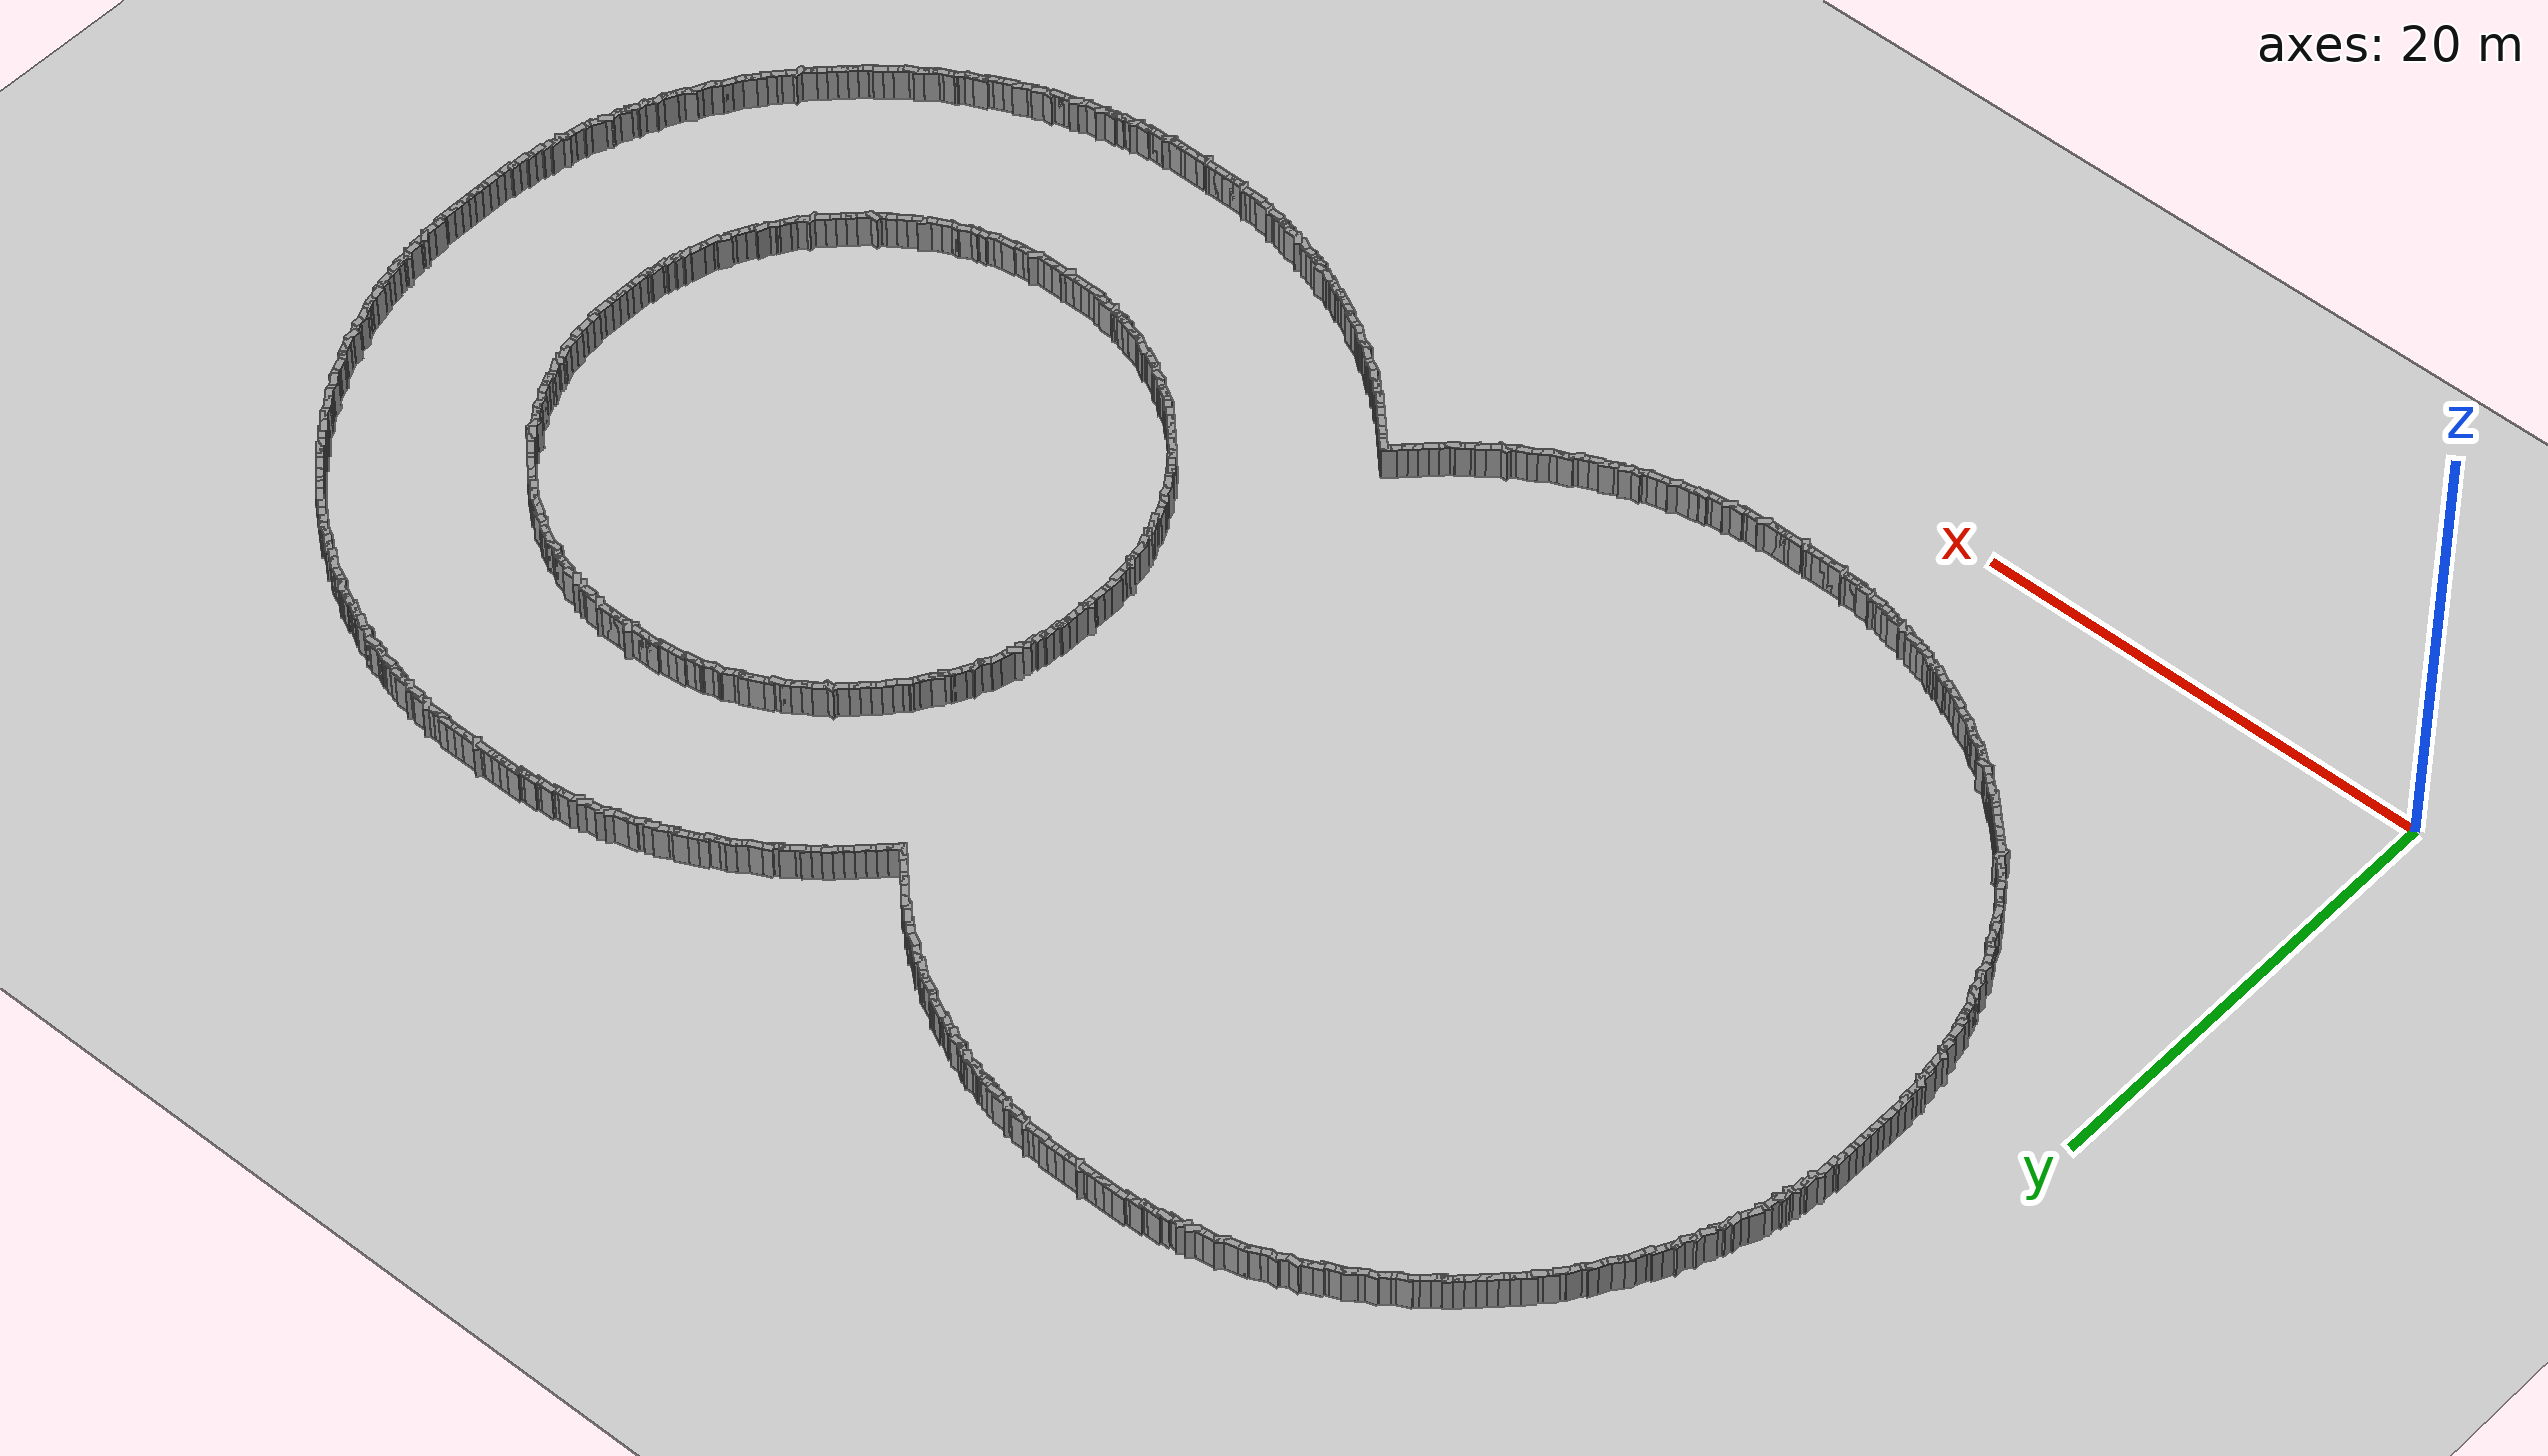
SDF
<?xml version="1.0" ?>
<sdf version="1.5">
  <world name="test_figure8">
    <include><uri>model://sun</uri></include>
    <include><uri>model://ground_plane</uri></include>
    <model name="curbL_0">
      <static>true</static>
      <pose>5.500 29.400 0.750 0 0 -1.571</pose>
      <link name="link">
        <collision name="collision">
          <geometry><box><size>0.600 0.300 1.500</size></box></geometry>
        </collision>
        <visual name="visual">
          <geometry><box><size>0.600 0.300 1.500</size></box></geometry>
          <material>
            <ambient>0.6 0.6 0.6 1</ambient>
            <diffuse>0.6 0.6 0.6 1</diffuse>
          </material>
        </visual>
      </link>
    </model>
    <model name="curbL_1">
      <static>true</static>
      <pose>5.500 29.000 0.750 0 0 -2.356</pose>
      <link name="link">
        <collision name="collision">
          <geometry><box><size>0.600 0.300 1.500</size></box></geometry>
        </collision>
        <visual name="visual">
          <geometry><box><size>0.600 0.300 1.500</size></box></geometry>
          <material>
            <ambient>0.6 0.6 0.6 1</ambient>
            <diffuse>0.6 0.6 0.6 1</diffuse>
          </material>
        </visual>
      </link>
    </model>
    <model name="curbL_2">
      <static>true</static>
      <pose>5.400 28.641 0.750 0 0 -1.571</pose>
      <link name="link">
        <collision name="collision">
          <geometry><box><size>0.600 0.300 1.500</size></box></geometry>
        </collision>
        <visual name="visual">
          <geometry><box><size>0.600 0.300 1.500</size></box></geometry>
          <material>
            <ambient>0.6 0.6 0.6 1</ambient>
            <diffuse>0.6 0.6 0.6 1</diffuse>
          </material>
        </visual>
      </link>
    </model>
    <model name="curbL_3">
      <static>true</static>
      <pose>5.300 28.283 0.750 0 0 -1.571</pose>
      <link name="link">
        <collision name="collision">
          <geometry><box><size>0.600 0.300 1.500</size></box></geometry>
        </collision>
        <visual name="visual">
          <geometry><box><size>0.600 0.300 1.500</size></box></geometry>
          <material>
            <ambient>0.6 0.6 0.6 1</ambient>
            <diffuse>0.6 0.6 0.6 1</diffuse>
          </material>
        </visual>
      </link>
    </model>
    <model name="curbL_4">
      <static>true</static>
      <pose>5.288 27.888 0.750 0 0 -2.356</pose>
      <link name="link">
        <collision name="collision">
          <geometry><box><size>0.600 0.300 1.500</size></box></geometry>
        </collision>
        <visual name="visual">
          <geometry><box><size>0.600 0.300 1.500</size></box></geometry>
          <material>
            <ambient>0.6 0.6 0.6 1</ambient>
            <diffuse>0.6 0.6 0.6 1</diffuse>
          </material>
        </visual>
      </link>
    </model>
    <model name="curbL_5">
      <static>true</static>
      <pose>5.200 27.524 0.750 0 0 -1.571</pose>
      <link name="link">
        <collision name="collision">
          <geometry><box><size>0.600 0.300 1.500</size></box></geometry>
        </collision>
        <visual name="visual">
          <geometry><box><size>0.600 0.300 1.500</size></box></geometry>
          <material>
            <ambient>0.6 0.6 0.6 1</ambient>
            <diffuse>0.6 0.6 0.6 1</diffuse>
          </material>
        </visual>
      </link>
    </model>
    <model name="curbL_6">
      <static>true</static>
      <pose>5.200 27.124 0.750 0 0 -1.571</pose>
      <link name="link">
        <collision name="collision">
          <geometry><box><size>0.600 0.300 1.500</size></box></geometry>
        </collision>
        <visual name="visual">
          <geometry><box><size>0.600 0.300 1.500</size></box></geometry>
          <material>
            <ambient>0.6 0.6 0.6 1</ambient>
            <diffuse>0.6 0.6 0.6 1</diffuse>
          </material>
        </visual>
      </link>
    </model>
    <model name="curbL_7">
      <static>true</static>
      <pose>5.100 26.766 0.750 0 0 -1.571</pose>
      <link name="link">
        <collision name="collision">
          <geometry><box><size>0.600 0.300 1.500</size></box></geometry>
        </collision>
        <visual name="visual">
          <geometry><box><size>0.600 0.300 1.500</size></box></geometry>
          <material>
            <ambient>0.6 0.6 0.6 1</ambient>
            <diffuse>0.6 0.6 0.6 1</diffuse>
          </material>
        </visual>
      </link>
    </model>
    <model name="curbL_8">
      <static>true</static>
      <pose>5.100 26.366 0.750 0 0 -1.571</pose>
      <link name="link">
        <collision name="collision">
          <geometry><box><size>0.600 0.300 1.500</size></box></geometry>
        </collision>
        <visual name="visual">
          <geometry><box><size>0.600 0.300 1.500</size></box></geometry>
          <material>
            <ambient>0.6 0.6 0.6 1</ambient>
            <diffuse>0.6 0.6 0.6 1</diffuse>
          </material>
        </visual>
      </link>
    </model>
    <model name="curbL_9">
      <static>true</static>
      <pose>5.100 25.966 0.750 0 0 -1.571</pose>
      <link name="link">
        <collision name="collision">
          <geometry><box><size>0.600 0.300 1.500</size></box></geometry>
        </collision>
        <visual name="visual">
          <geometry><box><size>0.600 0.300 1.500</size></box></geometry>
          <material>
            <ambient>0.6 0.6 0.6 1</ambient>
            <diffuse>0.6 0.6 0.6 1</diffuse>
          </material>
        </visual>
      </link>
    </model>
    <model name="curbL_10">
      <static>true</static>
      <pose>5.100 25.566 0.750 0 0 -1.571</pose>
      <link name="link">
        <collision name="collision">
          <geometry><box><size>0.600 0.300 1.500</size></box></geometry>
        </collision>
        <visual name="visual">
          <geometry><box><size>0.600 0.300 1.500</size></box></geometry>
          <material>
            <ambient>0.6 0.6 0.6 1</ambient>
            <diffuse>0.6 0.6 0.6 1</diffuse>
          </material>
        </visual>
      </link>
    </model>
    <model name="curbL_11">
      <static>true</static>
      <pose>5.100 25.166 0.750 0 0 -1.571</pose>
      <link name="link">
        <collision name="collision">
          <geometry><box><size>0.600 0.300 1.500</size></box></geometry>
        </collision>
        <visual name="visual">
          <geometry><box><size>0.600 0.300 1.500</size></box></geometry>
          <material>
            <ambient>0.6 0.6 0.6 1</ambient>
            <diffuse>0.6 0.6 0.6 1</diffuse>
          </material>
        </visual>
      </link>
    </model>
    <model name="curbL_12">
      <static>true</static>
      <pose>5.100 24.849 0.750 0 0 -1.571</pose>
      <link name="link">
        <collision name="collision">
          <geometry><box><size>0.600 0.300 1.500</size></box></geometry>
        </collision>
        <visual name="visual">
          <geometry><box><size>0.600 0.300 1.500</size></box></geometry>
          <material>
            <ambient>0.6 0.6 0.6 1</ambient>
            <diffuse>0.6 0.6 0.6 1</diffuse>
          </material>
        </visual>
      </link>
    </model>
    <model name="curbL_13">
      <static>true</static>
      <pose>5.100 24.449 0.750 0 0 -1.571</pose>
      <link name="link">
        <collision name="collision">
          <geometry><box><size>0.600 0.300 1.500</size></box></geometry>
        </collision>
        <visual name="visual">
          <geometry><box><size>0.600 0.300 1.500</size></box></geometry>
          <material>
            <ambient>0.6 0.6 0.6 1</ambient>
            <diffuse>0.6 0.6 0.6 1</diffuse>
          </material>
        </visual>
      </link>
    </model>
    <model name="curbL_14">
      <static>true</static>
      <pose>5.100 24.049 0.750 0 0 -1.571</pose>
      <link name="link">
        <collision name="collision">
          <geometry><box><size>0.600 0.300 1.500</size></box></geometry>
        </collision>
        <visual name="visual">
          <geometry><box><size>0.600 0.300 1.500</size></box></geometry>
          <material>
            <ambient>0.6 0.6 0.6 1</ambient>
            <diffuse>0.6 0.6 0.6 1</diffuse>
          </material>
        </visual>
      </link>
    </model>
    <model name="curbL_15">
      <static>true</static>
      <pose>5.100 23.649 0.750 0 0 -1.571</pose>
      <link name="link">
        <collision name="collision">
          <geometry><box><size>0.600 0.300 1.500</size></box></geometry>
        </collision>
        <visual name="visual">
          <geometry><box><size>0.600 0.300 1.500</size></box></geometry>
          <material>
            <ambient>0.6 0.6 0.6 1</ambient>
            <diffuse>0.6 0.6 0.6 1</diffuse>
          </material>
        </visual>
      </link>
    </model>
    <model name="curbL_16">
      <static>true</static>
      <pose>5.100 23.249 0.750 0 0 -1.571</pose>
      <link name="link">
        <collision name="collision">
          <geometry><box><size>0.600 0.300 1.500</size></box></geometry>
        </collision>
        <visual name="visual">
          <geometry><box><size>0.600 0.300 1.500</size></box></geometry>
          <material>
            <ambient>0.6 0.6 0.6 1</ambient>
            <diffuse>0.6 0.6 0.6 1</diffuse>
          </material>
        </visual>
      </link>
    </model>
    <model name="curbL_17">
      <static>true</static>
      <pose>5.200 22.890 0.750 0 0 -1.571</pose>
      <link name="link">
        <collision name="collision">
          <geometry><box><size>0.600 0.300 1.500</size></box></geometry>
        </collision>
        <visual name="visual">
          <geometry><box><size>0.600 0.300 1.500</size></box></geometry>
          <material>
            <ambient>0.6 0.6 0.6 1</ambient>
            <diffuse>0.6 0.6 0.6 1</diffuse>
          </material>
        </visual>
      </link>
    </model>
    <model name="curbL_18">
      <static>true</static>
      <pose>5.200 22.490 0.750 0 0 -1.571</pose>
      <link name="link">
        <collision name="collision">
          <geometry><box><size>0.600 0.300 1.500</size></box></geometry>
        </collision>
        <visual name="visual">
          <geometry><box><size>0.600 0.300 1.500</size></box></geometry>
          <material>
            <ambient>0.6 0.6 0.6 1</ambient>
            <diffuse>0.6 0.6 0.6 1</diffuse>
          </material>
        </visual>
      </link>
    </model>
    <model name="curbL_19">
      <static>true</static>
      <pose>5.278 22.122 0.750 0 0 -0.785</pose>
      <link name="link">
        <collision name="collision">
          <geometry><box><size>0.600 0.300 1.500</size></box></geometry>
        </collision>
        <visual name="visual">
          <geometry><box><size>0.600 0.300 1.500</size></box></geometry>
          <material>
            <ambient>0.6 0.6 0.6 1</ambient>
            <diffuse>0.6 0.6 0.6 1</diffuse>
          </material>
        </visual>
      </link>
    </model>
    <model name="curbL_20">
      <static>true</static>
      <pose>5.300 21.731 0.750 0 0 -1.571</pose>
      <link name="link">
        <collision name="collision">
          <geometry><box><size>0.600 0.300 1.500</size></box></geometry>
        </collision>
        <visual name="visual">
          <geometry><box><size>0.600 0.300 1.500</size></box></geometry>
          <material>
            <ambient>0.6 0.6 0.6 1</ambient>
            <diffuse>0.6 0.6 0.6 1</diffuse>
          </material>
        </visual>
      </link>
    </model>
    <model name="curbL_21">
      <static>true</static>
      <pose>5.414 21.374 0.750 0 0 -1.460</pose>
      <link name="link">
        <collision name="collision">
          <geometry><box><size>0.600 0.300 1.500</size></box></geometry>
        </collision>
        <visual name="visual">
          <geometry><box><size>0.600 0.300 1.500</size></box></geometry>
          <material>
            <ambient>0.6 0.6 0.6 1</ambient>
            <diffuse>0.6 0.6 0.6 1</diffuse>
          </material>
        </visual>
      </link>
    </model>
    <model name="curbL_22">
      <static>true</static>
      <pose>5.458 20.976 0.750 0 0 -1.460</pose>
      <link name="link">
        <collision name="collision">
          <geometry><box><size>0.600 0.300 1.500</size></box></geometry>
        </collision>
        <visual name="visual">
          <geometry><box><size>0.600 0.300 1.500</size></box></geometry>
          <material>
            <ambient>0.6 0.6 0.6 1</ambient>
            <diffuse>0.6 0.6 0.6 1</diffuse>
          </material>
        </visual>
      </link>
    </model>
    <model name="curbL_23">
      <static>true</static>
      <pose>5.515 20.585 0.750 0 0 -0.785</pose>
      <link name="link">
        <collision name="collision">
          <geometry><box><size>0.600 0.300 1.500</size></box></geometry>
        </collision>
        <visual name="visual">
          <geometry><box><size>0.600 0.300 1.500</size></box></geometry>
          <material>
            <ambient>0.6 0.6 0.6 1</ambient>
            <diffuse>0.6 0.6 0.6 1</diffuse>
          </material>
        </visual>
      </link>
    </model>
    <model name="curbL_24">
      <static>true</static>
      <pose>5.600 20.220 0.750 0 0 -1.571</pose>
      <link name="link">
        <collision name="collision">
          <geometry><box><size>0.600 0.300 1.500</size></box></geometry>
        </collision>
        <visual name="visual">
          <geometry><box><size>0.600 0.300 1.500</size></box></geometry>
          <material>
            <ambient>0.6 0.6 0.6 1</ambient>
            <diffuse>0.6 0.6 0.6 1</diffuse>
          </material>
        </visual>
      </link>
    </model>
    <model name="curbL_25">
      <static>true</static>
      <pose>5.734 19.864 0.750 0 0 -1.429</pose>
      <link name="link">
        <collision name="collision">
          <geometry><box><size>0.600 0.300 1.500</size></box></geometry>
        </collision>
        <visual name="visual">
          <geometry><box><size>0.600 0.300 1.500</size></box></geometry>
          <material>
            <ambient>0.6 0.6 0.6 1</ambient>
            <diffuse>0.6 0.6 0.6 1</diffuse>
          </material>
        </visual>
      </link>
    </model>
    <model name="curbL_26">
      <static>true</static>
      <pose>5.790 19.468 0.750 0 0 -1.429</pose>
      <link name="link">
        <collision name="collision">
          <geometry><box><size>0.600 0.300 1.500</size></box></geometry>
        </collision>
        <visual name="visual">
          <geometry><box><size>0.600 0.300 1.500</size></box></geometry>
          <material>
            <ambient>0.6 0.6 0.6 1</ambient>
            <diffuse>0.6 0.6 0.6 1</diffuse>
          </material>
        </visual>
      </link>
    </model>
    <model name="curbL_27">
      <static>true</static>
      <pose>5.900 19.110 0.750 0 0 -1.571</pose>
      <link name="link">
        <collision name="collision">
          <geometry><box><size>0.600 0.300 1.500</size></box></geometry>
        </collision>
        <visual name="visual">
          <geometry><box><size>0.600 0.300 1.500</size></box></geometry>
          <material>
            <ambient>0.6 0.6 0.6 1</ambient>
            <diffuse>0.6 0.6 0.6 1</diffuse>
          </material>
        </visual>
      </link>
    </model>
    <model name="curbL_28">
      <static>true</static>
      <pose>6.060 18.759 0.750 0 0 -1.326</pose>
      <link name="link">
        <collision name="collision">
          <geometry><box><size>0.600 0.300 1.500</size></box></geometry>
        </collision>
        <visual name="visual">
          <geometry><box><size>0.600 0.300 1.500</size></box></geometry>
          <material>
            <ambient>0.6 0.6 0.6 1</ambient>
            <diffuse>0.6 0.6 0.6 1</diffuse>
          </material>
        </visual>
      </link>
    </model>
    <model name="curbL_29">
      <static>true</static>
      <pose>6.157 18.370 0.750 0 0 -1.326</pose>
      <link name="link">
        <collision name="collision">
          <geometry><box><size>0.600 0.300 1.500</size></box></geometry>
        </collision>
        <visual name="visual">
          <geometry><box><size>0.600 0.300 1.500</size></box></geometry>
          <material>
            <ambient>0.6 0.6 0.6 1</ambient>
            <diffuse>0.6 0.6 0.6 1</diffuse>
          </material>
        </visual>
      </link>
    </model>
    <model name="curbL_30">
      <static>true</static>
      <pose>6.324 18.013 0.750 0 0 -0.983</pose>
      <link name="link">
        <collision name="collision">
          <geometry><box><size>0.600 0.300 1.500</size></box></geometry>
        </collision>
        <visual name="visual">
          <geometry><box><size>0.600 0.300 1.500</size></box></geometry>
          <material>
            <ambient>0.6 0.6 0.6 1</ambient>
            <diffuse>0.6 0.6 0.6 1</diffuse>
          </material>
        </visual>
      </link>
    </model>
    <model name="curbL_31">
      <static>true</static>
      <pose>6.435 17.647 0.750 0 0 -0.983</pose>
      <link name="link">
        <collision name="collision">
          <geometry><box><size>0.600 0.300 1.500</size></box></geometry>
        </collision>
        <visual name="visual">
          <geometry><box><size>0.600 0.300 1.500</size></box></geometry>
          <material>
            <ambient>0.6 0.6 0.6 1</ambient>
            <diffuse>0.6 0.6 0.6 1</diffuse>
          </material>
        </visual>
      </link>
    </model>
    <model name="curbL_32">
      <static>true</static>
      <pose>6.600 17.297 0.750 0 0 -1.571</pose>
      <link name="link">
        <collision name="collision">
          <geometry><box><size>0.600 0.300 1.500</size></box></geometry>
        </collision>
        <visual name="visual">
          <geometry><box><size>0.600 0.300 1.500</size></box></geometry>
          <material>
            <ambient>0.6 0.6 0.6 1</ambient>
            <diffuse>0.6 0.6 0.6 1</diffuse>
          </material>
        </visual>
      </link>
    </model>
    <model name="curbL_33">
      <static>true</static>
      <pose>6.756 16.940 0.750 0 0 -1.030</pose>
      <link name="link">
        <collision name="collision">
          <geometry><box><size>0.600 0.300 1.500</size></box></geometry>
        </collision>
        <visual name="visual">
          <geometry><box><size>0.600 0.300 1.500</size></box></geometry>
          <material>
            <ambient>0.6 0.6 0.6 1</ambient>
            <diffuse>0.6 0.6 0.6 1</diffuse>
          </material>
        </visual>
      </link>
    </model>
    <model name="curbL_34">
      <static>true</static>
      <pose>6.900 16.580 0.750 0 0 -1.571</pose>
      <link name="link">
        <collision name="collision">
          <geometry><box><size>0.600 0.300 1.500</size></box></geometry>
        </collision>
        <visual name="visual">
          <geometry><box><size>0.600 0.300 1.500</size></box></geometry>
          <material>
            <ambient>0.6 0.6 0.6 1</ambient>
            <diffuse>0.6 0.6 0.6 1</diffuse>
          </material>
        </visual>
      </link>
    </model>
    <model name="curbL_35">
      <static>true</static>
      <pose>7.043 16.214 0.750 0 0 -1.107</pose>
      <link name="link">
        <collision name="collision">
          <geometry><box><size>0.600 0.300 1.500</size></box></geometry>
        </collision>
        <visual name="visual">
          <geometry><box><size>0.600 0.300 1.500</size></box></geometry>
          <material>
            <ambient>0.6 0.6 0.6 1</ambient>
            <diffuse>0.6 0.6 0.6 1</diffuse>
          </material>
        </visual>
      </link>
    </model>
    <model name="curbL_36">
      <static>true</static>
      <pose>7.222 15.856 0.750 0 0 -1.107</pose>
      <link name="link">
        <collision name="collision">
          <geometry><box><size>0.600 0.300 1.500</size></box></geometry>
        </collision>
        <visual name="visual">
          <geometry><box><size>0.600 0.300 1.500</size></box></geometry>
          <material>
            <ambient>0.6 0.6 0.6 1</ambient>
            <diffuse>0.6 0.6 0.6 1</diffuse>
          </material>
        </visual>
      </link>
    </model>
    <model name="curbL_37">
      <static>true</static>
      <pose>7.460 15.540 0.750 0 0 -0.785</pose>
      <link name="link">
        <collision name="collision">
          <geometry><box><size>0.600 0.300 1.500</size></box></geometry>
        </collision>
        <visual name="visual">
          <geometry><box><size>0.600 0.300 1.500</size></box></geometry>
          <material>
            <ambient>0.6 0.6 0.6 1</ambient>
            <diffuse>0.6 0.6 0.6 1</diffuse>
          </material>
        </visual>
      </link>
    </model>
    <model name="curbL_38">
      <static>true</static>
      <pose>7.635 15.185 0.750 0 0 -1.166</pose>
      <link name="link">
        <collision name="collision">
          <geometry><box><size>0.600 0.300 1.500</size></box></geometry>
        </collision>
        <visual name="visual">
          <geometry><box><size>0.600 0.300 1.500</size></box></geometry>
          <material>
            <ambient>0.6 0.6 0.6 1</ambient>
            <diffuse>0.6 0.6 0.6 1</diffuse>
          </material>
        </visual>
      </link>
    </model>
    <model name="curbL_39">
      <static>true</static>
      <pose>7.793 14.817 0.750 0 0 -1.166</pose>
      <link name="link">
        <collision name="collision">
          <geometry><box><size>0.600 0.300 1.500</size></box></geometry>
        </collision>
        <visual name="visual">
          <geometry><box><size>0.600 0.300 1.500</size></box></geometry>
          <material>
            <ambient>0.6 0.6 0.6 1</ambient>
            <diffuse>0.6 0.6 0.6 1</diffuse>
          </material>
        </visual>
      </link>
    </model>
    <model name="curbL_40">
      <static>true</static>
      <pose>8.044 14.512 0.750 0 0 -1.107</pose>
      <link name="link">
        <collision name="collision">
          <geometry><box><size>0.600 0.300 1.500</size></box></geometry>
        </collision>
        <visual name="visual">
          <geometry><box><size>0.600 0.300 1.500</size></box></geometry>
          <material>
            <ambient>0.6 0.6 0.6 1</ambient>
            <diffuse>0.6 0.6 0.6 1</diffuse>
          </material>
        </visual>
      </link>
    </model>
    <model name="curbL_41">
      <static>true</static>
      <pose>8.223 14.154 0.750 0 0 -1.107</pose>
      <link name="link">
        <collision name="collision">
          <geometry><box><size>0.600 0.300 1.500</size></box></geometry>
        </collision>
        <visual name="visual">
          <geometry><box><size>0.600 0.300 1.500</size></box></geometry>
          <material>
            <ambient>0.6 0.6 0.6 1</ambient>
            <diffuse>0.6 0.6 0.6 1</diffuse>
          </material>
        </visual>
      </link>
    </model>
    <model name="curbL_42">
      <static>true</static>
      <pose>8.446 13.825 0.750 0 0 -0.876</pose>
      <link name="link">
        <collision name="collision">
          <geometry><box><size>0.600 0.300 1.500</size></box></geometry>
        </collision>
        <visual name="visual">
          <geometry><box><size>0.600 0.300 1.500</size></box></geometry>
          <material>
            <ambient>0.6 0.6 0.6 1</ambient>
            <diffuse>0.6 0.6 0.6 1</diffuse>
          </material>
        </visual>
      </link>
    </model>
    <model name="curbL_43">
      <static>true</static>
      <pose>8.702 13.518 0.750 0 0 -0.876</pose>
      <link name="link">
        <collision name="collision">
          <geometry><box><size>0.600 0.300 1.500</size></box></geometry>
        </collision>
        <visual name="visual">
          <geometry><box><size>0.600 0.300 1.500</size></box></geometry>
          <material>
            <ambient>0.6 0.6 0.6 1</ambient>
            <diffuse>0.6 0.6 0.6 1</diffuse>
          </material>
        </visual>
      </link>
    </model>
    <model name="curbL_44">
      <static>true</static>
      <pose>8.910 13.180 0.750 0 0 -1.107</pose>
      <link name="link">
        <collision name="collision">
          <geometry><box><size>0.600 0.300 1.500</size></box></geometry>
        </collision>
        <visual name="visual">
          <geometry><box><size>0.600 0.300 1.500</size></box></geometry>
          <material>
            <ambient>0.6 0.6 0.6 1</ambient>
            <diffuse>0.6 0.6 0.6 1</diffuse>
          </material>
        </visual>
      </link>
    </model>
    <model name="curbL_45">
      <static>true</static>
      <pose>9.133 12.852 0.750 0 0 -0.838</pose>
      <link name="link">
        <collision name="collision">
          <geometry><box><size>0.600 0.300 1.500</size></box></geometry>
        </collision>
        <visual name="visual">
          <geometry><box><size>0.600 0.300 1.500</size></box></geometry>
          <material>
            <ambient>0.6 0.6 0.6 1</ambient>
            <diffuse>0.6 0.6 0.6 1</diffuse>
          </material>
        </visual>
      </link>
    </model>
    <model name="curbL_46">
      <static>true</static>
      <pose>9.401 12.555 0.750 0 0 -0.838</pose>
      <link name="link">
        <collision name="collision">
          <geometry><box><size>0.600 0.300 1.500</size></box></geometry>
        </collision>
        <visual name="visual">
          <geometry><box><size>0.600 0.300 1.500</size></box></geometry>
          <material>
            <ambient>0.6 0.6 0.6 1</ambient>
            <diffuse>0.6 0.6 0.6 1</diffuse>
          </material>
        </visual>
      </link>
    </model>
    <model name="curbL_47">
      <static>true</static>
      <pose>9.668 12.257 0.750 0 0 -0.838</pose>
      <link name="link">
        <collision name="collision">
          <geometry><box><size>0.600 0.300 1.500</size></box></geometry>
        </collision>
        <visual name="visual">
          <geometry><box><size>0.600 0.300 1.500</size></box></geometry>
          <material>
            <ambient>0.6 0.6 0.6 1</ambient>
            <diffuse>0.6 0.6 0.6 1</diffuse>
          </material>
        </visual>
      </link>
    </model>
    <model name="curbL_48">
      <static>true</static>
      <pose>9.900 11.946 0.750 0 0 -1.571</pose>
      <link name="link">
        <collision name="collision">
          <geometry><box><size>0.600 0.300 1.500</size></box></geometry>
        </collision>
        <visual name="visual">
          <geometry><box><size>0.600 0.300 1.500</size></box></geometry>
          <material>
            <ambient>0.6 0.6 0.6 1</ambient>
            <diffuse>0.6 0.6 0.6 1</diffuse>
          </material>
        </visual>
      </link>
    </model>
    <model name="curbL_49">
      <static>true</static>
      <pose>10.150 11.650 0.750 0 0 -0.785</pose>
      <link name="link">
        <collision name="collision">
          <geometry><box><size>0.600 0.300 1.500</size></box></geometry>
        </collision>
        <visual name="visual">
          <geometry><box><size>0.600 0.300 1.500</size></box></geometry>
          <material>
            <ambient>0.6 0.6 0.6 1</ambient>
            <diffuse>0.6 0.6 0.6 1</diffuse>
          </material>
        </visual>
      </link>
    </model>
    <model name="curbL_50">
      <static>true</static>
      <pose>10.433 11.367 0.750 0 0 -0.785</pose>
      <link name="link">
        <collision name="collision">
          <geometry><box><size>0.600 0.300 1.500</size></box></geometry>
        </collision>
        <visual name="visual">
          <geometry><box><size>0.600 0.300 1.500</size></box></geometry>
          <material>
            <ambient>0.6 0.6 0.6 1</ambient>
            <diffuse>0.6 0.6 0.6 1</diffuse>
          </material>
        </visual>
      </link>
    </model>
    <model name="curbL_51">
      <static>true</static>
      <pose>10.716 11.084 0.750 0 0 -0.785</pose>
      <link name="link">
        <collision name="collision">
          <geometry><box><size>0.600 0.300 1.500</size></box></geometry>
        </collision>
        <visual name="visual">
          <geometry><box><size>0.600 0.300 1.500</size></box></geometry>
          <material>
            <ambient>0.6 0.6 0.6 1</ambient>
            <diffuse>0.6 0.6 0.6 1</diffuse>
          </material>
        </visual>
      </link>
    </model>
    <model name="curbL_52">
      <static>true</static>
      <pose>10.999 10.801 0.750 0 0 -0.785</pose>
      <link name="link">
        <collision name="collision">
          <geometry><box><size>0.600 0.300 1.500</size></box></geometry>
        </collision>
        <visual name="visual">
          <geometry><box><size>0.600 0.300 1.500</size></box></geometry>
          <material>
            <ambient>0.6 0.6 0.6 1</ambient>
            <diffuse>0.6 0.6 0.6 1</diffuse>
          </material>
        </visual>
      </link>
    </model>
    <model name="curbL_53">
      <static>true</static>
      <pose>11.282 10.518 0.750 0 0 -0.785</pose>
      <link name="link">
        <collision name="collision">
          <geometry><box><size>0.600 0.300 1.500</size></box></geometry>
        </collision>
        <visual name="visual">
          <geometry><box><size>0.600 0.300 1.500</size></box></geometry>
          <material>
            <ambient>0.6 0.6 0.6 1</ambient>
            <diffuse>0.6 0.6 0.6 1</diffuse>
          </material>
        </visual>
      </link>
    </model>
    <model name="curbL_54">
      <static>true</static>
      <pose>11.564 10.236 0.750 0 0 -0.785</pose>
      <link name="link">
        <collision name="collision">
          <geometry><box><size>0.600 0.300 1.500</size></box></geometry>
        </collision>
        <visual name="visual">
          <geometry><box><size>0.600 0.300 1.500</size></box></geometry>
          <material>
            <ambient>0.6 0.6 0.6 1</ambient>
            <diffuse>0.6 0.6 0.6 1</diffuse>
          </material>
        </visual>
      </link>
    </model>
    <model name="curbL_55">
      <static>true</static>
      <pose>11.847 9.953 0.750 0 0 -0.785</pose>
      <link name="link">
        <collision name="collision">
          <geometry><box><size>0.600 0.300 1.500</size></box></geometry>
        </collision>
        <visual name="visual">
          <geometry><box><size>0.600 0.300 1.500</size></box></geometry>
          <material>
            <ambient>0.6 0.6 0.6 1</ambient>
            <diffuse>0.6 0.6 0.6 1</diffuse>
          </material>
        </visual>
      </link>
    </model>
    <model name="curbL_56">
      <static>true</static>
      <pose>12.168 9.749 0.750 0 0 -0.733</pose>
      <link name="link">
        <collision name="collision">
          <geometry><box><size>0.600 0.300 1.500</size></box></geometry>
        </collision>
        <visual name="visual">
          <geometry><box><size>0.600 0.300 1.500</size></box></geometry>
          <material>
            <ambient>0.6 0.6 0.6 1</ambient>
            <diffuse>0.6 0.6 0.6 1</diffuse>
          </material>
        </visual>
      </link>
    </model>
    <model name="curbL_57">
      <static>true</static>
      <pose>12.465 9.482 0.750 0 0 -0.733</pose>
      <link name="link">
        <collision name="collision">
          <geometry><box><size>0.600 0.300 1.500</size></box></geometry>
        </collision>
        <visual name="visual">
          <geometry><box><size>0.600 0.300 1.500</size></box></geometry>
          <material>
            <ambient>0.6 0.6 0.6 1</ambient>
            <diffuse>0.6 0.6 0.6 1</diffuse>
          </material>
        </visual>
      </link>
    </model>
    <model name="curbL_58">
      <static>true</static>
      <pose>12.762 9.214 0.750 0 0 -0.733</pose>
      <link name="link">
        <collision name="collision">
          <geometry><box><size>0.600 0.300 1.500</size></box></geometry>
        </collision>
        <visual name="visual">
          <geometry><box><size>0.600 0.300 1.500</size></box></geometry>
          <material>
            <ambient>0.6 0.6 0.6 1</ambient>
            <diffuse>0.6 0.6 0.6 1</diffuse>
          </material>
        </visual>
      </link>
    </model>
    <model name="curbL_59">
      <static>true</static>
      <pose>13.080 9.000 0.750 0 0 0.000</pose>
      <link name="link">
        <collision name="collision">
          <geometry><box><size>0.600 0.300 1.500</size></box></geometry>
        </collision>
        <visual name="visual">
          <geometry><box><size>0.600 0.300 1.500</size></box></geometry>
          <material>
            <ambient>0.6 0.6 0.6 1</ambient>
            <diffuse>0.6 0.6 0.6 1</diffuse>
          </material>
        </visual>
      </link>
    </model>
    <model name="curbL_60">
      <static>true</static>
      <pose>13.392 8.757 0.750 0 0 -0.695</pose>
      <link name="link">
        <collision name="collision">
          <geometry><box><size>0.600 0.300 1.500</size></box></geometry>
        </collision>
        <visual name="visual">
          <geometry><box><size>0.600 0.300 1.500</size></box></geometry>
          <material>
            <ambient>0.6 0.6 0.6 1</ambient>
            <diffuse>0.6 0.6 0.6 1</diffuse>
          </material>
        </visual>
      </link>
    </model>
    <model name="curbL_61">
      <static>true</static>
      <pose>13.699 8.501 0.750 0 0 -0.695</pose>
      <link name="link">
        <collision name="collision">
          <geometry><box><size>0.600 0.300 1.500</size></box></geometry>
        </collision>
        <visual name="visual">
          <geometry><box><size>0.600 0.300 1.500</size></box></geometry>
          <material>
            <ambient>0.6 0.6 0.6 1</ambient>
            <diffuse>0.6 0.6 0.6 1</diffuse>
          </material>
        </visual>
      </link>
    </model>
    <model name="curbL_62">
      <static>true</static>
      <pose>14.057 8.322 0.750 0 0 -0.464</pose>
      <link name="link">
        <collision name="collision">
          <geometry><box><size>0.600 0.300 1.500</size></box></geometry>
        </collision>
        <visual name="visual">
          <geometry><box><size>0.600 0.300 1.500</size></box></geometry>
          <material>
            <ambient>0.6 0.6 0.6 1</ambient>
            <diffuse>0.6 0.6 0.6 1</diffuse>
          </material>
        </visual>
      </link>
    </model>
    <model name="curbL_63">
      <static>true</static>
      <pose>14.400 8.120 0.750 0 0 -0.675</pose>
      <link name="link">
        <collision name="collision">
          <geometry><box><size>0.600 0.300 1.500</size></box></geometry>
        </collision>
        <visual name="visual">
          <geometry><box><size>0.600 0.300 1.500</size></box></geometry>
          <material>
            <ambient>0.6 0.6 0.6 1</ambient>
            <diffuse>0.6 0.6 0.6 1</diffuse>
          </material>
        </visual>
      </link>
    </model>
    <model name="curbL_64">
      <static>true</static>
      <pose>14.713 7.870 0.750 0 0 -0.675</pose>
      <link name="link">
        <collision name="collision">
          <geometry><box><size>0.600 0.300 1.500</size></box></geometry>
        </collision>
        <visual name="visual">
          <geometry><box><size>0.600 0.300 1.500</size></box></geometry>
          <material>
            <ambient>0.6 0.6 0.6 1</ambient>
            <diffuse>0.6 0.6 0.6 1</diffuse>
          </material>
        </visual>
      </link>
    </model>
    <model name="curbL_65">
      <static>true</static>
      <pose>15.065 7.687 0.750 0 0 -0.405</pose>
      <link name="link">
        <collision name="collision">
          <geometry><box><size>0.600 0.300 1.500</size></box></geometry>
        </collision>
        <visual name="visual">
          <geometry><box><size>0.600 0.300 1.500</size></box></geometry>
          <material>
            <ambient>0.6 0.6 0.6 1</ambient>
            <diffuse>0.6 0.6 0.6 1</diffuse>
          </material>
        </visual>
      </link>
    </model>
    <model name="curbL_66">
      <static>true</static>
      <pose>15.432 7.529 0.750 0 0 -0.405</pose>
      <link name="link">
        <collision name="collision">
          <geometry><box><size>0.600 0.300 1.500</size></box></geometry>
        </collision>
        <visual name="visual">
          <geometry><box><size>0.600 0.300 1.500</size></box></geometry>
          <material>
            <ambient>0.6 0.6 0.6 1</ambient>
            <diffuse>0.6 0.6 0.6 1</diffuse>
          </material>
        </visual>
      </link>
    </model>
    <model name="curbL_67">
      <static>true</static>
      <pose>15.739 7.281 0.750 0 0 -0.464</pose>
      <link name="link">
        <collision name="collision">
          <geometry><box><size>0.600 0.300 1.500</size></box></geometry>
        </collision>
        <visual name="visual">
          <geometry><box><size>0.600 0.300 1.500</size></box></geometry>
          <material>
            <ambient>0.6 0.6 0.6 1</ambient>
            <diffuse>0.6 0.6 0.6 1</diffuse>
          </material>
        </visual>
      </link>
    </model>
    <model name="curbL_68">
      <static>true</static>
      <pose>16.097 7.102 0.750 0 0 -0.464</pose>
      <link name="link">
        <collision name="collision">
          <geometry><box><size>0.600 0.300 1.500</size></box></geometry>
        </collision>
        <visual name="visual">
          <geometry><box><size>0.600 0.300 1.500</size></box></geometry>
          <material>
            <ambient>0.6 0.6 0.6 1</ambient>
            <diffuse>0.6 0.6 0.6 1</diffuse>
          </material>
        </visual>
      </link>
    </model>
    <model name="curbL_69">
      <static>true</static>
      <pose>16.455 6.923 0.750 0 0 -0.464</pose>
      <link name="link">
        <collision name="collision">
          <geometry><box><size>0.600 0.300 1.500</size></box></geometry>
        </collision>
        <visual name="visual">
          <geometry><box><size>0.600 0.300 1.500</size></box></geometry>
          <material>
            <ambient>0.6 0.6 0.6 1</ambient>
            <diffuse>0.6 0.6 0.6 1</diffuse>
          </material>
        </visual>
      </link>
    </model>
    <model name="curbL_70">
      <static>true</static>
      <pose>16.828 6.823 0.750 0 0 -0.540</pose>
      <link name="link">
        <collision name="collision">
          <geometry><box><size>0.600 0.300 1.500</size></box></geometry>
        </collision>
        <visual name="visual">
          <geometry><box><size>0.600 0.300 1.500</size></box></geometry>
          <material>
            <ambient>0.6 0.6 0.6 1</ambient>
            <diffuse>0.6 0.6 0.6 1</diffuse>
          </material>
        </visual>
      </link>
    </model>
    <model name="curbL_71">
      <static>true</static>
      <pose>17.171 6.617 0.750 0 0 -0.540</pose>
      <link name="link">
        <collision name="collision">
          <geometry><box><size>0.600 0.300 1.500</size></box></geometry>
        </collision>
        <visual name="visual">
          <geometry><box><size>0.600 0.300 1.500</size></box></geometry>
          <material>
            <ambient>0.6 0.6 0.6 1</ambient>
            <diffuse>0.6 0.6 0.6 1</diffuse>
          </material>
        </visual>
      </link>
    </model>
    <model name="curbL_72">
      <static>true</static>
      <pose>17.538 6.508 0.750 0 0 -0.588</pose>
      <link name="link">
        <collision name="collision">
          <geometry><box><size>0.600 0.300 1.500</size></box></geometry>
        </collision>
        <visual name="visual">
          <geometry><box><size>0.600 0.300 1.500</size></box></geometry>
          <material>
            <ambient>0.6 0.6 0.6 1</ambient>
            <diffuse>0.6 0.6 0.6 1</diffuse>
          </material>
        </visual>
      </link>
    </model>
    <model name="curbL_73">
      <static>true</static>
      <pose>17.905 6.397 0.750 0 0 -0.588</pose>
      <link name="link">
        <collision name="collision">
          <geometry><box><size>0.600 0.300 1.500</size></box></geometry>
        </collision>
        <visual name="visual">
          <geometry><box><size>0.600 0.300 1.500</size></box></geometry>
          <material>
            <ambient>0.6 0.6 0.6 1</ambient>
            <diffuse>0.6 0.6 0.6 1</diffuse>
          </material>
        </visual>
      </link>
    </model>
    <model name="curbL_74">
      <static>true</static>
      <pose>18.245 6.200 0.750 0 0 0.000</pose>
      <link name="link">
        <collision name="collision">
          <geometry><box><size>0.600 0.300 1.500</size></box></geometry>
        </collision>
        <visual name="visual">
          <geometry><box><size>0.600 0.300 1.500</size></box></geometry>
          <material>
            <ambient>0.6 0.6 0.6 1</ambient>
            <diffuse>0.6 0.6 0.6 1</diffuse>
          </material>
        </visual>
      </link>
    </model>
    <model name="curbL_75">
      <static>true</static>
      <pose>18.604 6.100 0.750 0 0 0.000</pose>
      <link name="link">
        <collision name="collision">
          <geometry><box><size>0.600 0.300 1.500</size></box></geometry>
        </collision>
        <visual name="visual">
          <geometry><box><size>0.600 0.300 1.500</size></box></geometry>
          <material>
            <ambient>0.6 0.6 0.6 1</ambient>
            <diffuse>0.6 0.6 0.6 1</diffuse>
          </material>
        </visual>
      </link>
    </model>
    <model name="curbL_76">
      <static>true</static>
      <pose>18.962 6.000 0.750 0 0 0.000</pose>
      <link name="link">
        <collision name="collision">
          <geometry><box><size>0.600 0.300 1.500</size></box></geometry>
        </collision>
        <visual name="visual">
          <geometry><box><size>0.600 0.300 1.500</size></box></geometry>
          <material>
            <ambient>0.6 0.6 0.6 1</ambient>
            <diffuse>0.6 0.6 0.6 1</diffuse>
          </material>
        </visual>
      </link>
    </model>
    <model name="curbL_77">
      <static>true</static>
      <pose>19.324 5.838 0.750 0 0 -0.464</pose>
      <link name="link">
        <collision name="collision">
          <geometry><box><size>0.600 0.300 1.500</size></box></geometry>
        </collision>
        <visual name="visual">
          <geometry><box><size>0.600 0.300 1.500</size></box></geometry>
          <material>
            <ambient>0.6 0.6 0.6 1</ambient>
            <diffuse>0.6 0.6 0.6 1</diffuse>
          </material>
        </visual>
      </link>
    </model>
    <model name="curbL_78">
      <static>true</static>
      <pose>19.711 5.789 0.750 0 0 -0.785</pose>
      <link name="link">
        <collision name="collision">
          <geometry><box><size>0.600 0.300 1.500</size></box></geometry>
        </collision>
        <visual name="visual">
          <geometry><box><size>0.600 0.300 1.500</size></box></geometry>
          <material>
            <ambient>0.6 0.6 0.6 1</ambient>
            <diffuse>0.6 0.6 0.6 1</diffuse>
          </material>
        </visual>
      </link>
    </model>
    <model name="curbL_79">
      <static>true</static>
      <pose>20.073 5.700 0.750 0 0 0.000</pose>
      <link name="link">
        <collision name="collision">
          <geometry><box><size>0.600 0.300 1.500</size></box></geometry>
        </collision>
        <visual name="visual">
          <geometry><box><size>0.600 0.300 1.500</size></box></geometry>
          <material>
            <ambient>0.6 0.6 0.6 1</ambient>
            <diffuse>0.6 0.6 0.6 1</diffuse>
          </material>
        </visual>
      </link>
    </model>
    <model name="curbL_80">
      <static>true</static>
      <pose>20.432 5.600 0.750 0 0 0.000</pose>
      <link name="link">
        <collision name="collision">
          <geometry><box><size>0.600 0.300 1.500</size></box></geometry>
        </collision>
        <visual name="visual">
          <geometry><box><size>0.600 0.300 1.500</size></box></geometry>
          <material>
            <ambient>0.6 0.6 0.6 1</ambient>
            <diffuse>0.6 0.6 0.6 1</diffuse>
          </material>
        </visual>
      </link>
    </model>
    <model name="curbL_81">
      <static>true</static>
      <pose>20.791 5.500 0.750 0 0 0.000</pose>
      <link name="link">
        <collision name="collision">
          <geometry><box><size>0.600 0.300 1.500</size></box></geometry>
        </collision>
        <visual name="visual">
          <geometry><box><size>0.600 0.300 1.500</size></box></geometry>
          <material>
            <ambient>0.6 0.6 0.6 1</ambient>
            <diffuse>0.6 0.6 0.6 1</diffuse>
          </material>
        </visual>
      </link>
    </model>
    <model name="curbL_82">
      <static>true</static>
      <pose>21.149 5.400 0.750 0 0 0.000</pose>
      <link name="link">
        <collision name="collision">
          <geometry><box><size>0.600 0.300 1.500</size></box></geometry>
        </collision>
        <visual name="visual">
          <geometry><box><size>0.600 0.300 1.500</size></box></geometry>
          <material>
            <ambient>0.6 0.6 0.6 1</ambient>
            <diffuse>0.6 0.6 0.6 1</diffuse>
          </material>
        </visual>
      </link>
    </model>
    <model name="curbL_83">
      <static>true</static>
      <pose>21.535 5.365 0.750 0 0 -0.785</pose>
      <link name="link">
        <collision name="collision">
          <geometry><box><size>0.600 0.300 1.500</size></box></geometry>
        </collision>
        <visual name="visual">
          <geometry><box><size>0.600 0.300 1.500</size></box></geometry>
          <material>
            <ambient>0.6 0.6 0.6 1</ambient>
            <diffuse>0.6 0.6 0.6 1</diffuse>
          </material>
        </visual>
      </link>
    </model>
    <model name="curbL_84">
      <static>true</static>
      <pose>21.908 5.300 0.750 0 0 0.000</pose>
      <link name="link">
        <collision name="collision">
          <geometry><box><size>0.600 0.300 1.500</size></box></geometry>
        </collision>
        <visual name="visual">
          <geometry><box><size>0.600 0.300 1.500</size></box></geometry>
          <material>
            <ambient>0.6 0.6 0.6 1</ambient>
            <diffuse>0.6 0.6 0.6 1</diffuse>
          </material>
        </visual>
      </link>
    </model>
    <model name="curbL_85">
      <static>true</static>
      <pose>22.266 5.200 0.750 0 0 0.000</pose>
      <link name="link">
        <collision name="collision">
          <geometry><box><size>0.600 0.300 1.500</size></box></geometry>
        </collision>
        <visual name="visual">
          <geometry><box><size>0.600 0.300 1.500</size></box></geometry>
          <material>
            <ambient>0.6 0.6 0.6 1</ambient>
            <diffuse>0.6 0.6 0.6 1</diffuse>
          </material>
        </visual>
      </link>
    </model>
    <model name="curbL_86">
      <static>true</static>
      <pose>22.666 5.200 0.750 0 0 0.000</pose>
      <link name="link">
        <collision name="collision">
          <geometry><box><size>0.600 0.300 1.500</size></box></geometry>
        </collision>
        <visual name="visual">
          <geometry><box><size>0.600 0.300 1.500</size></box></geometry>
          <material>
            <ambient>0.6 0.6 0.6 1</ambient>
            <diffuse>0.6 0.6 0.6 1</diffuse>
          </material>
        </visual>
      </link>
    </model>
    <model name="curbL_87">
      <static>true</static>
      <pose>23.047 5.153 0.750 0 0 -0.785</pose>
      <link name="link">
        <collision name="collision">
          <geometry><box><size>0.600 0.300 1.500</size></box></geometry>
        </collision>
        <visual name="visual">
          <geometry><box><size>0.600 0.300 1.500</size></box></geometry>
          <material>
            <ambient>0.6 0.6 0.6 1</ambient>
            <diffuse>0.6 0.6 0.6 1</diffuse>
          </material>
        </visual>
      </link>
    </model>
    <model name="curbL_88">
      <static>true</static>
      <pose>23.425 5.100 0.750 0 0 0.000</pose>
      <link name="link">
        <collision name="collision">
          <geometry><box><size>0.600 0.300 1.500</size></box></geometry>
        </collision>
        <visual name="visual">
          <geometry><box><size>0.600 0.300 1.500</size></box></geometry>
          <material>
            <ambient>0.6 0.6 0.6 1</ambient>
            <diffuse>0.6 0.6 0.6 1</diffuse>
          </material>
        </visual>
      </link>
    </model>
    <model name="curbL_89">
      <static>true</static>
      <pose>23.825 5.100 0.750 0 0 0.000</pose>
      <link name="link">
        <collision name="collision">
          <geometry><box><size>0.600 0.300 1.500</size></box></geometry>
        </collision>
        <visual name="visual">
          <geometry><box><size>0.600 0.300 1.500</size></box></geometry>
          <material>
            <ambient>0.6 0.6 0.6 1</ambient>
            <diffuse>0.6 0.6 0.6 1</diffuse>
          </material>
        </visual>
      </link>
    </model>
    <model name="curbL_90">
      <static>true</static>
      <pose>24.225 5.100 0.750 0 0 0.000</pose>
      <link name="link">
        <collision name="collision">
          <geometry><box><size>0.600 0.300 1.500</size></box></geometry>
        </collision>
        <visual name="visual">
          <geometry><box><size>0.600 0.300 1.500</size></box></geometry>
          <material>
            <ambient>0.6 0.6 0.6 1</ambient>
            <diffuse>0.6 0.6 0.6 1</diffuse>
          </material>
        </visual>
      </link>
    </model>
    <model name="curbL_91">
      <static>true</static>
      <pose>24.625 5.100 0.750 0 0 0.000</pose>
      <link name="link">
        <collision name="collision">
          <geometry><box><size>0.600 0.300 1.500</size></box></geometry>
        </collision>
        <visual name="visual">
          <geometry><box><size>0.600 0.300 1.500</size></box></geometry>
          <material>
            <ambient>0.6 0.6 0.6 1</ambient>
            <diffuse>0.6 0.6 0.6 1</diffuse>
          </material>
        </visual>
      </link>
    </model>
    <model name="curbL_92">
      <static>true</static>
      <pose>24.988 5.012 0.750 0 0 -0.785</pose>
      <link name="link">
        <collision name="collision">
          <geometry><box><size>0.600 0.300 1.500</size></box></geometry>
        </collision>
        <visual name="visual">
          <geometry><box><size>0.600 0.300 1.500</size></box></geometry>
          <material>
            <ambient>0.6 0.6 0.6 1</ambient>
            <diffuse>0.6 0.6 0.6 1</diffuse>
          </material>
        </visual>
      </link>
    </model>
    <model name="curbL_93">
      <static>true</static>
      <pose>25.342 5.100 0.750 0 0 0.000</pose>
      <link name="link">
        <collision name="collision">
          <geometry><box><size>0.600 0.300 1.500</size></box></geometry>
        </collision>
        <visual name="visual">
          <geometry><box><size>0.600 0.300 1.500</size></box></geometry>
          <material>
            <ambient>0.6 0.6 0.6 1</ambient>
            <diffuse>0.6 0.6 0.6 1</diffuse>
          </material>
        </visual>
      </link>
    </model>
    <model name="curbL_94">
      <static>true</static>
      <pose>25.742 5.100 0.750 0 0 0.000</pose>
      <link name="link">
        <collision name="collision">
          <geometry><box><size>0.600 0.300 1.500</size></box></geometry>
        </collision>
        <visual name="visual">
          <geometry><box><size>0.600 0.300 1.500</size></box></geometry>
          <material>
            <ambient>0.6 0.6 0.6 1</ambient>
            <diffuse>0.6 0.6 0.6 1</diffuse>
          </material>
        </visual>
      </link>
    </model>
    <model name="curbL_95">
      <static>true</static>
      <pose>26.142 5.100 0.750 0 0 0.000</pose>
      <link name="link">
        <collision name="collision">
          <geometry><box><size>0.600 0.300 1.500</size></box></geometry>
        </collision>
        <visual name="visual">
          <geometry><box><size>0.600 0.300 1.500</size></box></geometry>
          <material>
            <ambient>0.6 0.6 0.6 1</ambient>
            <diffuse>0.6 0.6 0.6 1</diffuse>
          </material>
        </visual>
      </link>
    </model>
    <model name="curbL_96">
      <static>true</static>
      <pose>26.542 5.100 0.750 0 0 0.000</pose>
      <link name="link">
        <collision name="collision">
          <geometry><box><size>0.600 0.300 1.500</size></box></geometry>
        </collision>
        <visual name="visual">
          <geometry><box><size>0.600 0.300 1.500</size></box></geometry>
          <material>
            <ambient>0.6 0.6 0.6 1</ambient>
            <diffuse>0.6 0.6 0.6 1</diffuse>
          </material>
        </visual>
      </link>
    </model>
    <model name="curbL_97">
      <static>true</static>
      <pose>26.930 5.130 0.750 0 0 0.785</pose>
      <link name="link">
        <collision name="collision">
          <geometry><box><size>0.600 0.300 1.500</size></box></geometry>
        </collision>
        <visual name="visual">
          <geometry><box><size>0.600 0.300 1.500</size></box></geometry>
          <material>
            <ambient>0.6 0.6 0.6 1</ambient>
            <diffuse>0.6 0.6 0.6 1</diffuse>
          </material>
        </visual>
      </link>
    </model>
    <model name="curbL_98">
      <static>true</static>
      <pose>27.301 5.200 0.750 0 0 0.000</pose>
      <link name="link">
        <collision name="collision">
          <geometry><box><size>0.600 0.300 1.500</size></box></geometry>
        </collision>
        <visual name="visual">
          <geometry><box><size>0.600 0.300 1.500</size></box></geometry>
          <material>
            <ambient>0.6 0.6 0.6 1</ambient>
            <diffuse>0.6 0.6 0.6 1</diffuse>
          </material>
        </visual>
      </link>
    </model>
    <model name="curbL_99">
      <static>true</static>
      <pose>27.701 5.200 0.750 0 0 0.000</pose>
      <link name="link">
        <collision name="collision">
          <geometry><box><size>0.600 0.300 1.500</size></box></geometry>
        </collision>
        <visual name="visual">
          <geometry><box><size>0.600 0.300 1.500</size></box></geometry>
          <material>
            <ambient>0.6 0.6 0.6 1</ambient>
            <diffuse>0.6 0.6 0.6 1</diffuse>
          </material>
        </visual>
      </link>
    </model>
    <model name="curbL_100">
      <static>true</static>
      <pose>28.059 5.300 0.750 0 0 0.000</pose>
      <link name="link">
        <collision name="collision">
          <geometry><box><size>0.600 0.300 1.500</size></box></geometry>
        </collision>
        <visual name="visual">
          <geometry><box><size>0.600 0.300 1.500</size></box></geometry>
          <material>
            <ambient>0.6 0.6 0.6 1</ambient>
            <diffuse>0.6 0.6 0.6 1</diffuse>
          </material>
        </visual>
      </link>
    </model>
    <model name="curbL_101">
      <static>true</static>
      <pose>28.442 5.342 0.750 0 0 0.785</pose>
      <link name="link">
        <collision name="collision">
          <geometry><box><size>0.600 0.300 1.500</size></box></geometry>
        </collision>
        <visual name="visual">
          <geometry><box><size>0.600 0.300 1.500</size></box></geometry>
          <material>
            <ambient>0.6 0.6 0.6 1</ambient>
            <diffuse>0.6 0.6 0.6 1</diffuse>
          </material>
        </visual>
      </link>
    </model>
    <model name="curbL_102">
      <static>true</static>
      <pose>28.816 5.435 0.750 0 0 0.111</pose>
      <link name="link">
        <collision name="collision">
          <geometry><box><size>0.600 0.300 1.500</size></box></geometry>
        </collision>
        <visual name="visual">
          <geometry><box><size>0.600 0.300 1.500</size></box></geometry>
          <material>
            <ambient>0.6 0.6 0.6 1</ambient>
            <diffuse>0.6 0.6 0.6 1</diffuse>
          </material>
        </visual>
      </link>
    </model>
    <model name="curbL_103">
      <static>true</static>
      <pose>29.213 5.479 0.750 0 0 0.111</pose>
      <link name="link">
        <collision name="collision">
          <geometry><box><size>0.600 0.300 1.500</size></box></geometry>
        </collision>
        <visual name="visual">
          <geometry><box><size>0.600 0.300 1.500</size></box></geometry>
          <material>
            <ambient>0.6 0.6 0.6 1</ambient>
            <diffuse>0.6 0.6 0.6 1</diffuse>
          </material>
        </visual>
      </link>
    </model>
    <model name="curbL_104">
      <static>true</static>
      <pose>29.571 5.600 0.750 0 0 0.000</pose>
      <link name="link">
        <collision name="collision">
          <geometry><box><size>0.600 0.300 1.500</size></box></geometry>
        </collision>
        <visual name="visual">
          <geometry><box><size>0.600 0.300 1.500</size></box></geometry>
          <material>
            <ambient>0.6 0.6 0.6 1</ambient>
            <diffuse>0.6 0.6 0.6 1</diffuse>
          </material>
        </visual>
      </link>
    </model>
    <model name="curbL_105">
      <static>true</static>
      <pose>29.929 5.704 0.750 0 0 0.142</pose>
      <link name="link">
        <collision name="collision">
          <geometry><box><size>0.600 0.300 1.500</size></box></geometry>
        </collision>
        <visual name="visual">
          <geometry><box><size>0.600 0.300 1.500</size></box></geometry>
          <material>
            <ambient>0.6 0.6 0.6 1</ambient>
            <diffuse>0.6 0.6 0.6 1</diffuse>
          </material>
        </visual>
      </link>
    </model>
    <model name="curbL_106">
      <static>true</static>
      <pose>30.325 5.761 0.750 0 0 0.142</pose>
      <link name="link">
        <collision name="collision">
          <geometry><box><size>0.600 0.300 1.500</size></box></geometry>
        </collision>
        <visual name="visual">
          <geometry><box><size>0.600 0.300 1.500</size></box></geometry>
          <material>
            <ambient>0.6 0.6 0.6 1</ambient>
            <diffuse>0.6 0.6 0.6 1</diffuse>
          </material>
        </visual>
      </link>
    </model>
    <model name="curbL_107">
      <static>true</static>
      <pose>30.687 5.887 0.750 0 0 0.785</pose>
      <link name="link">
        <collision name="collision">
          <geometry><box><size>0.600 0.300 1.500</size></box></geometry>
        </collision>
        <visual name="visual">
          <geometry><box><size>0.600 0.300 1.500</size></box></geometry>
          <material>
            <ambient>0.6 0.6 0.6 1</ambient>
            <diffuse>0.6 0.6 0.6 1</diffuse>
          </material>
        </visual>
      </link>
    </model>
    <model name="curbL_108">
      <static>true</static>
      <pose>31.038 6.010 0.750 0 0 0.245</pose>
      <link name="link">
        <collision name="collision">
          <geometry><box><size>0.600 0.300 1.500</size></box></geometry>
        </collision>
        <visual name="visual">
          <geometry><box><size>0.600 0.300 1.500</size></box></geometry>
          <material>
            <ambient>0.6 0.6 0.6 1</ambient>
            <diffuse>0.6 0.6 0.6 1</diffuse>
          </material>
        </visual>
      </link>
    </model>
    <model name="curbL_109">
      <static>true</static>
      <pose>31.426 6.107 0.750 0 0 0.245</pose>
      <link name="link">
        <collision name="collision">
          <geometry><box><size>0.600 0.300 1.500</size></box></geometry>
        </collision>
        <visual name="visual">
          <geometry><box><size>0.600 0.300 1.500</size></box></geometry>
          <material>
            <ambient>0.6 0.6 0.6 1</ambient>
            <diffuse>0.6 0.6 0.6 1</diffuse>
          </material>
        </visual>
      </link>
    </model>
    <model name="curbL_110">
      <static>true</static>
      <pose>31.812 6.208 0.750 0 0 0.588</pose>
      <link name="link">
        <collision name="collision">
          <geometry><box><size>0.600 0.300 1.500</size></box></geometry>
        </collision>
        <visual name="visual">
          <geometry><box><size>0.600 0.300 1.500</size></box></geometry>
          <material>
            <ambient>0.6 0.6 0.6 1</ambient>
            <diffuse>0.6 0.6 0.6 1</diffuse>
          </material>
        </visual>
      </link>
    </model>
    <model name="curbL_111">
      <static>true</static>
      <pose>32.154 6.400 0.750 0 0 0.000</pose>
      <link name="link">
        <collision name="collision">
          <geometry><box><size>0.600 0.300 1.500</size></box></geometry>
        </collision>
        <visual name="visual">
          <geometry><box><size>0.600 0.300 1.500</size></box></geometry>
          <material>
            <ambient>0.6 0.6 0.6 1</ambient>
            <diffuse>0.6 0.6 0.6 1</diffuse>
          </material>
        </visual>
      </link>
    </model>
    <model name="curbL_112">
      <static>true</static>
      <pose>32.512 6.541 0.750 0 0 0.588</pose>
      <link name="link">
        <collision name="collision">
          <geometry><box><size>0.600 0.300 1.500</size></box></geometry>
        </collision>
        <visual name="visual">
          <geometry><box><size>0.600 0.300 1.500</size></box></geometry>
          <material>
            <ambient>0.6 0.6 0.6 1</ambient>
            <diffuse>0.6 0.6 0.6 1</diffuse>
          </material>
        </visual>
      </link>
    </model>
    <model name="curbL_113">
      <static>true</static>
      <pose>32.880 6.648 0.750 0 0 0.540</pose>
      <link name="link">
        <collision name="collision">
          <geometry><box><size>0.600 0.300 1.500</size></box></geometry>
        </collision>
        <visual name="visual">
          <geometry><box><size>0.600 0.300 1.500</size></box></geometry>
          <material>
            <ambient>0.6 0.6 0.6 1</ambient>
            <diffuse>0.6 0.6 0.6 1</diffuse>
          </material>
        </visual>
      </link>
    </model>
    <model name="curbL_114">
      <static>true</static>
      <pose>33.223 6.854 0.750 0 0 0.540</pose>
      <link name="link">
        <collision name="collision">
          <geometry><box><size>0.600 0.300 1.500</size></box></geometry>
        </collision>
        <visual name="visual">
          <geometry><box><size>0.600 0.300 1.500</size></box></geometry>
          <material>
            <ambient>0.6 0.6 0.6 1</ambient>
            <diffuse>0.6 0.6 0.6 1</diffuse>
          </material>
        </visual>
      </link>
    </model>
    <model name="curbL_115">
      <static>true</static>
      <pose>33.599 6.949 0.750 0 0 0.464</pose>
      <link name="link">
        <collision name="collision">
          <geometry><box><size>0.600 0.300 1.500</size></box></geometry>
        </collision>
        <visual name="visual">
          <geometry><box><size>0.600 0.300 1.500</size></box></geometry>
          <material>
            <ambient>0.6 0.6 0.6 1</ambient>
            <diffuse>0.6 0.6 0.6 1</diffuse>
          </material>
        </visual>
      </link>
    </model>
    <model name="curbL_116">
      <static>true</static>
      <pose>33.957 7.128 0.750 0 0 0.464</pose>
      <link name="link">
        <collision name="collision">
          <geometry><box><size>0.600 0.300 1.500</size></box></geometry>
        </collision>
        <visual name="visual">
          <geometry><box><size>0.600 0.300 1.500</size></box></geometry>
          <material>
            <ambient>0.6 0.6 0.6 1</ambient>
            <diffuse>0.6 0.6 0.6 1</diffuse>
          </material>
        </visual>
      </link>
    </model>
    <model name="curbL_117">
      <static>true</static>
      <pose>34.311 7.311 0.750 0 0 0.785</pose>
      <link name="link">
        <collision name="collision">
          <geometry><box><size>0.600 0.300 1.500</size></box></geometry>
        </collision>
        <visual name="visual">
          <geometry><box><size>0.600 0.300 1.500</size></box></geometry>
          <material>
            <ambient>0.6 0.6 0.6 1</ambient>
            <diffuse>0.6 0.6 0.6 1</diffuse>
          </material>
        </visual>
      </link>
    </model>
    <model name="curbL_118">
      <static>true</static>
      <pose>34.623 7.553 0.750 0 0 0.405</pose>
      <link name="link">
        <collision name="collision">
          <geometry><box><size>0.600 0.300 1.500</size></box></geometry>
        </collision>
        <visual name="visual">
          <geometry><box><size>0.600 0.300 1.500</size></box></geometry>
          <material>
            <ambient>0.6 0.6 0.6 1</ambient>
            <diffuse>0.6 0.6 0.6 1</diffuse>
          </material>
        </visual>
      </link>
    </model>
    <model name="curbL_119">
      <static>true</static>
      <pose>34.990 7.710 0.750 0 0 0.405</pose>
      <link name="link">
        <collision name="collision">
          <geometry><box><size>0.600 0.300 1.500</size></box></geometry>
        </collision>
        <visual name="visual">
          <geometry><box><size>0.600 0.300 1.500</size></box></geometry>
          <material>
            <ambient>0.6 0.6 0.6 1</ambient>
            <diffuse>0.6 0.6 0.6 1</diffuse>
          </material>
        </visual>
      </link>
    </model>
    <model name="curbL_120">
      <static>true</static>
      <pose>35.334 7.907 0.750 0 0 0.675</pose>
      <link name="link">
        <collision name="collision">
          <geometry><box><size>0.600 0.300 1.500</size></box></geometry>
        </collision>
        <visual name="visual">
          <geometry><box><size>0.600 0.300 1.500</size></box></geometry>
          <material>
            <ambient>0.6 0.6 0.6 1</ambient>
            <diffuse>0.6 0.6 0.6 1</diffuse>
          </material>
        </visual>
      </link>
    </model>
    <model name="curbL_121">
      <static>true</static>
      <pose>35.647 8.157 0.750 0 0 0.675</pose>
      <link name="link">
        <collision name="collision">
          <geometry><box><size>0.600 0.300 1.500</size></box></geometry>
        </collision>
        <visual name="visual">
          <geometry><box><size>0.600 0.300 1.500</size></box></geometry>
          <material>
            <ambient>0.6 0.6 0.6 1</ambient>
            <diffuse>0.6 0.6 0.6 1</diffuse>
          </material>
        </visual>
      </link>
    </model>
    <model name="curbL_122">
      <static>true</static>
      <pose>35.997 8.348 0.750 0 0 0.464</pose>
      <link name="link">
        <collision name="collision">
          <geometry><box><size>0.600 0.300 1.500</size></box></geometry>
        </collision>
        <visual name="visual">
          <geometry><box><size>0.600 0.300 1.500</size></box></geometry>
          <material>
            <ambient>0.6 0.6 0.6 1</ambient>
            <diffuse>0.6 0.6 0.6 1</diffuse>
          </material>
        </visual>
      </link>
    </model>
    <model name="curbL_123">
      <static>true</static>
      <pose>36.343 8.543 0.750 0 0 0.785</pose>
      <link name="link">
        <collision name="collision">
          <geometry><box><size>0.600 0.300 1.500</size></box></geometry>
        </collision>
        <visual name="visual">
          <geometry><box><size>0.600 0.300 1.500</size></box></geometry>
          <material>
            <ambient>0.6 0.6 0.6 1</ambient>
            <diffuse>0.6 0.6 0.6 1</diffuse>
          </material>
        </visual>
      </link>
    </model>
    <model name="curbL_124">
      <static>true</static>
      <pose>36.636 8.800 0.750 0 0 0.000</pose>
      <link name="link">
        <collision name="collision">
          <geometry><box><size>0.600 0.300 1.500</size></box></geometry>
        </collision>
        <visual name="visual">
          <geometry><box><size>0.600 0.300 1.500</size></box></geometry>
          <material>
            <ambient>0.6 0.6 0.6 1</ambient>
            <diffuse>0.6 0.6 0.6 1</diffuse>
          </material>
        </visual>
      </link>
    </model>
    <model name="curbL_125">
      <static>true</static>
      <pose>36.955 9.019 0.750 0 0 0.709</pose>
      <link name="link">
        <collision name="collision">
          <geometry><box><size>0.600 0.300 1.500</size></box></geometry>
        </collision>
        <visual name="visual">
          <geometry><box><size>0.600 0.300 1.500</size></box></geometry>
          <material>
            <ambient>0.6 0.6 0.6 1</ambient>
            <diffuse>0.6 0.6 0.6 1</diffuse>
          </material>
        </visual>
      </link>
    </model>
    <model name="curbL_126">
      <static>true</static>
      <pose>37.259 9.279 0.750 0 0 0.709</pose>
      <link name="link">
        <collision name="collision">
          <geometry><box><size>0.600 0.300 1.500</size></box></geometry>
        </collision>
        <visual name="visual">
          <geometry><box><size>0.600 0.300 1.500</size></box></geometry>
          <material>
            <ambient>0.6 0.6 0.6 1</ambient>
            <diffuse>0.6 0.6 0.6 1</diffuse>
          </material>
        </visual>
      </link>
    </model>
    <model name="curbL_127">
      <static>true</static>
      <pose>37.581 9.481 0.750 0 0 0.785</pose>
      <link name="link">
        <collision name="collision">
          <geometry><box><size>0.600 0.300 1.500</size></box></geometry>
        </collision>
        <visual name="visual">
          <geometry><box><size>0.600 0.300 1.500</size></box></geometry>
          <material>
            <ambient>0.6 0.6 0.6 1</ambient>
            <diffuse>0.6 0.6 0.6 1</diffuse>
          </material>
        </visual>
      </link>
    </model>
    <model name="curbL_128">
      <static>true</static>
      <pose>37.864 9.764 0.750 0 0 0.785</pose>
      <link name="link">
        <collision name="collision">
          <geometry><box><size>0.600 0.300 1.500</size></box></geometry>
        </collision>
        <visual name="visual">
          <geometry><box><size>0.600 0.300 1.500</size></box></geometry>
          <material>
            <ambient>0.6 0.6 0.6 1</ambient>
            <diffuse>0.6 0.6 0.6 1</diffuse>
          </material>
        </visual>
      </link>
    </model>
    <model name="curbL_129">
      <static>true</static>
      <pose>38.176 9.976 0.750 0 0 0.785</pose>
      <link name="link">
        <collision name="collision">
          <geometry><box><size>0.600 0.300 1.500</size></box></geometry>
        </collision>
        <visual name="visual">
          <geometry><box><size>0.600 0.300 1.500</size></box></geometry>
          <material>
            <ambient>0.6 0.6 0.6 1</ambient>
            <diffuse>0.6 0.6 0.6 1</diffuse>
          </material>
        </visual>
      </link>
    </model>
    <model name="curbL_130">
      <static>true</static>
      <pose>38.459 10.259 0.750 0 0 0.785</pose>
      <link name="link">
        <collision name="collision">
          <geometry><box><size>0.600 0.300 1.500</size></box></geometry>
        </collision>
        <visual name="visual">
          <geometry><box><size>0.600 0.300 1.500</size></box></geometry>
          <material>
            <ambient>0.6 0.6 0.6 1</ambient>
            <diffuse>0.6 0.6 0.6 1</diffuse>
          </material>
        </visual>
      </link>
    </model>
    <model name="curbL_131">
      <static>true</static>
      <pose>38.742 10.542 0.750 0 0 0.785</pose>
      <link name="link">
        <collision name="collision">
          <geometry><box><size>0.600 0.300 1.500</size></box></geometry>
        </collision>
        <visual name="visual">
          <geometry><box><size>0.600 0.300 1.500</size></box></geometry>
          <material>
            <ambient>0.6 0.6 0.6 1</ambient>
            <diffuse>0.6 0.6 0.6 1</diffuse>
          </material>
        </visual>
      </link>
    </model>
    <model name="curbL_132">
      <static>true</static>
      <pose>39.024 10.824 0.750 0 0 0.785</pose>
      <link name="link">
        <collision name="collision">
          <geometry><box><size>0.600 0.300 1.500</size></box></geometry>
        </collision>
        <visual name="visual">
          <geometry><box><size>0.600 0.300 1.500</size></box></geometry>
          <material>
            <ambient>0.6 0.6 0.6 1</ambient>
            <diffuse>0.6 0.6 0.6 1</diffuse>
          </material>
        </visual>
      </link>
    </model>
    <model name="curbL_133">
      <static>true</static>
      <pose>39.307 11.107 0.750 0 0 0.785</pose>
      <link name="link">
        <collision name="collision">
          <geometry><box><size>0.600 0.300 1.500</size></box></geometry>
        </collision>
        <visual name="visual">
          <geometry><box><size>0.600 0.300 1.500</size></box></geometry>
          <material>
            <ambient>0.6 0.6 0.6 1</ambient>
            <diffuse>0.6 0.6 0.6 1</diffuse>
          </material>
        </visual>
      </link>
    </model>
    <model name="curbL_134">
      <static>true</static>
      <pose>39.590 11.390 0.750 0 0 0.785</pose>
      <link name="link">
        <collision name="collision">
          <geometry><box><size>0.600 0.300 1.500</size></box></geometry>
        </collision>
        <visual name="visual">
          <geometry><box><size>0.600 0.300 1.500</size></box></geometry>
          <material>
            <ambient>0.6 0.6 0.6 1</ambient>
            <diffuse>0.6 0.6 0.6 1</diffuse>
          </material>
        </visual>
      </link>
    </model>
    <model name="curbL_135">
      <static>true</static>
      <pose>39.873 11.673 0.750 0 0 0.785</pose>
      <link name="link">
        <collision name="collision">
          <geometry><box><size>0.600 0.300 1.500</size></box></geometry>
        </collision>
        <visual name="visual">
          <geometry><box><size>0.600 0.300 1.500</size></box></geometry>
          <material>
            <ambient>0.6 0.6 0.6 1</ambient>
            <diffuse>0.6 0.6 0.6 1</diffuse>
          </material>
        </visual>
      </link>
    </model>
    <model name="curbL_136">
      <static>true</static>
      <pose>40.156 11.644 0.750 0 0 -0.785</pose>
      <link name="link">
        <collision name="collision">
          <geometry><box><size>0.600 0.300 1.500</size></box></geometry>
        </collision>
        <visual name="visual">
          <geometry><box><size>0.600 0.300 1.500</size></box></geometry>
          <material>
            <ambient>0.6 0.6 0.6 1</ambient>
            <diffuse>0.6 0.6 0.6 1</diffuse>
          </material>
        </visual>
      </link>
    </model>
    <model name="curbL_137">
      <static>true</static>
      <pose>40.439 11.361 0.750 0 0 -0.785</pose>
      <link name="link">
        <collision name="collision">
          <geometry><box><size>0.600 0.300 1.500</size></box></geometry>
        </collision>
        <visual name="visual">
          <geometry><box><size>0.600 0.300 1.500</size></box></geometry>
          <material>
            <ambient>0.6 0.6 0.6 1</ambient>
            <diffuse>0.6 0.6 0.6 1</diffuse>
          </material>
        </visual>
      </link>
    </model>
    <model name="curbL_138">
      <static>true</static>
      <pose>40.722 11.078 0.750 0 0 -0.785</pose>
      <link name="link">
        <collision name="collision">
          <geometry><box><size>0.600 0.300 1.500</size></box></geometry>
        </collision>
        <visual name="visual">
          <geometry><box><size>0.600 0.300 1.500</size></box></geometry>
          <material>
            <ambient>0.6 0.6 0.6 1</ambient>
            <diffuse>0.6 0.6 0.6 1</diffuse>
          </material>
        </visual>
      </link>
    </model>
    <model name="curbL_139">
      <static>true</static>
      <pose>41.004 10.796 0.750 0 0 -0.785</pose>
      <link name="link">
        <collision name="collision">
          <geometry><box><size>0.600 0.300 1.500</size></box></geometry>
        </collision>
        <visual name="visual">
          <geometry><box><size>0.600 0.300 1.500</size></box></geometry>
          <material>
            <ambient>0.6 0.6 0.6 1</ambient>
            <diffuse>0.6 0.6 0.6 1</diffuse>
          </material>
        </visual>
      </link>
    </model>
    <model name="curbL_140">
      <static>true</static>
      <pose>41.287 10.513 0.750 0 0 -0.785</pose>
      <link name="link">
        <collision name="collision">
          <geometry><box><size>0.600 0.300 1.500</size></box></geometry>
        </collision>
        <visual name="visual">
          <geometry><box><size>0.600 0.300 1.500</size></box></geometry>
          <material>
            <ambient>0.6 0.6 0.6 1</ambient>
            <diffuse>0.6 0.6 0.6 1</diffuse>
          </material>
        </visual>
      </link>
    </model>
    <model name="curbL_141">
      <static>true</static>
      <pose>41.570 10.230 0.750 0 0 -0.785</pose>
      <link name="link">
        <collision name="collision">
          <geometry><box><size>0.600 0.300 1.500</size></box></geometry>
        </collision>
        <visual name="visual">
          <geometry><box><size>0.600 0.300 1.500</size></box></geometry>
          <material>
            <ambient>0.6 0.6 0.6 1</ambient>
            <diffuse>0.6 0.6 0.6 1</diffuse>
          </material>
        </visual>
      </link>
    </model>
    <model name="curbL_142">
      <static>true</static>
      <pose>41.853 9.947 0.750 0 0 -0.785</pose>
      <link name="link">
        <collision name="collision">
          <geometry><box><size>0.600 0.300 1.500</size></box></geometry>
        </collision>
        <visual name="visual">
          <geometry><box><size>0.600 0.300 1.500</size></box></geometry>
          <material>
            <ambient>0.6 0.6 0.6 1</ambient>
            <diffuse>0.6 0.6 0.6 1</diffuse>
          </material>
        </visual>
      </link>
    </model>
    <model name="curbL_143">
      <static>true</static>
      <pose>42.165 9.735 0.750 0 0 -0.785</pose>
      <link name="link">
        <collision name="collision">
          <geometry><box><size>0.600 0.300 1.500</size></box></geometry>
        </collision>
        <visual name="visual">
          <geometry><box><size>0.600 0.300 1.500</size></box></geometry>
          <material>
            <ambient>0.6 0.6 0.6 1</ambient>
            <diffuse>0.6 0.6 0.6 1</diffuse>
          </material>
        </visual>
      </link>
    </model>
    <model name="curbL_144">
      <static>true</static>
      <pose>42.448 9.452 0.750 0 0 -0.785</pose>
      <link name="link">
        <collision name="collision">
          <geometry><box><size>0.600 0.300 1.500</size></box></geometry>
        </collision>
        <visual name="visual">
          <geometry><box><size>0.600 0.300 1.500</size></box></geometry>
          <material>
            <ambient>0.6 0.6 0.6 1</ambient>
            <diffuse>0.6 0.6 0.6 1</diffuse>
          </material>
        </visual>
      </link>
    </model>
    <model name="curbL_145">
      <static>true</static>
      <pose>42.760 9.240 0.750 0 0 -0.785</pose>
      <link name="link">
        <collision name="collision">
          <geometry><box><size>0.600 0.300 1.500</size></box></geometry>
        </collision>
        <visual name="visual">
          <geometry><box><size>0.600 0.300 1.500</size></box></geometry>
          <material>
            <ambient>0.6 0.6 0.6 1</ambient>
            <diffuse>0.6 0.6 0.6 1</diffuse>
          </material>
        </visual>
      </link>
    </model>
    <model name="curbL_146">
      <static>true</static>
      <pose>43.054 8.973 0.750 0 0 -0.464</pose>
      <link name="link">
        <collision name="collision">
          <geometry><box><size>0.600 0.300 1.500</size></box></geometry>
        </collision>
        <visual name="visual">
          <geometry><box><size>0.600 0.300 1.500</size></box></geometry>
          <material>
            <ambient>0.6 0.6 0.6 1</ambient>
            <diffuse>0.6 0.6 0.6 1</diffuse>
          </material>
        </visual>
      </link>
    </model>
    <model name="curbL_147">
      <static>true</static>
      <pose>43.410 8.791 0.750 0 0 -0.695</pose>
      <link name="link">
        <collision name="collision">
          <geometry><box><size>0.600 0.300 1.500</size></box></geometry>
        </collision>
        <visual name="visual">
          <geometry><box><size>0.600 0.300 1.500</size></box></geometry>
          <material>
            <ambient>0.6 0.6 0.6 1</ambient>
            <diffuse>0.6 0.6 0.6 1</diffuse>
          </material>
        </visual>
      </link>
    </model>
    <model name="curbL_148">
      <static>true</static>
      <pose>43.718 8.535 0.750 0 0 -0.695</pose>
      <link name="link">
        <collision name="collision">
          <geometry><box><size>0.600 0.300 1.500</size></box></geometry>
        </collision>
        <visual name="visual">
          <geometry><box><size>0.600 0.300 1.500</size></box></geometry>
          <material>
            <ambient>0.6 0.6 0.6 1</ambient>
            <diffuse>0.6 0.6 0.6 1</diffuse>
          </material>
        </visual>
      </link>
    </model>
    <model name="curbL_149">
      <static>true</static>
      <pose>44.031 8.290 0.750 0 0 -0.322</pose>
      <link name="link">
        <collision name="collision">
          <geometry><box><size>0.600 0.300 1.500</size></box></geometry>
        </collision>
        <visual name="visual">
          <geometry><box><size>0.600 0.300 1.500</size></box></geometry>
          <material>
            <ambient>0.6 0.6 0.6 1</ambient>
            <diffuse>0.6 0.6 0.6 1</diffuse>
          </material>
        </visual>
      </link>
    </model>
    <model name="curbL_150">
      <static>true</static>
      <pose>44.391 8.127 0.750 0 0 -0.675</pose>
      <link name="link">
        <collision name="collision">
          <geometry><box><size>0.600 0.300 1.500</size></box></geometry>
        </collision>
        <visual name="visual">
          <geometry><box><size>0.600 0.300 1.500</size></box></geometry>
          <material>
            <ambient>0.6 0.6 0.6 1</ambient>
            <diffuse>0.6 0.6 0.6 1</diffuse>
          </material>
        </visual>
      </link>
    </model>
    <model name="curbL_151">
      <static>true</static>
      <pose>44.703 7.878 0.750 0 0 -0.675</pose>
      <link name="link">
        <collision name="collision">
          <geometry><box><size>0.600 0.300 1.500</size></box></geometry>
        </collision>
        <visual name="visual">
          <geometry><box><size>0.600 0.300 1.500</size></box></geometry>
          <material>
            <ambient>0.6 0.6 0.6 1</ambient>
            <diffuse>0.6 0.6 0.6 1</diffuse>
          </material>
        </visual>
      </link>
    </model>
    <model name="curbL_152">
      <static>true</static>
      <pose>45.053 7.691 0.750 0 0 -0.405</pose>
      <link name="link">
        <collision name="collision">
          <geometry><box><size>0.600 0.300 1.500</size></box></geometry>
        </collision>
        <visual name="visual">
          <geometry><box><size>0.600 0.300 1.500</size></box></geometry>
          <material>
            <ambient>0.6 0.6 0.6 1</ambient>
            <diffuse>0.6 0.6 0.6 1</diffuse>
          </material>
        </visual>
      </link>
    </model>
    <model name="curbL_153">
      <static>true</static>
      <pose>45.421 7.534 0.750 0 0 -0.405</pose>
      <link name="link">
        <collision name="collision">
          <geometry><box><size>0.600 0.300 1.500</size></box></geometry>
        </collision>
        <visual name="visual">
          <geometry><box><size>0.600 0.300 1.500</size></box></geometry>
          <material>
            <ambient>0.6 0.6 0.6 1</ambient>
            <diffuse>0.6 0.6 0.6 1</diffuse>
          </material>
        </visual>
      </link>
    </model>
    <model name="curbL_154">
      <static>true</static>
      <pose>45.728 7.286 0.750 0 0 -0.464</pose>
      <link name="link">
        <collision name="collision">
          <geometry><box><size>0.600 0.300 1.500</size></box></geometry>
        </collision>
        <visual name="visual">
          <geometry><box><size>0.600 0.300 1.500</size></box></geometry>
          <material>
            <ambient>0.6 0.6 0.6 1</ambient>
            <diffuse>0.6 0.6 0.6 1</diffuse>
          </material>
        </visual>
      </link>
    </model>
    <model name="curbL_155">
      <static>true</static>
      <pose>46.086 7.107 0.750 0 0 -0.464</pose>
      <link name="link">
        <collision name="collision">
          <geometry><box><size>0.600 0.300 1.500</size></box></geometry>
        </collision>
        <visual name="visual">
          <geometry><box><size>0.600 0.300 1.500</size></box></geometry>
          <material>
            <ambient>0.6 0.6 0.6 1</ambient>
            <diffuse>0.6 0.6 0.6 1</diffuse>
          </material>
        </visual>
      </link>
    </model>
    <model name="curbL_156">
      <static>true</static>
      <pose>46.444 6.928 0.750 0 0 -0.464</pose>
      <link name="link">
        <collision name="collision">
          <geometry><box><size>0.600 0.300 1.500</size></box></geometry>
        </collision>
        <visual name="visual">
          <geometry><box><size>0.600 0.300 1.500</size></box></geometry>
          <material>
            <ambient>0.6 0.6 0.6 1</ambient>
            <diffuse>0.6 0.6 0.6 1</diffuse>
          </material>
        </visual>
      </link>
    </model>
    <model name="curbL_157">
      <static>true</static>
      <pose>46.817 6.830 0.750 0 0 -0.540</pose>
      <link name="link">
        <collision name="collision">
          <geometry><box><size>0.600 0.300 1.500</size></box></geometry>
        </collision>
        <visual name="visual">
          <geometry><box><size>0.600 0.300 1.500</size></box></geometry>
          <material>
            <ambient>0.6 0.6 0.6 1</ambient>
            <diffuse>0.6 0.6 0.6 1</diffuse>
          </material>
        </visual>
      </link>
    </model>
    <model name="curbL_158">
      <static>true</static>
      <pose>47.160 6.624 0.750 0 0 -0.540</pose>
      <link name="link">
        <collision name="collision">
          <geometry><box><size>0.600 0.300 1.500</size></box></geometry>
        </collision>
        <visual name="visual">
          <geometry><box><size>0.600 0.300 1.500</size></box></geometry>
          <material>
            <ambient>0.6 0.6 0.6 1</ambient>
            <diffuse>0.6 0.6 0.6 1</diffuse>
          </material>
        </visual>
      </link>
    </model>
    <model name="curbL_159">
      <static>true</static>
      <pose>47.528 6.515 0.750 0 0 -0.588</pose>
      <link name="link">
        <collision name="collision">
          <geometry><box><size>0.600 0.300 1.500</size></box></geometry>
        </collision>
        <visual name="visual">
          <geometry><box><size>0.600 0.300 1.500</size></box></geometry>
          <material>
            <ambient>0.6 0.6 0.6 1</ambient>
            <diffuse>0.6 0.6 0.6 1</diffuse>
          </material>
        </visual>
      </link>
    </model>
    <model name="curbL_160">
      <static>true</static>
      <pose>47.893 6.400 0.750 0 0 0.000</pose>
      <link name="link">
        <collision name="collision">
          <geometry><box><size>0.600 0.300 1.500</size></box></geometry>
        </collision>
        <visual name="visual">
          <geometry><box><size>0.600 0.300 1.500</size></box></geometry>
          <material>
            <ambient>0.6 0.6 0.6 1</ambient>
            <diffuse>0.6 0.6 0.6 1</diffuse>
          </material>
        </visual>
      </link>
    </model>
    <model name="curbL_161">
      <static>true</static>
      <pose>48.233 6.200 0.750 0 0 0.000</pose>
      <link name="link">
        <collision name="collision">
          <geometry><box><size>0.600 0.300 1.500</size></box></geometry>
        </collision>
        <visual name="visual">
          <geometry><box><size>0.600 0.300 1.500</size></box></geometry>
          <material>
            <ambient>0.6 0.6 0.6 1</ambient>
            <diffuse>0.6 0.6 0.6 1</diffuse>
          </material>
        </visual>
      </link>
    </model>
    <model name="curbL_162">
      <static>true</static>
      <pose>48.591 6.100 0.750 0 0 0.000</pose>
      <link name="link">
        <collision name="collision">
          <geometry><box><size>0.600 0.300 1.500</size></box></geometry>
        </collision>
        <visual name="visual">
          <geometry><box><size>0.600 0.300 1.500</size></box></geometry>
          <material>
            <ambient>0.6 0.6 0.6 1</ambient>
            <diffuse>0.6 0.6 0.6 1</diffuse>
          </material>
        </visual>
      </link>
    </model>
    <model name="curbL_163">
      <static>true</static>
      <pose>48.950 6.000 0.750 0 0 0.000</pose>
      <link name="link">
        <collision name="collision">
          <geometry><box><size>0.600 0.300 1.500</size></box></geometry>
        </collision>
        <visual name="visual">
          <geometry><box><size>0.600 0.300 1.500</size></box></geometry>
          <material>
            <ambient>0.6 0.6 0.6 1</ambient>
            <diffuse>0.6 0.6 0.6 1</diffuse>
          </material>
        </visual>
      </link>
    </model>
    <model name="curbL_164">
      <static>true</static>
      <pose>49.313 5.844 0.750 0 0 -0.464</pose>
      <link name="link">
        <collision name="collision">
          <geometry><box><size>0.600 0.300 1.500</size></box></geometry>
        </collision>
        <visual name="visual">
          <geometry><box><size>0.600 0.300 1.500</size></box></geometry>
          <material>
            <ambient>0.6 0.6 0.6 1</ambient>
            <diffuse>0.6 0.6 0.6 1</diffuse>
          </material>
        </visual>
      </link>
    </model>
    <model name="curbL_165">
      <static>true</static>
      <pose>49.702 5.798 0.750 0 0 -0.785</pose>
      <link name="link">
        <collision name="collision">
          <geometry><box><size>0.600 0.300 1.500</size></box></geometry>
        </collision>
        <visual name="visual">
          <geometry><box><size>0.600 0.300 1.500</size></box></geometry>
          <material>
            <ambient>0.6 0.6 0.6 1</ambient>
            <diffuse>0.6 0.6 0.6 1</diffuse>
          </material>
        </visual>
      </link>
    </model>
    <model name="curbL_166">
      <static>true</static>
      <pose>50.061 5.700 0.750 0 0 0.000</pose>
      <link name="link">
        <collision name="collision">
          <geometry><box><size>0.600 0.300 1.500</size></box></geometry>
        </collision>
        <visual name="visual">
          <geometry><box><size>0.600 0.300 1.500</size></box></geometry>
          <material>
            <ambient>0.6 0.6 0.6 1</ambient>
            <diffuse>0.6 0.6 0.6 1</diffuse>
          </material>
        </visual>
      </link>
    </model>
    <model name="curbL_167">
      <static>true</static>
      <pose>50.420 5.600 0.750 0 0 0.000</pose>
      <link name="link">
        <collision name="collision">
          <geometry><box><size>0.600 0.300 1.500</size></box></geometry>
        </collision>
        <visual name="visual">
          <geometry><box><size>0.600 0.300 1.500</size></box></geometry>
          <material>
            <ambient>0.6 0.6 0.6 1</ambient>
            <diffuse>0.6 0.6 0.6 1</diffuse>
          </material>
        </visual>
      </link>
    </model>
    <model name="curbL_168">
      <static>true</static>
      <pose>50.778 5.500 0.750 0 0 0.000</pose>
      <link name="link">
        <collision name="collision">
          <geometry><box><size>0.600 0.300 1.500</size></box></geometry>
        </collision>
        <visual name="visual">
          <geometry><box><size>0.600 0.300 1.500</size></box></geometry>
          <material>
            <ambient>0.6 0.6 0.6 1</ambient>
            <diffuse>0.6 0.6 0.6 1</diffuse>
          </material>
        </visual>
      </link>
    </model>
    <model name="curbL_169">
      <static>true</static>
      <pose>51.137 5.400 0.750 0 0 0.000</pose>
      <link name="link">
        <collision name="collision">
          <geometry><box><size>0.600 0.300 1.500</size></box></geometry>
        </collision>
        <visual name="visual">
          <geometry><box><size>0.600 0.300 1.500</size></box></geometry>
          <material>
            <ambient>0.6 0.6 0.6 1</ambient>
            <diffuse>0.6 0.6 0.6 1</diffuse>
          </material>
        </visual>
      </link>
    </model>
    <model name="curbL_170">
      <static>true</static>
      <pose>51.526 5.374 0.750 0 0 -0.785</pose>
      <link name="link">
        <collision name="collision">
          <geometry><box><size>0.600 0.300 1.500</size></box></geometry>
        </collision>
        <visual name="visual">
          <geometry><box><size>0.600 0.300 1.500</size></box></geometry>
          <material>
            <ambient>0.6 0.6 0.6 1</ambient>
            <diffuse>0.6 0.6 0.6 1</diffuse>
          </material>
        </visual>
      </link>
    </model>
    <model name="curbL_171">
      <static>true</static>
      <pose>51.896 5.300 0.750 0 0 0.000</pose>
      <link name="link">
        <collision name="collision">
          <geometry><box><size>0.600 0.300 1.500</size></box></geometry>
        </collision>
        <visual name="visual">
          <geometry><box><size>0.600 0.300 1.500</size></box></geometry>
          <material>
            <ambient>0.6 0.6 0.6 1</ambient>
            <diffuse>0.6 0.6 0.6 1</diffuse>
          </material>
        </visual>
      </link>
    </model>
    <model name="curbL_172">
      <static>true</static>
      <pose>52.254 5.200 0.750 0 0 0.000</pose>
      <link name="link">
        <collision name="collision">
          <geometry><box><size>0.600 0.300 1.500</size></box></geometry>
        </collision>
        <visual name="visual">
          <geometry><box><size>0.600 0.300 1.500</size></box></geometry>
          <material>
            <ambient>0.6 0.6 0.6 1</ambient>
            <diffuse>0.6 0.6 0.6 1</diffuse>
          </material>
        </visual>
      </link>
    </model>
    <model name="curbL_173">
      <static>true</static>
      <pose>52.654 5.200 0.750 0 0 0.000</pose>
      <link name="link">
        <collision name="collision">
          <geometry><box><size>0.600 0.300 1.500</size></box></geometry>
        </collision>
        <visual name="visual">
          <geometry><box><size>0.600 0.300 1.500</size></box></geometry>
          <material>
            <ambient>0.6 0.6 0.6 1</ambient>
            <diffuse>0.6 0.6 0.6 1</diffuse>
          </material>
        </visual>
      </link>
    </model>
    <model name="curbL_174">
      <static>true</static>
      <pose>53.038 5.162 0.750 0 0 -0.785</pose>
      <link name="link">
        <collision name="collision">
          <geometry><box><size>0.600 0.300 1.500</size></box></geometry>
        </collision>
        <visual name="visual">
          <geometry><box><size>0.600 0.300 1.500</size></box></geometry>
          <material>
            <ambient>0.6 0.6 0.6 1</ambient>
            <diffuse>0.6 0.6 0.6 1</diffuse>
          </material>
        </visual>
      </link>
    </model>
    <model name="curbL_175">
      <static>true</static>
      <pose>53.413 5.100 0.750 0 0 0.000</pose>
      <link name="link">
        <collision name="collision">
          <geometry><box><size>0.600 0.300 1.500</size></box></geometry>
        </collision>
        <visual name="visual">
          <geometry><box><size>0.600 0.300 1.500</size></box></geometry>
          <material>
            <ambient>0.6 0.6 0.6 1</ambient>
            <diffuse>0.6 0.6 0.6 1</diffuse>
          </material>
        </visual>
      </link>
    </model>
    <model name="curbL_176">
      <static>true</static>
      <pose>53.813 5.100 0.750 0 0 0.000</pose>
      <link name="link">
        <collision name="collision">
          <geometry><box><size>0.600 0.300 1.500</size></box></geometry>
        </collision>
        <visual name="visual">
          <geometry><box><size>0.600 0.300 1.500</size></box></geometry>
          <material>
            <ambient>0.6 0.6 0.6 1</ambient>
            <diffuse>0.6 0.6 0.6 1</diffuse>
          </material>
        </visual>
      </link>
    </model>
    <model name="curbL_177">
      <static>true</static>
      <pose>54.213 5.100 0.750 0 0 0.000</pose>
      <link name="link">
        <collision name="collision">
          <geometry><box><size>0.600 0.300 1.500</size></box></geometry>
        </collision>
        <visual name="visual">
          <geometry><box><size>0.600 0.300 1.500</size></box></geometry>
          <material>
            <ambient>0.6 0.6 0.6 1</ambient>
            <diffuse>0.6 0.6 0.6 1</diffuse>
          </material>
        </visual>
      </link>
    </model>
    <model name="curbL_178">
      <static>true</static>
      <pose>54.613 5.100 0.750 0 0 0.000</pose>
      <link name="link">
        <collision name="collision">
          <geometry><box><size>0.600 0.300 1.500</size></box></geometry>
        </collision>
        <visual name="visual">
          <geometry><box><size>0.600 0.300 1.500</size></box></geometry>
          <material>
            <ambient>0.6 0.6 0.6 1</ambient>
            <diffuse>0.6 0.6 0.6 1</diffuse>
          </material>
        </visual>
      </link>
    </model>
    <model name="curbL_179">
      <static>true</static>
      <pose>54.980 5.020 0.750 0 0 -0.785</pose>
      <link name="link">
        <collision name="collision">
          <geometry><box><size>0.600 0.300 1.500</size></box></geometry>
        </collision>
        <visual name="visual">
          <geometry><box><size>0.600 0.300 1.500</size></box></geometry>
          <material>
            <ambient>0.6 0.6 0.6 1</ambient>
            <diffuse>0.6 0.6 0.6 1</diffuse>
          </material>
        </visual>
      </link>
    </model>
    <model name="curbL_180">
      <static>true</static>
      <pose>55.330 5.100 0.750 0 0 0.000</pose>
      <link name="link">
        <collision name="collision">
          <geometry><box><size>0.600 0.300 1.500</size></box></geometry>
        </collision>
        <visual name="visual">
          <geometry><box><size>0.600 0.300 1.500</size></box></geometry>
          <material>
            <ambient>0.6 0.6 0.6 1</ambient>
            <diffuse>0.6 0.6 0.6 1</diffuse>
          </material>
        </visual>
      </link>
    </model>
    <model name="curbL_181">
      <static>true</static>
      <pose>55.730 5.100 0.750 0 0 0.000</pose>
      <link name="link">
        <collision name="collision">
          <geometry><box><size>0.600 0.300 1.500</size></box></geometry>
        </collision>
        <visual name="visual">
          <geometry><box><size>0.600 0.300 1.500</size></box></geometry>
          <material>
            <ambient>0.6 0.6 0.6 1</ambient>
            <diffuse>0.6 0.6 0.6 1</diffuse>
          </material>
        </visual>
      </link>
    </model>
    <model name="curbL_182">
      <static>true</static>
      <pose>56.130 5.100 0.750 0 0 0.000</pose>
      <link name="link">
        <collision name="collision">
          <geometry><box><size>0.600 0.300 1.500</size></box></geometry>
        </collision>
        <visual name="visual">
          <geometry><box><size>0.600 0.300 1.500</size></box></geometry>
          <material>
            <ambient>0.6 0.6 0.6 1</ambient>
            <diffuse>0.6 0.6 0.6 1</diffuse>
          </material>
        </visual>
      </link>
    </model>
    <model name="curbL_183">
      <static>true</static>
      <pose>56.530 5.100 0.750 0 0 0.000</pose>
      <link name="link">
        <collision name="collision">
          <geometry><box><size>0.600 0.300 1.500</size></box></geometry>
        </collision>
        <visual name="visual">
          <geometry><box><size>0.600 0.300 1.500</size></box></geometry>
          <material>
            <ambient>0.6 0.6 0.6 1</ambient>
            <diffuse>0.6 0.6 0.6 1</diffuse>
          </material>
        </visual>
      </link>
    </model>
    <model name="curbL_184">
      <static>true</static>
      <pose>56.921 5.121 0.750 0 0 0.785</pose>
      <link name="link">
        <collision name="collision">
          <geometry><box><size>0.600 0.300 1.500</size></box></geometry>
        </collision>
        <visual name="visual">
          <geometry><box><size>0.600 0.300 1.500</size></box></geometry>
          <material>
            <ambient>0.6 0.6 0.6 1</ambient>
            <diffuse>0.6 0.6 0.6 1</diffuse>
          </material>
        </visual>
      </link>
    </model>
    <model name="curbL_185">
      <static>true</static>
      <pose>57.288 5.200 0.750 0 0 0.000</pose>
      <link name="link">
        <collision name="collision">
          <geometry><box><size>0.600 0.300 1.500</size></box></geometry>
        </collision>
        <visual name="visual">
          <geometry><box><size>0.600 0.300 1.500</size></box></geometry>
          <material>
            <ambient>0.6 0.6 0.6 1</ambient>
            <diffuse>0.6 0.6 0.6 1</diffuse>
          </material>
        </visual>
      </link>
    </model>
    <model name="curbL_186">
      <static>true</static>
      <pose>57.688 5.200 0.750 0 0 0.000</pose>
      <link name="link">
        <collision name="collision">
          <geometry><box><size>0.600 0.300 1.500</size></box></geometry>
        </collision>
        <visual name="visual">
          <geometry><box><size>0.600 0.300 1.500</size></box></geometry>
          <material>
            <ambient>0.6 0.6 0.6 1</ambient>
            <diffuse>0.6 0.6 0.6 1</diffuse>
          </material>
        </visual>
      </link>
    </model>
    <model name="curbL_187">
      <static>true</static>
      <pose>58.047 5.300 0.750 0 0 0.000</pose>
      <link name="link">
        <collision name="collision">
          <geometry><box><size>0.600 0.300 1.500</size></box></geometry>
        </collision>
        <visual name="visual">
          <geometry><box><size>0.600 0.300 1.500</size></box></geometry>
          <material>
            <ambient>0.6 0.6 0.6 1</ambient>
            <diffuse>0.6 0.6 0.6 1</diffuse>
          </material>
        </visual>
      </link>
    </model>
    <model name="curbL_188">
      <static>true</static>
      <pose>58.433 5.333 0.750 0 0 0.785</pose>
      <link name="link">
        <collision name="collision">
          <geometry><box><size>0.600 0.300 1.500</size></box></geometry>
        </collision>
        <visual name="visual">
          <geometry><box><size>0.600 0.300 1.500</size></box></geometry>
          <material>
            <ambient>0.6 0.6 0.6 1</ambient>
            <diffuse>0.6 0.6 0.6 1</diffuse>
          </material>
        </visual>
      </link>
    </model>
    <model name="curbL_189">
      <static>true</static>
      <pose>58.806 5.400 0.750 0 0 0.000</pose>
      <link name="link">
        <collision name="collision">
          <geometry><box><size>0.600 0.300 1.500</size></box></geometry>
        </collision>
        <visual name="visual">
          <geometry><box><size>0.600 0.300 1.500</size></box></geometry>
          <material>
            <ambient>0.6 0.6 0.6 1</ambient>
            <diffuse>0.6 0.6 0.6 1</diffuse>
          </material>
        </visual>
      </link>
    </model>
    <model name="curbL_190">
      <static>true</static>
      <pose>59.164 5.500 0.750 0 0 0.000</pose>
      <link name="link">
        <collision name="collision">
          <geometry><box><size>0.600 0.300 1.500</size></box></geometry>
        </collision>
        <visual name="visual">
          <geometry><box><size>0.600 0.300 1.500</size></box></geometry>
          <material>
            <ambient>0.6 0.6 0.6 1</ambient>
            <diffuse>0.6 0.6 0.6 1</diffuse>
          </material>
        </visual>
      </link>
    </model>
    <model name="curbL_191">
      <static>true</static>
      <pose>59.523 5.600 0.750 0 0 0.000</pose>
      <link name="link">
        <collision name="collision">
          <geometry><box><size>0.600 0.300 1.500</size></box></geometry>
        </collision>
        <visual name="visual">
          <geometry><box><size>0.600 0.300 1.500</size></box></geometry>
          <material>
            <ambient>0.6 0.6 0.6 1</ambient>
            <diffuse>0.6 0.6 0.6 1</diffuse>
          </material>
        </visual>
      </link>
    </model>
    <model name="curbL_192">
      <static>true</static>
      <pose>59.887 5.687 0.750 0 0 0.785</pose>
      <link name="link">
        <collision name="collision">
          <geometry><box><size>0.600 0.300 1.500</size></box></geometry>
        </collision>
        <visual name="visual">
          <geometry><box><size>0.600 0.300 1.500</size></box></geometry>
          <material>
            <ambient>0.6 0.6 0.6 1</ambient>
            <diffuse>0.6 0.6 0.6 1</diffuse>
          </material>
        </visual>
      </link>
    </model>
    <model name="curbL_193">
      <static>true</static>
      <pose>60.278 5.754 0.750 0 0 0.142</pose>
      <link name="link">
        <collision name="collision">
          <geometry><box><size>0.600 0.300 1.500</size></box></geometry>
        </collision>
        <visual name="visual">
          <geometry><box><size>0.600 0.300 1.500</size></box></geometry>
          <material>
            <ambient>0.6 0.6 0.6 1</ambient>
            <diffuse>0.6 0.6 0.6 1</diffuse>
          </material>
        </visual>
      </link>
    </model>
    <model name="curbL_194">
      <static>true</static>
      <pose>60.652 5.852 0.750 0 0 0.785</pose>
      <link name="link">
        <collision name="collision">
          <geometry><box><size>0.600 0.300 1.500</size></box></geometry>
        </collision>
        <visual name="visual">
          <geometry><box><size>0.600 0.300 1.500</size></box></geometry>
          <material>
            <ambient>0.6 0.6 0.6 1</ambient>
            <diffuse>0.6 0.6 0.6 1</diffuse>
          </material>
        </visual>
      </link>
    </model>
    <model name="curbL_195">
      <static>true</static>
      <pose>60.994 5.994 0.750 0 0 0.785</pose>
      <link name="link">
        <collision name="collision">
          <geometry><box><size>0.600 0.300 1.500</size></box></geometry>
        </collision>
        <visual name="visual">
          <geometry><box><size>0.600 0.300 1.500</size></box></geometry>
          <material>
            <ambient>0.6 0.6 0.6 1</ambient>
            <diffuse>0.6 0.6 0.6 1</diffuse>
          </material>
        </visual>
      </link>
    </model>
    <model name="curbL_196">
      <static>true</static>
      <pose>61.380 6.095 0.750 0 0 0.245</pose>
      <link name="link">
        <collision name="collision">
          <geometry><box><size>0.600 0.300 1.500</size></box></geometry>
        </collision>
        <visual name="visual">
          <geometry><box><size>0.600 0.300 1.500</size></box></geometry>
          <material>
            <ambient>0.6 0.6 0.6 1</ambient>
            <diffuse>0.6 0.6 0.6 1</diffuse>
          </material>
        </visual>
      </link>
    </model>
    <model name="curbL_197">
      <static>true</static>
      <pose>61.768 6.192 0.750 0 0 0.245</pose>
      <link name="link">
        <collision name="collision">
          <geometry><box><size>0.600 0.300 1.500</size></box></geometry>
        </collision>
        <visual name="visual">
          <geometry><box><size>0.600 0.300 1.500</size></box></geometry>
          <material>
            <ambient>0.6 0.6 0.6 1</ambient>
            <diffuse>0.6 0.6 0.6 1</diffuse>
          </material>
        </visual>
      </link>
    </model>
    <model name="curbL_198">
      <static>true</static>
      <pose>62.106 6.400 0.750 0 0 0.000</pose>
      <link name="link">
        <collision name="collision">
          <geometry><box><size>0.600 0.300 1.500</size></box></geometry>
        </collision>
        <visual name="visual">
          <geometry><box><size>0.600 0.300 1.500</size></box></geometry>
          <material>
            <ambient>0.6 0.6 0.6 1</ambient>
            <diffuse>0.6 0.6 0.6 1</diffuse>
          </material>
        </visual>
      </link>
    </model>
    <model name="curbL_199">
      <static>true</static>
      <pose>62.472 6.514 0.750 0 0 0.588</pose>
      <link name="link">
        <collision name="collision">
          <geometry><box><size>0.600 0.300 1.500</size></box></geometry>
        </collision>
        <visual name="visual">
          <geometry><box><size>0.600 0.300 1.500</size></box></geometry>
          <material>
            <ambient>0.6 0.6 0.6 1</ambient>
            <diffuse>0.6 0.6 0.6 1</diffuse>
          </material>
        </visual>
      </link>
    </model>
    <model name="curbL_200">
      <static>true</static>
      <pose>62.839 6.623 0.750 0 0 0.540</pose>
      <link name="link">
        <collision name="collision">
          <geometry><box><size>0.600 0.300 1.500</size></box></geometry>
        </collision>
        <visual name="visual">
          <geometry><box><size>0.600 0.300 1.500</size></box></geometry>
          <material>
            <ambient>0.6 0.6 0.6 1</ambient>
            <diffuse>0.6 0.6 0.6 1</diffuse>
          </material>
        </visual>
      </link>
    </model>
    <model name="curbL_201">
      <static>true</static>
      <pose>63.182 6.829 0.750 0 0 0.540</pose>
      <link name="link">
        <collision name="collision">
          <geometry><box><size>0.600 0.300 1.500</size></box></geometry>
        </collision>
        <visual name="visual">
          <geometry><box><size>0.600 0.300 1.500</size></box></geometry>
          <material>
            <ambient>0.6 0.6 0.6 1</ambient>
            <diffuse>0.6 0.6 0.6 1</diffuse>
          </material>
        </visual>
      </link>
    </model>
    <model name="curbL_202">
      <static>true</static>
      <pose>63.556 6.928 0.750 0 0 0.464</pose>
      <link name="link">
        <collision name="collision">
          <geometry><box><size>0.600 0.300 1.500</size></box></geometry>
        </collision>
        <visual name="visual">
          <geometry><box><size>0.600 0.300 1.500</size></box></geometry>
          <material>
            <ambient>0.6 0.6 0.6 1</ambient>
            <diffuse>0.6 0.6 0.6 1</diffuse>
          </material>
        </visual>
      </link>
    </model>
    <model name="curbL_203">
      <static>true</static>
      <pose>63.914 7.107 0.750 0 0 0.464</pose>
      <link name="link">
        <collision name="collision">
          <geometry><box><size>0.600 0.300 1.500</size></box></geometry>
        </collision>
        <visual name="visual">
          <geometry><box><size>0.600 0.300 1.500</size></box></geometry>
          <material>
            <ambient>0.6 0.6 0.6 1</ambient>
            <diffuse>0.6 0.6 0.6 1</diffuse>
          </material>
        </visual>
      </link>
    </model>
    <model name="curbL_204">
      <static>true</static>
      <pose>64.272 7.286 0.750 0 0 0.464</pose>
      <link name="link">
        <collision name="collision">
          <geometry><box><size>0.600 0.300 1.500</size></box></geometry>
        </collision>
        <visual name="visual">
          <geometry><box><size>0.600 0.300 1.500</size></box></geometry>
          <material>
            <ambient>0.6 0.6 0.6 1</ambient>
            <diffuse>0.6 0.6 0.6 1</diffuse>
          </material>
        </visual>
      </link>
    </model>
    <model name="curbL_205">
      <static>true</static>
      <pose>64.578 7.534 0.750 0 0 0.405</pose>
      <link name="link">
        <collision name="collision">
          <geometry><box><size>0.600 0.300 1.500</size></box></geometry>
        </collision>
        <visual name="visual">
          <geometry><box><size>0.600 0.300 1.500</size></box></geometry>
          <material>
            <ambient>0.6 0.6 0.6 1</ambient>
            <diffuse>0.6 0.6 0.6 1</diffuse>
          </material>
        </visual>
      </link>
    </model>
    <model name="curbL_206">
      <static>true</static>
      <pose>64.946 7.691 0.750 0 0 0.405</pose>
      <link name="link">
        <collision name="collision">
          <geometry><box><size>0.600 0.300 1.500</size></box></geometry>
        </collision>
        <visual name="visual">
          <geometry><box><size>0.600 0.300 1.500</size></box></geometry>
          <material>
            <ambient>0.6 0.6 0.6 1</ambient>
            <diffuse>0.6 0.6 0.6 1</diffuse>
          </material>
        </visual>
      </link>
    </model>
    <model name="curbL_207">
      <static>true</static>
      <pose>65.287 7.887 0.750 0 0 0.785</pose>
      <link name="link">
        <collision name="collision">
          <geometry><box><size>0.600 0.300 1.500</size></box></geometry>
        </collision>
        <visual name="visual">
          <geometry><box><size>0.600 0.300 1.500</size></box></geometry>
          <material>
            <ambient>0.6 0.6 0.6 1</ambient>
            <diffuse>0.6 0.6 0.6 1</diffuse>
          </material>
        </visual>
      </link>
    </model>
    <model name="curbL_208">
      <static>true</static>
      <pose>65.615 8.108 0.750 0 0 0.464</pose>
      <link name="link">
        <collision name="collision">
          <geometry><box><size>0.600 0.300 1.500</size></box></geometry>
        </collision>
        <visual name="visual">
          <geometry><box><size>0.600 0.300 1.500</size></box></geometry>
          <material>
            <ambient>0.6 0.6 0.6 1</ambient>
            <diffuse>0.6 0.6 0.6 1</diffuse>
          </material>
        </visual>
      </link>
    </model>
    <model name="curbL_209">
      <static>true</static>
      <pose>65.973 8.287 0.750 0 0 0.464</pose>
      <link name="link">
        <collision name="collision">
          <geometry><box><size>0.600 0.300 1.500</size></box></geometry>
        </collision>
        <visual name="visual">
          <geometry><box><size>0.600 0.300 1.500</size></box></geometry>
          <material>
            <ambient>0.6 0.6 0.6 1</ambient>
            <diffuse>0.6 0.6 0.6 1</diffuse>
          </material>
        </visual>
      </link>
    </model>
    <model name="curbL_210">
      <static>true</static>
      <pose>66.284 8.537 0.750 0 0 0.695</pose>
      <link name="link">
        <collision name="collision">
          <geometry><box><size>0.600 0.300 1.500</size></box></geometry>
        </collision>
        <visual name="visual">
          <geometry><box><size>0.600 0.300 1.500</size></box></geometry>
          <material>
            <ambient>0.6 0.6 0.6 1</ambient>
            <diffuse>0.6 0.6 0.6 1</diffuse>
          </material>
        </visual>
      </link>
    </model>
    <model name="curbL_211">
      <static>true</static>
      <pose>66.592 8.793 0.750 0 0 0.695</pose>
      <link name="link">
        <collision name="collision">
          <geometry><box><size>0.600 0.300 1.500</size></box></geometry>
        </collision>
        <visual name="visual">
          <geometry><box><size>0.600 0.300 1.500</size></box></geometry>
          <material>
            <ambient>0.6 0.6 0.6 1</ambient>
            <diffuse>0.6 0.6 0.6 1</diffuse>
          </material>
        </visual>
      </link>
    </model>
    <model name="curbL_212">
      <static>true</static>
      <pose>66.948 8.974 0.750 0 0 0.464</pose>
      <link name="link">
        <collision name="collision">
          <geometry><box><size>0.600 0.300 1.500</size></box></geometry>
        </collision>
        <visual name="visual">
          <geometry><box><size>0.600 0.300 1.500</size></box></geometry>
          <material>
            <ambient>0.6 0.6 0.6 1</ambient>
            <diffuse>0.6 0.6 0.6 1</diffuse>
          </material>
        </visual>
      </link>
    </model>
    <model name="curbL_213">
      <static>true</static>
      <pose>67.254 9.229 0.750 0 0 0.733</pose>
      <link name="link">
        <collision name="collision">
          <geometry><box><size>0.600 0.300 1.500</size></box></geometry>
        </collision>
        <visual name="visual">
          <geometry><box><size>0.600 0.300 1.500</size></box></geometry>
          <material>
            <ambient>0.6 0.6 0.6 1</ambient>
            <diffuse>0.6 0.6 0.6 1</diffuse>
          </material>
        </visual>
      </link>
    </model>
    <model name="curbL_214">
      <static>true</static>
      <pose>67.551 9.496 0.750 0 0 0.733</pose>
      <link name="link">
        <collision name="collision">
          <geometry><box><size>0.600 0.300 1.500</size></box></geometry>
        </collision>
        <visual name="visual">
          <geometry><box><size>0.600 0.300 1.500</size></box></geometry>
          <material>
            <ambient>0.6 0.6 0.6 1</ambient>
            <diffuse>0.6 0.6 0.6 1</diffuse>
          </material>
        </visual>
      </link>
    </model>
    <model name="curbL_215">
      <static>true</static>
      <pose>67.849 9.764 0.750 0 0 0.733</pose>
      <link name="link">
        <collision name="collision">
          <geometry><box><size>0.600 0.300 1.500</size></box></geometry>
        </collision>
        <visual name="visual">
          <geometry><box><size>0.600 0.300 1.500</size></box></geometry>
          <material>
            <ambient>0.6 0.6 0.6 1</ambient>
            <diffuse>0.6 0.6 0.6 1</diffuse>
          </material>
        </visual>
      </link>
    </model>
    <model name="curbL_216">
      <static>true</static>
      <pose>68.168 9.968 0.750 0 0 0.785</pose>
      <link name="link">
        <collision name="collision">
          <geometry><box><size>0.600 0.300 1.500</size></box></geometry>
        </collision>
        <visual name="visual">
          <geometry><box><size>0.600 0.300 1.500</size></box></geometry>
          <material>
            <ambient>0.6 0.6 0.6 1</ambient>
            <diffuse>0.6 0.6 0.6 1</diffuse>
          </material>
        </visual>
      </link>
    </model>
    <model name="curbL_217">
      <static>true</static>
      <pose>68.451 10.251 0.750 0 0 0.785</pose>
      <link name="link">
        <collision name="collision">
          <geometry><box><size>0.600 0.300 1.500</size></box></geometry>
        </collision>
        <visual name="visual">
          <geometry><box><size>0.600 0.300 1.500</size></box></geometry>
          <material>
            <ambient>0.6 0.6 0.6 1</ambient>
            <diffuse>0.6 0.6 0.6 1</diffuse>
          </material>
        </visual>
      </link>
    </model>
    <model name="curbL_218">
      <static>true</static>
      <pose>68.734 10.534 0.750 0 0 0.785</pose>
      <link name="link">
        <collision name="collision">
          <geometry><box><size>0.600 0.300 1.500</size></box></geometry>
        </collision>
        <visual name="visual">
          <geometry><box><size>0.600 0.300 1.500</size></box></geometry>
          <material>
            <ambient>0.6 0.6 0.6 1</ambient>
            <diffuse>0.6 0.6 0.6 1</diffuse>
          </material>
        </visual>
      </link>
    </model>
    <model name="curbL_219">
      <static>true</static>
      <pose>69.017 10.817 0.750 0 0 0.785</pose>
      <link name="link">
        <collision name="collision">
          <geometry><box><size>0.600 0.300 1.500</size></box></geometry>
        </collision>
        <visual name="visual">
          <geometry><box><size>0.600 0.300 1.500</size></box></geometry>
          <material>
            <ambient>0.6 0.6 0.6 1</ambient>
            <diffuse>0.6 0.6 0.6 1</diffuse>
          </material>
        </visual>
      </link>
    </model>
    <model name="curbL_220">
      <static>true</static>
      <pose>69.300 11.100 0.750 0 0 0.785</pose>
      <link name="link">
        <collision name="collision">
          <geometry><box><size>0.600 0.300 1.500</size></box></geometry>
        </collision>
        <visual name="visual">
          <geometry><box><size>0.600 0.300 1.500</size></box></geometry>
          <material>
            <ambient>0.6 0.6 0.6 1</ambient>
            <diffuse>0.6 0.6 0.6 1</diffuse>
          </material>
        </visual>
      </link>
    </model>
    <model name="curbL_221">
      <static>true</static>
      <pose>69.582 11.382 0.750 0 0 0.785</pose>
      <link name="link">
        <collision name="collision">
          <geometry><box><size>0.600 0.300 1.500</size></box></geometry>
        </collision>
        <visual name="visual">
          <geometry><box><size>0.600 0.300 1.500</size></box></geometry>
          <material>
            <ambient>0.6 0.6 0.6 1</ambient>
            <diffuse>0.6 0.6 0.6 1</diffuse>
          </material>
        </visual>
      </link>
    </model>
    <model name="curbL_222">
      <static>true</static>
      <pose>69.865 11.665 0.750 0 0 0.785</pose>
      <link name="link">
        <collision name="collision">
          <geometry><box><size>0.600 0.300 1.500</size></box></geometry>
        </collision>
        <visual name="visual">
          <geometry><box><size>0.600 0.300 1.500</size></box></geometry>
          <material>
            <ambient>0.6 0.6 0.6 1</ambient>
            <diffuse>0.6 0.6 0.6 1</diffuse>
          </material>
        </visual>
      </link>
    </model>
    <model name="curbL_223">
      <static>true</static>
      <pose>70.100 11.968 0.750 0 0 1.571</pose>
      <link name="link">
        <collision name="collision">
          <geometry><box><size>0.600 0.300 1.500</size></box></geometry>
        </collision>
        <visual name="visual">
          <geometry><box><size>0.600 0.300 1.500</size></box></geometry>
          <material>
            <ambient>0.6 0.6 0.6 1</ambient>
            <diffuse>0.6 0.6 0.6 1</diffuse>
          </material>
        </visual>
      </link>
    </model>
    <model name="curbL_224">
      <static>true</static>
      <pose>70.346 12.274 0.750 0 0 0.838</pose>
      <link name="link">
        <collision name="collision">
          <geometry><box><size>0.600 0.300 1.500</size></box></geometry>
        </collision>
        <visual name="visual">
          <geometry><box><size>0.600 0.300 1.500</size></box></geometry>
          <material>
            <ambient>0.6 0.6 0.6 1</ambient>
            <diffuse>0.6 0.6 0.6 1</diffuse>
          </material>
        </visual>
      </link>
    </model>
    <model name="curbL_225">
      <static>true</static>
      <pose>70.614 12.571 0.750 0 0 0.838</pose>
      <link name="link">
        <collision name="collision">
          <geometry><box><size>0.600 0.300 1.500</size></box></geometry>
        </collision>
        <visual name="visual">
          <geometry><box><size>0.600 0.300 1.500</size></box></geometry>
          <material>
            <ambient>0.6 0.6 0.6 1</ambient>
            <diffuse>0.6 0.6 0.6 1</diffuse>
          </material>
        </visual>
      </link>
    </model>
    <model name="curbL_226">
      <static>true</static>
      <pose>70.881 12.868 0.750 0 0 0.838</pose>
      <link name="link">
        <collision name="collision">
          <geometry><box><size>0.600 0.300 1.500</size></box></geometry>
        </collision>
        <visual name="visual">
          <geometry><box><size>0.600 0.300 1.500</size></box></geometry>
          <material>
            <ambient>0.6 0.6 0.6 1</ambient>
            <diffuse>0.6 0.6 0.6 1</diffuse>
          </material>
        </visual>
      </link>
    </model>
    <model name="curbL_227">
      <static>true</static>
      <pose>71.079 13.194 0.750 0 0 0.876</pose>
      <link name="link">
        <collision name="collision">
          <geometry><box><size>0.600 0.300 1.500</size></box></geometry>
        </collision>
        <visual name="visual">
          <geometry><box><size>0.600 0.300 1.500</size></box></geometry>
          <material>
            <ambient>0.6 0.6 0.6 1</ambient>
            <diffuse>0.6 0.6 0.6 1</diffuse>
          </material>
        </visual>
      </link>
    </model>
    <model name="curbL_228">
      <static>true</static>
      <pose>71.335 13.502 0.750 0 0 0.876</pose>
      <link name="link">
        <collision name="collision">
          <geometry><box><size>0.600 0.300 1.500</size></box></geometry>
        </collision>
        <visual name="visual">
          <geometry><box><size>0.600 0.300 1.500</size></box></geometry>
          <material>
            <ambient>0.6 0.6 0.6 1</ambient>
            <diffuse>0.6 0.6 0.6 1</diffuse>
          </material>
        </visual>
      </link>
    </model>
    <model name="curbL_229">
      <static>true</static>
      <pose>71.563 13.827 0.750 0 0 1.107</pose>
      <link name="link">
        <collision name="collision">
          <geometry><box><size>0.600 0.300 1.500</size></box></geometry>
        </collision>
        <visual name="visual">
          <geometry><box><size>0.600 0.300 1.500</size></box></geometry>
          <material>
            <ambient>0.6 0.6 0.6 1</ambient>
            <diffuse>0.6 0.6 0.6 1</diffuse>
          </material>
        </visual>
      </link>
    </model>
    <model name="curbL_230">
      <static>true</static>
      <pose>71.742 14.184 0.750 0 0 1.107</pose>
      <link name="link">
        <collision name="collision">
          <geometry><box><size>0.600 0.300 1.500</size></box></geometry>
        </collision>
        <visual name="visual">
          <geometry><box><size>0.600 0.300 1.500</size></box></geometry>
          <material>
            <ambient>0.6 0.6 0.6 1</ambient>
            <diffuse>0.6 0.6 0.6 1</diffuse>
          </material>
        </visual>
      </link>
    </model>
    <model name="curbL_231">
      <static>true</static>
      <pose>71.969 14.511 0.750 0 0 0.896</pose>
      <link name="link">
        <collision name="collision">
          <geometry><box><size>0.600 0.300 1.500</size></box></geometry>
        </collision>
        <visual name="visual">
          <geometry><box><size>0.600 0.300 1.500</size></box></geometry>
          <material>
            <ambient>0.6 0.6 0.6 1</ambient>
            <diffuse>0.6 0.6 0.6 1</diffuse>
          </material>
        </visual>
      </link>
    </model>
    <model name="curbL_232">
      <static>true</static>
      <pose>72.212 14.828 0.750 0 0 1.166</pose>
      <link name="link">
        <collision name="collision">
          <geometry><box><size>0.600 0.300 1.500</size></box></geometry>
        </collision>
        <visual name="visual">
          <geometry><box><size>0.600 0.300 1.500</size></box></geometry>
          <material>
            <ambient>0.6 0.6 0.6 1</ambient>
            <diffuse>0.6 0.6 0.6 1</diffuse>
          </material>
        </visual>
      </link>
    </model>
    <model name="curbL_233">
      <static>true</static>
      <pose>72.370 15.196 0.750 0 0 1.166</pose>
      <link name="link">
        <collision name="collision">
          <geometry><box><size>0.600 0.300 1.500</size></box></geometry>
        </collision>
        <visual name="visual">
          <geometry><box><size>0.600 0.300 1.500</size></box></geometry>
          <material>
            <ambient>0.6 0.6 0.6 1</ambient>
            <diffuse>0.6 0.6 0.6 1</diffuse>
          </material>
        </visual>
      </link>
    </model>
    <model name="curbL_234">
      <static>true</static>
      <pose>72.549 15.549 0.750 0 0 0.785</pose>
      <link name="link">
        <collision name="collision">
          <geometry><box><size>0.600 0.300 1.500</size></box></geometry>
        </collision>
        <visual name="visual">
          <geometry><box><size>0.600 0.300 1.500</size></box></geometry>
          <material>
            <ambient>0.6 0.6 0.6 1</ambient>
            <diffuse>0.6 0.6 0.6 1</diffuse>
          </material>
        </visual>
      </link>
    </model>
    <model name="curbL_235">
      <static>true</static>
      <pose>72.783 15.866 0.750 0 0 1.107</pose>
      <link name="link">
        <collision name="collision">
          <geometry><box><size>0.600 0.300 1.500</size></box></geometry>
        </collision>
        <visual name="visual">
          <geometry><box><size>0.600 0.300 1.500</size></box></geometry>
          <material>
            <ambient>0.6 0.6 0.6 1</ambient>
            <diffuse>0.6 0.6 0.6 1</diffuse>
          </material>
        </visual>
      </link>
    </model>
    <model name="curbL_236">
      <static>true</static>
      <pose>72.962 16.224 0.750 0 0 1.107</pose>
      <link name="link">
        <collision name="collision">
          <geometry><box><size>0.600 0.300 1.500</size></box></geometry>
        </collision>
        <visual name="visual">
          <geometry><box><size>0.600 0.300 1.500</size></box></geometry>
          <material>
            <ambient>0.6 0.6 0.6 1</ambient>
            <diffuse>0.6 0.6 0.6 1</diffuse>
          </material>
        </visual>
      </link>
    </model>
    <model name="curbL_237">
      <static>true</static>
      <pose>73.100 16.592 0.750 0 0 1.571</pose>
      <link name="link">
        <collision name="collision">
          <geometry><box><size>0.600 0.300 1.500</size></box></geometry>
        </collision>
        <visual name="visual">
          <geometry><box><size>0.600 0.300 1.500</size></box></geometry>
          <material>
            <ambient>0.6 0.6 0.6 1</ambient>
            <diffuse>0.6 0.6 0.6 1</diffuse>
          </material>
        </visual>
      </link>
    </model>
    <model name="curbL_238">
      <static>true</static>
      <pose>73.250 16.950 0.750 0 0 1.030</pose>
      <link name="link">
        <collision name="collision">
          <geometry><box><size>0.600 0.300 1.500</size></box></geometry>
        </collision>
        <visual name="visual">
          <geometry><box><size>0.600 0.300 1.500</size></box></geometry>
          <material>
            <ambient>0.6 0.6 0.6 1</ambient>
            <diffuse>0.6 0.6 0.6 1</diffuse>
          </material>
        </visual>
      </link>
    </model>
    <model name="curbL_239">
      <static>true</static>
      <pose>73.400 17.309 0.750 0 0 1.571</pose>
      <link name="link">
        <collision name="collision">
          <geometry><box><size>0.600 0.300 1.500</size></box></geometry>
        </collision>
        <visual name="visual">
          <geometry><box><size>0.600 0.300 1.500</size></box></geometry>
          <material>
            <ambient>0.6 0.6 0.6 1</ambient>
            <diffuse>0.6 0.6 0.6 1</diffuse>
          </material>
        </visual>
      </link>
    </model>
    <model name="curbL_240">
      <static>true</static>
      <pose>73.571 17.657 0.750 0 0 0.983</pose>
      <link name="link">
        <collision name="collision">
          <geometry><box><size>0.600 0.300 1.500</size></box></geometry>
        </collision>
        <visual name="visual">
          <geometry><box><size>0.600 0.300 1.500</size></box></geometry>
          <material>
            <ambient>0.6 0.6 0.6 1</ambient>
            <diffuse>0.6 0.6 0.6 1</diffuse>
          </material>
        </visual>
      </link>
    </model>
    <model name="curbL_241">
      <static>true</static>
      <pose>73.682 18.023 0.750 0 0 0.983</pose>
      <link name="link">
        <collision name="collision">
          <geometry><box><size>0.600 0.300 1.500</size></box></geometry>
        </collision>
        <visual name="visual">
          <geometry><box><size>0.600 0.300 1.500</size></box></geometry>
          <material>
            <ambient>0.6 0.6 0.6 1</ambient>
            <diffuse>0.6 0.6 0.6 1</diffuse>
          </material>
        </visual>
      </link>
    </model>
    <model name="curbL_242">
      <static>true</static>
      <pose>73.800 18.387 0.750 0 0 1.571</pose>
      <link name="link">
        <collision name="collision">
          <geometry><box><size>0.600 0.300 1.500</size></box></geometry>
        </collision>
        <visual name="visual">
          <geometry><box><size>0.600 0.300 1.500</size></box></geometry>
          <material>
            <ambient>0.6 0.6 0.6 1</ambient>
            <diffuse>0.6 0.6 0.6 1</diffuse>
          </material>
        </visual>
      </link>
    </model>
    <model name="curbL_243">
      <static>true</static>
      <pose>73.933 18.733 0.750 0 0 0.785</pose>
      <link name="link">
        <collision name="collision">
          <geometry><box><size>0.600 0.300 1.500</size></box></geometry>
        </collision>
        <visual name="visual">
          <geometry><box><size>0.600 0.300 1.500</size></box></geometry>
          <material>
            <ambient>0.6 0.6 0.6 1</ambient>
            <diffuse>0.6 0.6 0.6 1</diffuse>
          </material>
        </visual>
      </link>
    </model>
    <model name="curbL_244">
      <static>true</static>
      <pose>74.047 19.094 0.750 0 0 1.107</pose>
      <link name="link">
        <collision name="collision">
          <geometry><box><size>0.600 0.300 1.500</size></box></geometry>
        </collision>
        <visual name="visual">
          <geometry><box><size>0.600 0.300 1.500</size></box></geometry>
          <material>
            <ambient>0.6 0.6 0.6 1</ambient>
            <diffuse>0.6 0.6 0.6 1</diffuse>
          </material>
        </visual>
      </link>
    </model>
    <model name="curbL_245">
      <static>true</static>
      <pose>74.200 19.457 0.750 0 0 1.571</pose>
      <link name="link">
        <collision name="collision">
          <geometry><box><size>0.600 0.300 1.500</size></box></geometry>
        </collision>
        <visual name="visual">
          <geometry><box><size>0.600 0.300 1.500</size></box></geometry>
          <material>
            <ambient>0.6 0.6 0.6 1</ambient>
            <diffuse>0.6 0.6 0.6 1</diffuse>
          </material>
        </visual>
      </link>
    </model>
    <model name="curbL_246">
      <static>true</static>
      <pose>74.302 19.816 0.750 0 0 1.429</pose>
      <link name="link">
        <collision name="collision">
          <geometry><box><size>0.600 0.300 1.500</size></box></geometry>
        </collision>
        <visual name="visual">
          <geometry><box><size>0.600 0.300 1.500</size></box></geometry>
          <material>
            <ambient>0.6 0.6 0.6 1</ambient>
            <diffuse>0.6 0.6 0.6 1</diffuse>
          </material>
        </visual>
      </link>
    </model>
    <model name="curbL_247">
      <static>true</static>
      <pose>74.359 20.212 0.750 0 0 1.429</pose>
      <link name="link">
        <collision name="collision">
          <geometry><box><size>0.600 0.300 1.500</size></box></geometry>
        </collision>
        <visual name="visual">
          <geometry><box><size>0.600 0.300 1.500</size></box></geometry>
          <material>
            <ambient>0.6 0.6 0.6 1</ambient>
            <diffuse>0.6 0.6 0.6 1</diffuse>
          </material>
        </visual>
      </link>
    </model>
    <model name="curbL_248">
      <static>true</static>
      <pose>74.477 20.577 0.750 0 0 0.785</pose>
      <link name="link">
        <collision name="collision">
          <geometry><box><size>0.600 0.300 1.500</size></box></geometry>
        </collision>
        <visual name="visual">
          <geometry><box><size>0.600 0.300 1.500</size></box></geometry>
          <material>
            <ambient>0.6 0.6 0.6 1</ambient>
            <diffuse>0.6 0.6 0.6 1</diffuse>
          </material>
        </visual>
      </link>
    </model>
    <model name="curbL_249">
      <static>true</static>
      <pose>74.500 20.967 0.750 0 0 1.571</pose>
      <link name="link">
        <collision name="collision">
          <geometry><box><size>0.600 0.300 1.500</size></box></geometry>
        </collision>
        <visual name="visual">
          <geometry><box><size>0.600 0.300 1.500</size></box></geometry>
          <material>
            <ambient>0.6 0.6 0.6 1</ambient>
            <diffuse>0.6 0.6 0.6 1</diffuse>
          </material>
        </visual>
      </link>
    </model>
    <model name="curbL_250">
      <static>true</static>
      <pose>74.600 21.326 0.750 0 0 1.571</pose>
      <link name="link">
        <collision name="collision">
          <geometry><box><size>0.600 0.300 1.500</size></box></geometry>
        </collision>
        <visual name="visual">
          <geometry><box><size>0.600 0.300 1.500</size></box></geometry>
          <material>
            <ambient>0.6 0.6 0.6 1</ambient>
            <diffuse>0.6 0.6 0.6 1</diffuse>
          </material>
        </visual>
      </link>
    </model>
    <model name="curbL_251">
      <static>true</static>
      <pose>74.700 21.685 0.750 0 0 1.571</pose>
      <link name="link">
        <collision name="collision">
          <geometry><box><size>0.600 0.300 1.500</size></box></geometry>
        </collision>
        <visual name="visual">
          <geometry><box><size>0.600 0.300 1.500</size></box></geometry>
          <material>
            <ambient>0.6 0.6 0.6 1</ambient>
            <diffuse>0.6 0.6 0.6 1</diffuse>
          </material>
        </visual>
      </link>
    </model>
    <model name="curbL_252">
      <static>true</static>
      <pose>74.700 22.085 0.750 0 0 1.571</pose>
      <link name="link">
        <collision name="collision">
          <geometry><box><size>0.600 0.300 1.500</size></box></geometry>
        </collision>
        <visual name="visual">
          <geometry><box><size>0.600 0.300 1.500</size></box></geometry>
          <material>
            <ambient>0.6 0.6 0.6 1</ambient>
            <diffuse>0.6 0.6 0.6 1</diffuse>
          </material>
        </visual>
      </link>
    </model>
    <model name="curbL_253">
      <static>true</static>
      <pose>74.800 22.443 0.750 0 0 1.571</pose>
      <link name="link">
        <collision name="collision">
          <geometry><box><size>0.600 0.300 1.500</size></box></geometry>
        </collision>
        <visual name="visual">
          <geometry><box><size>0.600 0.300 1.500</size></box></geometry>
          <material>
            <ambient>0.6 0.6 0.6 1</ambient>
            <diffuse>0.6 0.6 0.6 1</diffuse>
          </material>
        </visual>
      </link>
    </model>
    <model name="curbL_254">
      <static>true</static>
      <pose>74.800 22.843 0.750 0 0 1.571</pose>
      <link name="link">
        <collision name="collision">
          <geometry><box><size>0.600 0.300 1.500</size></box></geometry>
        </collision>
        <visual name="visual">
          <geometry><box><size>0.600 0.300 1.500</size></box></geometry>
          <material>
            <ambient>0.6 0.6 0.6 1</ambient>
            <diffuse>0.6 0.6 0.6 1</diffuse>
          </material>
        </visual>
      </link>
    </model>
    <model name="curbL_255">
      <static>true</static>
      <pose>74.900 23.202 0.750 0 0 1.571</pose>
      <link name="link">
        <collision name="collision">
          <geometry><box><size>0.600 0.300 1.500</size></box></geometry>
        </collision>
        <visual name="visual">
          <geometry><box><size>0.600 0.300 1.500</size></box></geometry>
          <material>
            <ambient>0.6 0.6 0.6 1</ambient>
            <diffuse>0.6 0.6 0.6 1</diffuse>
          </material>
        </visual>
      </link>
    </model>
    <model name="curbL_256">
      <static>true</static>
      <pose>74.900 23.602 0.750 0 0 1.571</pose>
      <link name="link">
        <collision name="collision">
          <geometry><box><size>0.600 0.300 1.500</size></box></geometry>
        </collision>
        <visual name="visual">
          <geometry><box><size>0.600 0.300 1.500</size></box></geometry>
          <material>
            <ambient>0.6 0.6 0.6 1</ambient>
            <diffuse>0.6 0.6 0.6 1</diffuse>
          </material>
        </visual>
      </link>
    </model>
    <model name="curbL_257">
      <static>true</static>
      <pose>74.900 24.002 0.750 0 0 1.571</pose>
      <link name="link">
        <collision name="collision">
          <geometry><box><size>0.600 0.300 1.500</size></box></geometry>
        </collision>
        <visual name="visual">
          <geometry><box><size>0.600 0.300 1.500</size></box></geometry>
          <material>
            <ambient>0.6 0.6 0.6 1</ambient>
            <diffuse>0.6 0.6 0.6 1</diffuse>
          </material>
        </visual>
      </link>
    </model>
    <model name="curbL_258">
      <static>true</static>
      <pose>74.900 24.402 0.750 0 0 1.571</pose>
      <link name="link">
        <collision name="collision">
          <geometry><box><size>0.600 0.300 1.500</size></box></geometry>
        </collision>
        <visual name="visual">
          <geometry><box><size>0.600 0.300 1.500</size></box></geometry>
          <material>
            <ambient>0.6 0.6 0.6 1</ambient>
            <diffuse>0.6 0.6 0.6 1</diffuse>
          </material>
        </visual>
      </link>
    </model>
    <model name="curbL_259">
      <static>true</static>
      <pose>74.900 24.802 0.750 0 0 1.571</pose>
      <link name="link">
        <collision name="collision">
          <geometry><box><size>0.600 0.300 1.500</size></box></geometry>
        </collision>
        <visual name="visual">
          <geometry><box><size>0.600 0.300 1.500</size></box></geometry>
          <material>
            <ambient>0.6 0.6 0.6 1</ambient>
            <diffuse>0.6 0.6 0.6 1</diffuse>
          </material>
        </visual>
      </link>
    </model>
    <model name="curbL_260">
      <static>true</static>
      <pose>74.900 25.119 0.750 0 0 1.571</pose>
      <link name="link">
        <collision name="collision">
          <geometry><box><size>0.600 0.300 1.500</size></box></geometry>
        </collision>
        <visual name="visual">
          <geometry><box><size>0.600 0.300 1.500</size></box></geometry>
          <material>
            <ambient>0.6 0.6 0.6 1</ambient>
            <diffuse>0.6 0.6 0.6 1</diffuse>
          </material>
        </visual>
      </link>
    </model>
    <model name="curbL_261">
      <static>true</static>
      <pose>74.900 25.519 0.750 0 0 1.571</pose>
      <link name="link">
        <collision name="collision">
          <geometry><box><size>0.600 0.300 1.500</size></box></geometry>
        </collision>
        <visual name="visual">
          <geometry><box><size>0.600 0.300 1.500</size></box></geometry>
          <material>
            <ambient>0.6 0.6 0.6 1</ambient>
            <diffuse>0.6 0.6 0.6 1</diffuse>
          </material>
        </visual>
      </link>
    </model>
    <model name="curbL_262">
      <static>true</static>
      <pose>74.900 25.919 0.750 0 0 1.571</pose>
      <link name="link">
        <collision name="collision">
          <geometry><box><size>0.600 0.300 1.500</size></box></geometry>
        </collision>
        <visual name="visual">
          <geometry><box><size>0.600 0.300 1.500</size></box></geometry>
          <material>
            <ambient>0.6 0.6 0.6 1</ambient>
            <diffuse>0.6 0.6 0.6 1</diffuse>
          </material>
        </visual>
      </link>
    </model>
    <model name="curbL_263">
      <static>true</static>
      <pose>74.900 26.319 0.750 0 0 1.571</pose>
      <link name="link">
        <collision name="collision">
          <geometry><box><size>0.600 0.300 1.500</size></box></geometry>
        </collision>
        <visual name="visual">
          <geometry><box><size>0.600 0.300 1.500</size></box></geometry>
          <material>
            <ambient>0.6 0.6 0.6 1</ambient>
            <diffuse>0.6 0.6 0.6 1</diffuse>
          </material>
        </visual>
      </link>
    </model>
    <model name="curbL_264">
      <static>true</static>
      <pose>74.900 26.719 0.750 0 0 1.571</pose>
      <link name="link">
        <collision name="collision">
          <geometry><box><size>0.600 0.300 1.500</size></box></geometry>
        </collision>
        <visual name="visual">
          <geometry><box><size>0.600 0.300 1.500</size></box></geometry>
          <material>
            <ambient>0.6 0.6 0.6 1</ambient>
            <diffuse>0.6 0.6 0.6 1</diffuse>
          </material>
        </visual>
      </link>
    </model>
    <model name="curbL_265">
      <static>true</static>
      <pose>74.800 27.078 0.750 0 0 1.571</pose>
      <link name="link">
        <collision name="collision">
          <geometry><box><size>0.600 0.300 1.500</size></box></geometry>
        </collision>
        <visual name="visual">
          <geometry><box><size>0.600 0.300 1.500</size></box></geometry>
          <material>
            <ambient>0.6 0.6 0.6 1</ambient>
            <diffuse>0.6 0.6 0.6 1</diffuse>
          </material>
        </visual>
      </link>
    </model>
    <model name="curbL_266">
      <static>true</static>
      <pose>74.800 27.478 0.750 0 0 1.571</pose>
      <link name="link">
        <collision name="collision">
          <geometry><box><size>0.600 0.300 1.500</size></box></geometry>
        </collision>
        <visual name="visual">
          <geometry><box><size>0.600 0.300 1.500</size></box></geometry>
          <material>
            <ambient>0.6 0.6 0.6 1</ambient>
            <diffuse>0.6 0.6 0.6 1</diffuse>
          </material>
        </visual>
      </link>
    </model>
    <model name="curbL_267">
      <static>true</static>
      <pose>74.745 27.855 0.750 0 0 2.356</pose>
      <link name="link">
        <collision name="collision">
          <geometry><box><size>0.600 0.300 1.500</size></box></geometry>
        </collision>
        <visual name="visual">
          <geometry><box><size>0.600 0.300 1.500</size></box></geometry>
          <material>
            <ambient>0.6 0.6 0.6 1</ambient>
            <diffuse>0.6 0.6 0.6 1</diffuse>
          </material>
        </visual>
      </link>
    </model>
    <model name="curbL_268">
      <static>true</static>
      <pose>74.700 28.236 0.750 0 0 1.571</pose>
      <link name="link">
        <collision name="collision">
          <geometry><box><size>0.600 0.300 1.500</size></box></geometry>
        </collision>
        <visual name="visual">
          <geometry><box><size>0.600 0.300 1.500</size></box></geometry>
          <material>
            <ambient>0.6 0.6 0.6 1</ambient>
            <diffuse>0.6 0.6 0.6 1</diffuse>
          </material>
        </visual>
      </link>
    </model>
    <model name="curbL_269">
      <static>true</static>
      <pose>74.600 28.595 0.750 0 0 1.571</pose>
      <link name="link">
        <collision name="collision">
          <geometry><box><size>0.600 0.300 1.500</size></box></geometry>
        </collision>
        <visual name="visual">
          <geometry><box><size>0.600 0.300 1.500</size></box></geometry>
          <material>
            <ambient>0.6 0.6 0.6 1</ambient>
            <diffuse>0.6 0.6 0.6 1</diffuse>
          </material>
        </visual>
      </link>
    </model>
    <model name="curbL_270">
      <static>true</static>
      <pose>74.533 28.967 0.750 0 0 2.356</pose>
      <link name="link">
        <collision name="collision">
          <geometry><box><size>0.600 0.300 1.500</size></box></geometry>
        </collision>
        <visual name="visual">
          <geometry><box><size>0.600 0.300 1.500</size></box></geometry>
          <material>
            <ambient>0.6 0.6 0.6 1</ambient>
            <diffuse>0.6 0.6 0.6 1</diffuse>
          </material>
        </visual>
      </link>
    </model>
    <model name="curbL_271">
      <static>true</static>
      <pose>74.500 29.353 0.750 0 0 1.571</pose>
      <link name="link">
        <collision name="collision">
          <geometry><box><size>0.600 0.300 1.500</size></box></geometry>
        </collision>
        <visual name="visual">
          <geometry><box><size>0.600 0.300 1.500</size></box></geometry>
          <material>
            <ambient>0.6 0.6 0.6 1</ambient>
            <diffuse>0.6 0.6 0.6 1</diffuse>
          </material>
        </visual>
      </link>
    </model>
    <model name="curbL_272">
      <static>true</static>
      <pose>74.400 29.712 0.750 0 0 1.571</pose>
      <link name="link">
        <collision name="collision">
          <geometry><box><size>0.600 0.300 1.500</size></box></geometry>
        </collision>
        <visual name="visual">
          <geometry><box><size>0.600 0.300 1.500</size></box></geometry>
          <material>
            <ambient>0.6 0.6 0.6 1</ambient>
            <diffuse>0.6 0.6 0.6 1</diffuse>
          </material>
        </visual>
      </link>
    </model>
    <model name="curbL_273">
      <static>true</static>
      <pose>74.276 30.069 0.750 0 0 1.713</pose>
      <link name="link">
        <collision name="collision">
          <geometry><box><size>0.600 0.300 1.500</size></box></geometry>
        </collision>
        <visual name="visual">
          <geometry><box><size>0.600 0.300 1.500</size></box></geometry>
          <material>
            <ambient>0.6 0.6 0.6 1</ambient>
            <diffuse>0.6 0.6 0.6 1</diffuse>
          </material>
        </visual>
      </link>
    </model>
    <model name="curbL_274">
      <static>true</static>
      <pose>74.219 30.465 0.750 0 0 1.713</pose>
      <link name="link">
        <collision name="collision">
          <geometry><box><size>0.600 0.300 1.500</size></box></geometry>
        </collision>
        <visual name="visual">
          <geometry><box><size>0.600 0.300 1.500</size></box></geometry>
          <material>
            <ambient>0.6 0.6 0.6 1</ambient>
            <diffuse>0.6 0.6 0.6 1</diffuse>
          </material>
        </visual>
      </link>
    </model>
    <model name="curbL_275">
      <static>true</static>
      <pose>74.100 30.822 0.750 0 0 1.571</pose>
      <link name="link">
        <collision name="collision">
          <geometry><box><size>0.600 0.300 1.500</size></box></geometry>
        </collision>
        <visual name="visual">
          <geometry><box><size>0.600 0.300 1.500</size></box></geometry>
          <material>
            <ambient>0.6 0.6 0.6 1</ambient>
            <diffuse>0.6 0.6 0.6 1</diffuse>
          </material>
        </visual>
      </link>
    </model>
    <model name="curbL_276">
      <static>true</static>
      <pose>73.956 31.175 0.750 0 0 1.816</pose>
      <link name="link">
        <collision name="collision">
          <geometry><box><size>0.600 0.300 1.500</size></box></geometry>
        </collision>
        <visual name="visual">
          <geometry><box><size>0.600 0.300 1.500</size></box></geometry>
          <material>
            <ambient>0.6 0.6 0.6 1</ambient>
            <diffuse>0.6 0.6 0.6 1</diffuse>
          </material>
        </visual>
      </link>
    </model>
    <model name="curbL_277">
      <static>true</static>
      <pose>73.859 31.563 0.750 0 0 1.816</pose>
      <link name="link">
        <collision name="collision">
          <geometry><box><size>0.600 0.300 1.500</size></box></geometry>
        </collision>
        <visual name="visual">
          <geometry><box><size>0.600 0.300 1.500</size></box></geometry>
          <material>
            <ambient>0.6 0.6 0.6 1</ambient>
            <diffuse>0.6 0.6 0.6 1</diffuse>
          </material>
        </visual>
      </link>
    </model>
    <model name="curbL_278">
      <static>true</static>
      <pose>73.730 31.939 0.750 0 0 2.034</pose>
      <link name="link">
        <collision name="collision">
          <geometry><box><size>0.600 0.300 1.500</size></box></geometry>
        </collision>
        <visual name="visual">
          <geometry><box><size>0.600 0.300 1.500</size></box></geometry>
          <material>
            <ambient>0.6 0.6 0.6 1</ambient>
            <diffuse>0.6 0.6 0.6 1</diffuse>
          </material>
        </visual>
      </link>
    </model>
    <model name="curbL_279">
      <static>true</static>
      <pose>73.551 32.297 0.750 0 0 2.034</pose>
      <link name="link">
        <collision name="collision">
          <geometry><box><size>0.600 0.300 1.500</size></box></geometry>
        </collision>
        <visual name="visual">
          <geometry><box><size>0.600 0.300 1.500</size></box></geometry>
          <material>
            <ambient>0.6 0.6 0.6 1</ambient>
            <diffuse>0.6 0.6 0.6 1</diffuse>
          </material>
        </visual>
      </link>
    </model>
    <model name="curbL_280">
      <static>true</static>
      <pose>73.400 32.661 0.750 0 0 1.571</pose>
      <link name="link">
        <collision name="collision">
          <geometry><box><size>0.600 0.300 1.500</size></box></geometry>
        </collision>
        <visual name="visual">
          <geometry><box><size>0.600 0.300 1.500</size></box></geometry>
          <material>
            <ambient>0.6 0.6 0.6 1</ambient>
            <diffuse>0.6 0.6 0.6 1</diffuse>
          </material>
        </visual>
      </link>
    </model>
    <model name="curbL_281">
      <static>true</static>
      <pose>73.266 33.024 0.750 0 0 2.111</pose>
      <link name="link">
        <collision name="collision">
          <geometry><box><size>0.600 0.300 1.500</size></box></geometry>
        </collision>
        <visual name="visual">
          <geometry><box><size>0.600 0.300 1.500</size></box></geometry>
          <material>
            <ambient>0.6 0.6 0.6 1</ambient>
            <diffuse>0.6 0.6 0.6 1</diffuse>
          </material>
        </visual>
      </link>
    </model>
    <model name="curbL_282">
      <static>true</static>
      <pose>73.100 33.378 0.750 0 0 1.571</pose>
      <link name="link">
        <collision name="collision">
          <geometry><box><size>0.600 0.300 1.500</size></box></geometry>
        </collision>
        <visual name="visual">
          <geometry><box><size>0.600 0.300 1.500</size></box></geometry>
          <material>
            <ambient>0.6 0.6 0.6 1</ambient>
            <diffuse>0.6 0.6 0.6 1</diffuse>
          </material>
        </visual>
      </link>
    </model>
    <model name="curbL_283">
      <static>true</static>
      <pose>72.976 33.749 0.750 0 0 2.034</pose>
      <link name="link">
        <collision name="collision">
          <geometry><box><size>0.600 0.300 1.500</size></box></geometry>
        </collision>
        <visual name="visual">
          <geometry><box><size>0.600 0.300 1.500</size></box></geometry>
          <material>
            <ambient>0.6 0.6 0.6 1</ambient>
            <diffuse>0.6 0.6 0.6 1</diffuse>
          </material>
        </visual>
      </link>
    </model>
    <model name="curbL_284">
      <static>true</static>
      <pose>72.797 34.107 0.750 0 0 2.034</pose>
      <link name="link">
        <collision name="collision">
          <geometry><box><size>0.600 0.300 1.500</size></box></geometry>
        </collision>
        <visual name="visual">
          <geometry><box><size>0.600 0.300 1.500</size></box></geometry>
          <material>
            <ambient>0.6 0.6 0.6 1</ambient>
            <diffuse>0.6 0.6 0.6 1</diffuse>
          </material>
        </visual>
      </link>
    </model>
    <model name="curbL_285">
      <static>true</static>
      <pose>72.570 34.430 0.750 0 0 2.356</pose>
      <link name="link">
        <collision name="collision">
          <geometry><box><size>0.600 0.300 1.500</size></box></geometry>
        </collision>
        <visual name="visual">
          <geometry><box><size>0.600 0.300 1.500</size></box></geometry>
          <material>
            <ambient>0.6 0.6 0.6 1</ambient>
            <diffuse>0.6 0.6 0.6 1</diffuse>
          </material>
        </visual>
      </link>
    </model>
    <model name="curbL_286">
      <static>true</static>
      <pose>72.381 34.777 0.750 0 0 1.976</pose>
      <link name="link">
        <collision name="collision">
          <geometry><box><size>0.600 0.300 1.500</size></box></geometry>
        </collision>
        <visual name="visual">
          <geometry><box><size>0.600 0.300 1.500</size></box></geometry>
          <material>
            <ambient>0.6 0.6 0.6 1</ambient>
            <diffuse>0.6 0.6 0.6 1</diffuse>
          </material>
        </visual>
      </link>
    </model>
    <model name="curbL_287">
      <static>true</static>
      <pose>72.224 35.144 0.750 0 0 1.976</pose>
      <link name="link">
        <collision name="collision">
          <geometry><box><size>0.600 0.300 1.500</size></box></geometry>
        </collision>
        <visual name="visual">
          <geometry><box><size>0.600 0.300 1.500</size></box></geometry>
          <material>
            <ambient>0.6 0.6 0.6 1</ambient>
            <diffuse>0.6 0.6 0.6 1</diffuse>
          </material>
        </visual>
      </link>
    </model>
    <model name="curbL_288">
      <static>true</static>
      <pose>71.988 35.465 0.750 0 0 2.246</pose>
      <link name="link">
        <collision name="collision">
          <geometry><box><size>0.600 0.300 1.500</size></box></geometry>
        </collision>
        <visual name="visual">
          <geometry><box><size>0.600 0.300 1.500</size></box></geometry>
          <material>
            <ambient>0.6 0.6 0.6 1</ambient>
            <diffuse>0.6 0.6 0.6 1</diffuse>
          </material>
        </visual>
      </link>
    </model>
    <model name="curbL_289">
      <static>true</static>
      <pose>71.769 35.794 0.750 0 0 1.893</pose>
      <link name="link">
        <collision name="collision">
          <geometry><box><size>0.600 0.300 1.500</size></box></geometry>
        </collision>
        <visual name="visual">
          <geometry><box><size>0.600 0.300 1.500</size></box></geometry>
          <material>
            <ambient>0.6 0.6 0.6 1</ambient>
            <diffuse>0.6 0.6 0.6 1</diffuse>
          </material>
        </visual>
      </link>
    </model>
    <model name="curbL_290">
      <static>true</static>
      <pose>71.583 36.141 0.750 0 0 2.266</pose>
      <link name="link">
        <collision name="collision">
          <geometry><box><size>0.600 0.300 1.500</size></box></geometry>
        </collision>
        <visual name="visual">
          <geometry><box><size>0.600 0.300 1.500</size></box></geometry>
          <material>
            <ambient>0.6 0.6 0.6 1</ambient>
            <diffuse>0.6 0.6 0.6 1</diffuse>
          </material>
        </visual>
      </link>
    </model>
    <model name="curbL_291">
      <static>true</static>
      <pose>71.327 36.448 0.750 0 0 2.266</pose>
      <link name="link">
        <collision name="collision">
          <geometry><box><size>0.600 0.300 1.500</size></box></geometry>
        </collision>
        <visual name="visual">
          <geometry><box><size>0.600 0.300 1.500</size></box></geometry>
          <material>
            <ambient>0.6 0.6 0.6 1</ambient>
            <diffuse>0.6 0.6 0.6 1</diffuse>
          </material>
        </visual>
      </link>
    </model>
    <model name="curbL_292">
      <static>true</static>
      <pose>71.110 36.781 0.750 0 0 2.034</pose>
      <link name="link">
        <collision name="collision">
          <geometry><box><size>0.600 0.300 1.500</size></box></geometry>
        </collision>
        <visual name="visual">
          <geometry><box><size>0.600 0.300 1.500</size></box></geometry>
          <material>
            <ambient>0.6 0.6 0.6 1</ambient>
            <diffuse>0.6 0.6 0.6 1</diffuse>
          </material>
        </visual>
      </link>
    </model>
    <model name="curbL_293">
      <static>true</static>
      <pose>70.891 37.109 0.750 0 0 2.356</pose>
      <link name="link">
        <collision name="collision">
          <geometry><box><size>0.600 0.300 1.500</size></box></geometry>
        </collision>
        <visual name="visual">
          <geometry><box><size>0.600 0.300 1.500</size></box></geometry>
          <material>
            <ambient>0.6 0.6 0.6 1</ambient>
            <diffuse>0.6 0.6 0.6 1</diffuse>
          </material>
        </visual>
      </link>
    </model>
    <model name="curbL_294">
      <static>true</static>
      <pose>70.608 37.392 0.750 0 0 2.356</pose>
      <link name="link">
        <collision name="collision">
          <geometry><box><size>0.600 0.300 1.500</size></box></geometry>
        </collision>
        <visual name="visual">
          <geometry><box><size>0.600 0.300 1.500</size></box></geometry>
          <material>
            <ambient>0.6 0.6 0.6 1</ambient>
            <diffuse>0.6 0.6 0.6 1</diffuse>
          </material>
        </visual>
      </link>
    </model>
    <model name="curbL_295">
      <static>true</static>
      <pose>70.396 37.704 0.750 0 0 2.356</pose>
      <link name="link">
        <collision name="collision">
          <geometry><box><size>0.600 0.300 1.500</size></box></geometry>
        </collision>
        <visual name="visual">
          <geometry><box><size>0.600 0.300 1.500</size></box></geometry>
          <material>
            <ambient>0.6 0.6 0.6 1</ambient>
            <diffuse>0.6 0.6 0.6 1</diffuse>
          </material>
        </visual>
      </link>
    </model>
    <model name="curbL_296">
      <static>true</static>
      <pose>70.113 37.987 0.750 0 0 2.356</pose>
      <link name="link">
        <collision name="collision">
          <geometry><box><size>0.600 0.300 1.500</size></box></geometry>
        </collision>
        <visual name="visual">
          <geometry><box><size>0.600 0.300 1.500</size></box></geometry>
          <material>
            <ambient>0.6 0.6 0.6 1</ambient>
            <diffuse>0.6 0.6 0.6 1</diffuse>
          </material>
        </visual>
      </link>
    </model>
    <model name="curbL_297">
      <static>true</static>
      <pose>69.901 38.299 0.750 0 0 2.356</pose>
      <link name="link">
        <collision name="collision">
          <geometry><box><size>0.600 0.300 1.500</size></box></geometry>
        </collision>
        <visual name="visual">
          <geometry><box><size>0.600 0.300 1.500</size></box></geometry>
          <material>
            <ambient>0.6 0.6 0.6 1</ambient>
            <diffuse>0.6 0.6 0.6 1</diffuse>
          </material>
        </visual>
      </link>
    </model>
    <model name="curbL_298">
      <static>true</static>
      <pose>69.618 38.582 0.750 0 0 2.356</pose>
      <link name="link">
        <collision name="collision">
          <geometry><box><size>0.600 0.300 1.500</size></box></geometry>
        </collision>
        <visual name="visual">
          <geometry><box><size>0.600 0.300 1.500</size></box></geometry>
          <material>
            <ambient>0.6 0.6 0.6 1</ambient>
            <diffuse>0.6 0.6 0.6 1</diffuse>
          </material>
        </visual>
      </link>
    </model>
    <model name="curbL_299">
      <static>true</static>
      <pose>69.335 38.865 0.750 0 0 2.356</pose>
      <link name="link">
        <collision name="collision">
          <geometry><box><size>0.600 0.300 1.500</size></box></geometry>
        </collision>
        <visual name="visual">
          <geometry><box><size>0.600 0.300 1.500</size></box></geometry>
          <material>
            <ambient>0.6 0.6 0.6 1</ambient>
            <diffuse>0.6 0.6 0.6 1</diffuse>
          </material>
        </visual>
      </link>
    </model>
    <model name="curbL_300">
      <static>true</static>
      <pose>69.052 39.148 0.750 0 0 2.356</pose>
      <link name="link">
        <collision name="collision">
          <geometry><box><size>0.600 0.300 1.500</size></box></geometry>
        </collision>
        <visual name="visual">
          <geometry><box><size>0.600 0.300 1.500</size></box></geometry>
          <material>
            <ambient>0.6 0.6 0.6 1</ambient>
            <diffuse>0.6 0.6 0.6 1</diffuse>
          </material>
        </visual>
      </link>
    </model>
    <model name="curbL_301">
      <static>true</static>
      <pose>68.769 39.431 0.750 0 0 2.356</pose>
      <link name="link">
        <collision name="collision">
          <geometry><box><size>0.600 0.300 1.500</size></box></geometry>
        </collision>
        <visual name="visual">
          <geometry><box><size>0.600 0.300 1.500</size></box></geometry>
          <material>
            <ambient>0.6 0.6 0.6 1</ambient>
            <diffuse>0.6 0.6 0.6 1</diffuse>
          </material>
        </visual>
      </link>
    </model>
    <model name="curbL_302">
      <static>true</static>
      <pose>68.486 39.714 0.750 0 0 2.356</pose>
      <link name="link">
        <collision name="collision">
          <geometry><box><size>0.600 0.300 1.500</size></box></geometry>
        </collision>
        <visual name="visual">
          <geometry><box><size>0.600 0.300 1.500</size></box></geometry>
          <material>
            <ambient>0.6 0.6 0.6 1</ambient>
            <diffuse>0.6 0.6 0.6 1</diffuse>
          </material>
        </visual>
      </link>
    </model>
    <model name="curbL_303">
      <static>true</static>
      <pose>68.204 39.996 0.750 0 0 2.356</pose>
      <link name="link">
        <collision name="collision">
          <geometry><box><size>0.600 0.300 1.500</size></box></geometry>
        </collision>
        <visual name="visual">
          <geometry><box><size>0.600 0.300 1.500</size></box></geometry>
          <material>
            <ambient>0.6 0.6 0.6 1</ambient>
            <diffuse>0.6 0.6 0.6 1</diffuse>
          </material>
        </visual>
      </link>
    </model>
    <model name="curbL_304">
      <static>true</static>
      <pose>67.891 40.209 0.750 0 0 2.356</pose>
      <link name="link">
        <collision name="collision">
          <geometry><box><size>0.600 0.300 1.500</size></box></geometry>
        </collision>
        <visual name="visual">
          <geometry><box><size>0.600 0.300 1.500</size></box></geometry>
          <material>
            <ambient>0.6 0.6 0.6 1</ambient>
            <diffuse>0.6 0.6 0.6 1</diffuse>
          </material>
        </visual>
      </link>
    </model>
    <model name="curbL_305">
      <static>true</static>
      <pose>67.609 40.491 0.750 0 0 2.356</pose>
      <link name="link">
        <collision name="collision">
          <geometry><box><size>0.600 0.300 1.500</size></box></geometry>
        </collision>
        <visual name="visual">
          <geometry><box><size>0.600 0.300 1.500</size></box></geometry>
          <material>
            <ambient>0.6 0.6 0.6 1</ambient>
            <diffuse>0.6 0.6 0.6 1</diffuse>
          </material>
        </visual>
      </link>
    </model>
    <model name="curbL_306">
      <static>true</static>
      <pose>67.297 40.703 0.750 0 0 2.356</pose>
      <link name="link">
        <collision name="collision">
          <geometry><box><size>0.600 0.300 1.500</size></box></geometry>
        </collision>
        <visual name="visual">
          <geometry><box><size>0.600 0.300 1.500</size></box></geometry>
          <material>
            <ambient>0.6 0.6 0.6 1</ambient>
            <diffuse>0.6 0.6 0.6 1</diffuse>
          </material>
        </visual>
      </link>
    </model>
    <model name="curbL_307">
      <static>true</static>
      <pose>67.014 40.986 0.750 0 0 2.356</pose>
      <link name="link">
        <collision name="collision">
          <geometry><box><size>0.600 0.300 1.500</size></box></geometry>
        </collision>
        <visual name="visual">
          <geometry><box><size>0.600 0.300 1.500</size></box></geometry>
          <material>
            <ambient>0.6 0.6 0.6 1</ambient>
            <diffuse>0.6 0.6 0.6 1</diffuse>
          </material>
        </visual>
      </link>
    </model>
    <model name="curbL_308">
      <static>true</static>
      <pose>66.660 41.170 0.750 0 0 2.678</pose>
      <link name="link">
        <collision name="collision">
          <geometry><box><size>0.600 0.300 1.500</size></box></geometry>
        </collision>
        <visual name="visual">
          <geometry><box><size>0.600 0.300 1.500</size></box></geometry>
          <material>
            <ambient>0.6 0.6 0.6 1</ambient>
            <diffuse>0.6 0.6 0.6 1</diffuse>
          </material>
        </visual>
      </link>
    </model>
    <model name="curbL_309">
      <static>true</static>
      <pose>66.344 41.413 0.750 0 0 2.447</pose>
      <link name="link">
        <collision name="collision">
          <geometry><box><size>0.600 0.300 1.500</size></box></geometry>
        </collision>
        <visual name="visual">
          <geometry><box><size>0.600 0.300 1.500</size></box></geometry>
          <material>
            <ambient>0.6 0.6 0.6 1</ambient>
            <diffuse>0.6 0.6 0.6 1</diffuse>
          </material>
        </visual>
      </link>
    </model>
    <model name="curbL_310">
      <static>true</static>
      <pose>66.037 41.670 0.750 0 0 2.447</pose>
      <link name="link">
        <collision name="collision">
          <geometry><box><size>0.600 0.300 1.500</size></box></geometry>
        </collision>
        <visual name="visual">
          <geometry><box><size>0.600 0.300 1.500</size></box></geometry>
          <material>
            <ambient>0.6 0.6 0.6 1</ambient>
            <diffuse>0.6 0.6 0.6 1</diffuse>
          </material>
        </visual>
      </link>
    </model>
    <model name="curbL_311">
      <static>true</static>
      <pose>65.672 41.823 0.750 0 0 2.467</pose>
      <link name="link">
        <collision name="collision">
          <geometry><box><size>0.600 0.300 1.500</size></box></geometry>
        </collision>
        <visual name="visual">
          <geometry><box><size>0.600 0.300 1.500</size></box></geometry>
          <material>
            <ambient>0.6 0.6 0.6 1</ambient>
            <diffuse>0.6 0.6 0.6 1</diffuse>
          </material>
        </visual>
      </link>
    </model>
    <model name="curbL_312">
      <static>true</static>
      <pose>65.359 42.072 0.750 0 0 2.467</pose>
      <link name="link">
        <collision name="collision">
          <geometry><box><size>0.600 0.300 1.500</size></box></geometry>
        </collision>
        <visual name="visual">
          <geometry><box><size>0.600 0.300 1.500</size></box></geometry>
          <material>
            <ambient>0.6 0.6 0.6 1</ambient>
            <diffuse>0.6 0.6 0.6 1</diffuse>
          </material>
        </visual>
      </link>
    </model>
    <model name="curbL_313">
      <static>true</static>
      <pose>65.020 42.277 0.750 0 0 2.737</pose>
      <link name="link">
        <collision name="collision">
          <geometry><box><size>0.600 0.300 1.500</size></box></geometry>
        </collision>
        <visual name="visual">
          <geometry><box><size>0.600 0.300 1.500</size></box></geometry>
          <material>
            <ambient>0.6 0.6 0.6 1</ambient>
            <diffuse>0.6 0.6 0.6 1</diffuse>
          </material>
        </visual>
      </link>
    </model>
    <model name="curbL_314">
      <static>true</static>
      <pose>64.652 42.435 0.750 0 0 2.737</pose>
      <link name="link">
        <collision name="collision">
          <geometry><box><size>0.600 0.300 1.500</size></box></geometry>
        </collision>
        <visual name="visual">
          <geometry><box><size>0.600 0.300 1.500</size></box></geometry>
          <material>
            <ambient>0.6 0.6 0.6 1</ambient>
            <diffuse>0.6 0.6 0.6 1</diffuse>
          </material>
        </visual>
      </link>
    </model>
    <model name="curbL_315">
      <static>true</static>
      <pose>64.334 42.666 0.750 0 0 2.356</pose>
      <link name="link">
        <collision name="collision">
          <geometry><box><size>0.600 0.300 1.500</size></box></geometry>
        </collision>
        <visual name="visual">
          <geometry><box><size>0.600 0.300 1.500</size></box></geometry>
          <material>
            <ambient>0.6 0.6 0.6 1</ambient>
            <diffuse>0.6 0.6 0.6 1</diffuse>
          </material>
        </visual>
      </link>
    </model>
    <model name="curbL_316">
      <static>true</static>
      <pose>63.986 42.857 0.750 0 0 2.678</pose>
      <link name="link">
        <collision name="collision">
          <geometry><box><size>0.600 0.300 1.500</size></box></geometry>
        </collision>
        <visual name="visual">
          <geometry><box><size>0.600 0.300 1.500</size></box></geometry>
          <material>
            <ambient>0.6 0.6 0.6 1</ambient>
            <diffuse>0.6 0.6 0.6 1</diffuse>
          </material>
        </visual>
      </link>
    </model>
    <model name="curbL_317">
      <static>true</static>
      <pose>63.628 43.036 0.750 0 0 2.678</pose>
      <link name="link">
        <collision name="collision">
          <geometry><box><size>0.600 0.300 1.500</size></box></geometry>
        </collision>
        <visual name="visual">
          <geometry><box><size>0.600 0.300 1.500</size></box></geometry>
          <material>
            <ambient>0.6 0.6 0.6 1</ambient>
            <diffuse>0.6 0.6 0.6 1</diffuse>
          </material>
        </visual>
      </link>
    </model>
    <model name="curbL_318">
      <static>true</static>
      <pose>63.251 43.129 0.750 0 0 2.601</pose>
      <link name="link">
        <collision name="collision">
          <geometry><box><size>0.600 0.300 1.500</size></box></geometry>
        </collision>
        <visual name="visual">
          <geometry><box><size>0.600 0.300 1.500</size></box></geometry>
          <material>
            <ambient>0.6 0.6 0.6 1</ambient>
            <diffuse>0.6 0.6 0.6 1</diffuse>
          </material>
        </visual>
      </link>
    </model>
    <model name="curbL_319">
      <static>true</static>
      <pose>62.908 43.335 0.750 0 0 2.601</pose>
      <link name="link">
        <collision name="collision">
          <geometry><box><size>0.600 0.300 1.500</size></box></geometry>
        </collision>
        <visual name="visual">
          <geometry><box><size>0.600 0.300 1.500</size></box></geometry>
          <material>
            <ambient>0.6 0.6 0.6 1</ambient>
            <diffuse>0.6 0.6 0.6 1</diffuse>
          </material>
        </visual>
      </link>
    </model>
    <model name="curbL_320">
      <static>true</static>
      <pose>62.538 43.441 0.750 0 0 2.554</pose>
      <link name="link">
        <collision name="collision">
          <geometry><box><size>0.600 0.300 1.500</size></box></geometry>
        </collision>
        <visual name="visual">
          <geometry><box><size>0.600 0.300 1.500</size></box></geometry>
          <material>
            <ambient>0.6 0.6 0.6 1</ambient>
            <diffuse>0.6 0.6 0.6 1</diffuse>
          </material>
        </visual>
      </link>
    </model>
    <model name="curbL_321">
      <static>true</static>
      <pose>62.187 43.600 0.750 0 0 3.142</pose>
      <link name="link">
        <collision name="collision">
          <geometry><box><size>0.600 0.300 1.500</size></box></geometry>
        </collision>
        <visual name="visual">
          <geometry><box><size>0.600 0.300 1.500</size></box></geometry>
          <material>
            <ambient>0.6 0.6 0.6 1</ambient>
            <diffuse>0.6 0.6 0.6 1</diffuse>
          </material>
        </visual>
      </link>
    </model>
    <model name="curbL_322">
      <static>true</static>
      <pose>61.839 43.774 0.750 0 0 2.554</pose>
      <link name="link">
        <collision name="collision">
          <geometry><box><size>0.600 0.300 1.500</size></box></geometry>
        </collision>
        <visual name="visual">
          <geometry><box><size>0.600 0.300 1.500</size></box></geometry>
          <material>
            <ambient>0.6 0.6 0.6 1</ambient>
            <diffuse>0.6 0.6 0.6 1</diffuse>
          </material>
        </visual>
      </link>
    </model>
    <model name="curbL_323">
      <static>true</static>
      <pose>61.489 43.900 0.750 0 0 3.142</pose>
      <link name="link">
        <collision name="collision">
          <geometry><box><size>0.600 0.300 1.500</size></box></geometry>
        </collision>
        <visual name="visual">
          <geometry><box><size>0.600 0.300 1.500</size></box></geometry>
          <material>
            <ambient>0.6 0.6 0.6 1</ambient>
            <diffuse>0.6 0.6 0.6 1</diffuse>
          </material>
        </visual>
      </link>
    </model>
    <model name="curbL_324">
      <static>true</static>
      <pose>61.130 44.000 0.750 0 0 3.142</pose>
      <link name="link">
        <collision name="collision">
          <geometry><box><size>0.600 0.300 1.500</size></box></geometry>
        </collision>
        <visual name="visual">
          <geometry><box><size>0.600 0.300 1.500</size></box></geometry>
          <material>
            <ambient>0.6 0.6 0.6 1</ambient>
            <diffuse>0.6 0.6 0.6 1</diffuse>
          </material>
        </visual>
      </link>
    </model>
    <model name="curbL_325">
      <static>true</static>
      <pose>60.759 44.121 0.750 0 0 2.678</pose>
      <link name="link">
        <collision name="collision">
          <geometry><box><size>0.600 0.300 1.500</size></box></geometry>
        </collision>
        <visual name="visual">
          <geometry><box><size>0.600 0.300 1.500</size></box></geometry>
          <material>
            <ambient>0.6 0.6 0.6 1</ambient>
            <diffuse>0.6 0.6 0.6 1</diffuse>
          </material>
        </visual>
      </link>
    </model>
    <model name="curbL_326">
      <static>true</static>
      <pose>60.377 44.200 0.750 0 0 3.142</pose>
      <link name="link">
        <collision name="collision">
          <geometry><box><size>0.600 0.300 1.500</size></box></geometry>
        </collision>
        <visual name="visual">
          <geometry><box><size>0.600 0.300 1.500</size></box></geometry>
          <material>
            <ambient>0.6 0.6 0.6 1</ambient>
            <diffuse>0.6 0.6 0.6 1</diffuse>
          </material>
        </visual>
      </link>
    </model>
    <model name="curbL_327">
      <static>true</static>
      <pose>60.019 44.300 0.750 0 0 3.142</pose>
      <link name="link">
        <collision name="collision">
          <geometry><box><size>0.600 0.300 1.500</size></box></geometry>
        </collision>
        <visual name="visual">
          <geometry><box><size>0.600 0.300 1.500</size></box></geometry>
          <material>
            <ambient>0.6 0.6 0.6 1</ambient>
            <diffuse>0.6 0.6 0.6 1</diffuse>
          </material>
        </visual>
      </link>
    </model>
    <model name="curbL_328">
      <static>true</static>
      <pose>59.660 44.400 0.750 0 0 3.142</pose>
      <link name="link">
        <collision name="collision">
          <geometry><box><size>0.600 0.300 1.500</size></box></geometry>
        </collision>
        <visual name="visual">
          <geometry><box><size>0.600 0.300 1.500</size></box></geometry>
          <material>
            <ambient>0.6 0.6 0.6 1</ambient>
            <diffuse>0.6 0.6 0.6 1</diffuse>
          </material>
        </visual>
      </link>
    </model>
    <model name="curbL_329">
      <static>true</static>
      <pose>59.301 44.500 0.750 0 0 3.142</pose>
      <link name="link">
        <collision name="collision">
          <geometry><box><size>0.600 0.300 1.500</size></box></geometry>
        </collision>
        <visual name="visual">
          <geometry><box><size>0.600 0.300 1.500</size></box></geometry>
          <material>
            <ambient>0.6 0.6 0.6 1</ambient>
            <diffuse>0.6 0.6 0.6 1</diffuse>
          </material>
        </visual>
      </link>
    </model>
    <model name="curbL_330">
      <static>true</static>
      <pose>58.930 44.570 0.750 0 0 2.356</pose>
      <link name="link">
        <collision name="collision">
          <geometry><box><size>0.600 0.300 1.500</size></box></geometry>
        </collision>
        <visual name="visual">
          <geometry><box><size>0.600 0.300 1.500</size></box></geometry>
          <material>
            <ambient>0.6 0.6 0.6 1</ambient>
            <diffuse>0.6 0.6 0.6 1</diffuse>
          </material>
        </visual>
      </link>
    </model>
    <model name="curbL_331">
      <static>true</static>
      <pose>58.543 44.600 0.750 0 0 3.142</pose>
      <link name="link">
        <collision name="collision">
          <geometry><box><size>0.600 0.300 1.500</size></box></geometry>
        </collision>
        <visual name="visual">
          <geometry><box><size>0.600 0.300 1.500</size></box></geometry>
          <material>
            <ambient>0.6 0.6 0.6 1</ambient>
            <diffuse>0.6 0.6 0.6 1</diffuse>
          </material>
        </visual>
      </link>
    </model>
    <model name="curbL_332">
      <static>true</static>
      <pose>58.184 44.700 0.750 0 0 3.142</pose>
      <link name="link">
        <collision name="collision">
          <geometry><box><size>0.600 0.300 1.500</size></box></geometry>
        </collision>
        <visual name="visual">
          <geometry><box><size>0.600 0.300 1.500</size></box></geometry>
          <material>
            <ambient>0.6 0.6 0.6 1</ambient>
            <diffuse>0.6 0.6 0.6 1</diffuse>
          </material>
        </visual>
      </link>
    </model>
    <model name="curbL_333">
      <static>true</static>
      <pose>57.818 44.782 0.750 0 0 2.356</pose>
      <link name="link">
        <collision name="collision">
          <geometry><box><size>0.600 0.300 1.500</size></box></geometry>
        </collision>
        <visual name="visual">
          <geometry><box><size>0.600 0.300 1.500</size></box></geometry>
          <material>
            <ambient>0.6 0.6 0.6 1</ambient>
            <diffuse>0.6 0.6 0.6 1</diffuse>
          </material>
        </visual>
      </link>
    </model>
    <model name="curbL_334">
      <static>true</static>
      <pose>57.426 44.800 0.750 0 0 3.142</pose>
      <link name="link">
        <collision name="collision">
          <geometry><box><size>0.600 0.300 1.500</size></box></geometry>
        </collision>
        <visual name="visual">
          <geometry><box><size>0.600 0.300 1.500</size></box></geometry>
          <material>
            <ambient>0.6 0.6 0.6 1</ambient>
            <diffuse>0.6 0.6 0.6 1</diffuse>
          </material>
        </visual>
      </link>
    </model>
    <model name="curbL_335">
      <static>true</static>
      <pose>57.026 44.800 0.750 0 0 3.142</pose>
      <link name="link">
        <collision name="collision">
          <geometry><box><size>0.600 0.300 1.500</size></box></geometry>
        </collision>
        <visual name="visual">
          <geometry><box><size>0.600 0.300 1.500</size></box></geometry>
          <material>
            <ambient>0.6 0.6 0.6 1</ambient>
            <diffuse>0.6 0.6 0.6 1</diffuse>
          </material>
        </visual>
      </link>
    </model>
    <model name="curbL_336">
      <static>true</static>
      <pose>56.667 44.900 0.750 0 0 3.142</pose>
      <link name="link">
        <collision name="collision">
          <geometry><box><size>0.600 0.300 1.500</size></box></geometry>
        </collision>
        <visual name="visual">
          <geometry><box><size>0.600 0.300 1.500</size></box></geometry>
          <material>
            <ambient>0.6 0.6 0.6 1</ambient>
            <diffuse>0.6 0.6 0.6 1</diffuse>
          </material>
        </visual>
      </link>
    </model>
    <model name="curbL_337">
      <static>true</static>
      <pose>56.267 44.900 0.750 0 0 3.142</pose>
      <link name="link">
        <collision name="collision">
          <geometry><box><size>0.600 0.300 1.500</size></box></geometry>
        </collision>
        <visual name="visual">
          <geometry><box><size>0.600 0.300 1.500</size></box></geometry>
          <material>
            <ambient>0.6 0.6 0.6 1</ambient>
            <diffuse>0.6 0.6 0.6 1</diffuse>
          </material>
        </visual>
      </link>
    </model>
    <model name="curbL_338">
      <static>true</static>
      <pose>55.867 44.900 0.750 0 0 3.142</pose>
      <link name="link">
        <collision name="collision">
          <geometry><box><size>0.600 0.300 1.500</size></box></geometry>
        </collision>
        <visual name="visual">
          <geometry><box><size>0.600 0.300 1.500</size></box></geometry>
          <material>
            <ambient>0.6 0.6 0.6 1</ambient>
            <diffuse>0.6 0.6 0.6 1</diffuse>
          </material>
        </visual>
      </link>
    </model>
    <model name="curbL_339">
      <static>true</static>
      <pose>55.467 44.900 0.750 0 0 3.142</pose>
      <link name="link">
        <collision name="collision">
          <geometry><box><size>0.600 0.300 1.500</size></box></geometry>
        </collision>
        <visual name="visual">
          <geometry><box><size>0.600 0.300 1.500</size></box></geometry>
          <material>
            <ambient>0.6 0.6 0.6 1</ambient>
            <diffuse>0.6 0.6 0.6 1</diffuse>
          </material>
        </visual>
      </link>
    </model>
    <model name="curbL_340">
      <static>true</static>
      <pose>55.077 44.923 0.750 0 0 2.356</pose>
      <link name="link">
        <collision name="collision">
          <geometry><box><size>0.600 0.300 1.500</size></box></geometry>
        </collision>
        <visual name="visual">
          <geometry><box><size>0.600 0.300 1.500</size></box></geometry>
          <material>
            <ambient>0.6 0.6 0.6 1</ambient>
            <diffuse>0.6 0.6 0.6 1</diffuse>
          </material>
        </visual>
      </link>
    </model>
    <model name="curbL_341">
      <static>true</static>
      <pose>54.750 44.900 0.750 0 0 3.142</pose>
      <link name="link">
        <collision name="collision">
          <geometry><box><size>0.600 0.300 1.500</size></box></geometry>
        </collision>
        <visual name="visual">
          <geometry><box><size>0.600 0.300 1.500</size></box></geometry>
          <material>
            <ambient>0.6 0.6 0.6 1</ambient>
            <diffuse>0.6 0.6 0.6 1</diffuse>
          </material>
        </visual>
      </link>
    </model>
    <model name="curbL_342">
      <static>true</static>
      <pose>54.350 44.900 0.750 0 0 3.142</pose>
      <link name="link">
        <collision name="collision">
          <geometry><box><size>0.600 0.300 1.500</size></box></geometry>
        </collision>
        <visual name="visual">
          <geometry><box><size>0.600 0.300 1.500</size></box></geometry>
          <material>
            <ambient>0.6 0.6 0.6 1</ambient>
            <diffuse>0.6 0.6 0.6 1</diffuse>
          </material>
        </visual>
      </link>
    </model>
    <model name="curbL_343">
      <static>true</static>
      <pose>53.950 44.900 0.750 0 0 3.142</pose>
      <link name="link">
        <collision name="collision">
          <geometry><box><size>0.600 0.300 1.500</size></box></geometry>
        </collision>
        <visual name="visual">
          <geometry><box><size>0.600 0.300 1.500</size></box></geometry>
          <material>
            <ambient>0.6 0.6 0.6 1</ambient>
            <diffuse>0.6 0.6 0.6 1</diffuse>
          </material>
        </visual>
      </link>
    </model>
    <model name="curbL_344">
      <static>true</static>
      <pose>53.550 44.900 0.750 0 0 3.142</pose>
      <link name="link">
        <collision name="collision">
          <geometry><box><size>0.600 0.300 1.500</size></box></geometry>
        </collision>
        <visual name="visual">
          <geometry><box><size>0.600 0.300 1.500</size></box></geometry>
          <material>
            <ambient>0.6 0.6 0.6 1</ambient>
            <diffuse>0.6 0.6 0.6 1</diffuse>
          </material>
        </visual>
      </link>
    </model>
    <model name="curbL_345">
      <static>true</static>
      <pose>53.150 44.900 0.750 0 0 3.142</pose>
      <link name="link">
        <collision name="collision">
          <geometry><box><size>0.600 0.300 1.500</size></box></geometry>
        </collision>
        <visual name="visual">
          <geometry><box><size>0.600 0.300 1.500</size></box></geometry>
          <material>
            <ambient>0.6 0.6 0.6 1</ambient>
            <diffuse>0.6 0.6 0.6 1</diffuse>
          </material>
        </visual>
      </link>
    </model>
    <model name="curbL_346">
      <static>true</static>
      <pose>52.791 44.800 0.750 0 0 3.142</pose>
      <link name="link">
        <collision name="collision">
          <geometry><box><size>0.600 0.300 1.500</size></box></geometry>
        </collision>
        <visual name="visual">
          <geometry><box><size>0.600 0.300 1.500</size></box></geometry>
          <material>
            <ambient>0.6 0.6 0.6 1</ambient>
            <diffuse>0.6 0.6 0.6 1</diffuse>
          </material>
        </visual>
      </link>
    </model>
    <model name="curbL_347">
      <static>true</static>
      <pose>52.391 44.800 0.750 0 0 3.142</pose>
      <link name="link">
        <collision name="collision">
          <geometry><box><size>0.600 0.300 1.500</size></box></geometry>
        </collision>
        <visual name="visual">
          <geometry><box><size>0.600 0.300 1.500</size></box></geometry>
          <material>
            <ambient>0.6 0.6 0.6 1</ambient>
            <diffuse>0.6 0.6 0.6 1</diffuse>
          </material>
        </visual>
      </link>
    </model>
    <model name="curbL_348">
      <static>true</static>
      <pose>52.033 44.700 0.750 0 0 3.142</pose>
      <link name="link">
        <collision name="collision">
          <geometry><box><size>0.600 0.300 1.500</size></box></geometry>
        </collision>
        <visual name="visual">
          <geometry><box><size>0.600 0.300 1.500</size></box></geometry>
          <material>
            <ambient>0.6 0.6 0.6 1</ambient>
            <diffuse>0.6 0.6 0.6 1</diffuse>
          </material>
        </visual>
      </link>
    </model>
    <model name="curbL_349">
      <static>true</static>
      <pose>51.633 44.700 0.750 0 0 3.142</pose>
      <link name="link">
        <collision name="collision">
          <geometry><box><size>0.600 0.300 1.500</size></box></geometry>
        </collision>
        <visual name="visual">
          <geometry><box><size>0.600 0.300 1.500</size></box></geometry>
          <material>
            <ambient>0.6 0.6 0.6 1</ambient>
            <diffuse>0.6 0.6 0.6 1</diffuse>
          </material>
        </visual>
      </link>
    </model>
    <model name="curbL_350">
      <static>true</static>
      <pose>51.276 44.575 0.750 0 0 -3.031</pose>
      <link name="link">
        <collision name="collision">
          <geometry><box><size>0.600 0.300 1.500</size></box></geometry>
        </collision>
        <visual name="visual">
          <geometry><box><size>0.600 0.300 1.500</size></box></geometry>
          <material>
            <ambient>0.6 0.6 0.6 1</ambient>
            <diffuse>0.6 0.6 0.6 1</diffuse>
          </material>
        </visual>
      </link>
    </model>
    <model name="curbL_351">
      <static>true</static>
      <pose>50.878 44.531 0.750 0 0 -3.031</pose>
      <link name="link">
        <collision name="collision">
          <geometry><box><size>0.600 0.300 1.500</size></box></geometry>
        </collision>
        <visual name="visual">
          <geometry><box><size>0.600 0.300 1.500</size></box></geometry>
          <material>
            <ambient>0.6 0.6 0.6 1</ambient>
            <diffuse>0.6 0.6 0.6 1</diffuse>
          </material>
        </visual>
      </link>
    </model>
    <model name="curbL_352">
      <static>true</static>
      <pose>50.515 44.415 0.750 0 0 -2.356</pose>
      <link name="link">
        <collision name="collision">
          <geometry><box><size>0.600 0.300 1.500</size></box></geometry>
        </collision>
        <visual name="visual">
          <geometry><box><size>0.600 0.300 1.500</size></box></geometry>
          <material>
            <ambient>0.6 0.6 0.6 1</ambient>
            <diffuse>0.6 0.6 0.6 1</diffuse>
          </material>
        </visual>
      </link>
    </model>
    <model name="curbL_353">
      <static>true</static>
      <pose>50.144 44.344 0.750 0 0 -2.356</pose>
      <link name="link">
        <collision name="collision">
          <geometry><box><size>0.600 0.300 1.500</size></box></geometry>
        </collision>
        <visual name="visual">
          <geometry><box><size>0.600 0.300 1.500</size></box></geometry>
          <material>
            <ambient>0.6 0.6 0.6 1</ambient>
            <diffuse>0.6 0.6 0.6 1</diffuse>
          </material>
        </visual>
      </link>
    </model>
    <model name="curbL_354">
      <static>true</static>
      <pose>49.766 44.252 0.750 0 0 -3.000</pose>
      <link name="link">
        <collision name="collision">
          <geometry><box><size>0.600 0.300 1.500</size></box></geometry>
        </collision>
        <visual name="visual">
          <geometry><box><size>0.600 0.300 1.500</size></box></geometry>
          <material>
            <ambient>0.6 0.6 0.6 1</ambient>
            <diffuse>0.6 0.6 0.6 1</diffuse>
          </material>
        </visual>
      </link>
    </model>
    <model name="curbL_355">
      <static>true</static>
      <pose>49.379 44.179 0.750 0 0 -2.356</pose>
      <link name="link">
        <collision name="collision">
          <geometry><box><size>0.600 0.300 1.500</size></box></geometry>
        </collision>
        <visual name="visual">
          <geometry><box><size>0.600 0.300 1.500</size></box></geometry>
          <material>
            <ambient>0.6 0.6 0.6 1</ambient>
            <diffuse>0.6 0.6 0.6 1</diffuse>
          </material>
        </visual>
      </link>
    </model>
    <model name="curbL_356">
      <static>true</static>
      <pose>49.037 44.037 0.750 0 0 -2.356</pose>
      <link name="link">
        <collision name="collision">
          <geometry><box><size>0.600 0.300 1.500</size></box></geometry>
        </collision>
        <visual name="visual">
          <geometry><box><size>0.600 0.300 1.500</size></box></geometry>
          <material>
            <ambient>0.6 0.6 0.6 1</ambient>
            <diffuse>0.6 0.6 0.6 1</diffuse>
          </material>
        </visual>
      </link>
    </model>
    <model name="curbL_357">
      <static>true</static>
      <pose>48.663 43.916 0.750 0 0 -2.897</pose>
      <link name="link">
        <collision name="collision">
          <geometry><box><size>0.600 0.300 1.500</size></box></geometry>
        </collision>
        <visual name="visual">
          <geometry><box><size>0.600 0.300 1.500</size></box></geometry>
          <material>
            <ambient>0.6 0.6 0.6 1</ambient>
            <diffuse>0.6 0.6 0.6 1</diffuse>
          </material>
        </visual>
      </link>
    </model>
    <model name="curbL_358">
      <static>true</static>
      <pose>48.275 43.819 0.750 0 0 -2.897</pose>
      <link name="link">
        <collision name="collision">
          <geometry><box><size>0.600 0.300 1.500</size></box></geometry>
        </collision>
        <visual name="visual">
          <geometry><box><size>0.600 0.300 1.500</size></box></geometry>
          <material>
            <ambient>0.6 0.6 0.6 1</ambient>
            <diffuse>0.6 0.6 0.6 1</diffuse>
          </material>
        </visual>
      </link>
    </model>
    <model name="curbL_359">
      <static>true</static>
      <pose>47.931 43.621 0.750 0 0 -2.554</pose>
      <link name="link">
        <collision name="collision">
          <geometry><box><size>0.600 0.300 1.500</size></box></geometry>
        </collision>
        <visual name="visual">
          <geometry><box><size>0.600 0.300 1.500</size></box></geometry>
          <material>
            <ambient>0.6 0.6 0.6 1</ambient>
            <diffuse>0.6 0.6 0.6 1</diffuse>
          </material>
        </visual>
      </link>
    </model>
    <model name="curbL_360">
      <static>true</static>
      <pose>47.565 43.510 0.750 0 0 -2.554</pose>
      <link name="link">
        <collision name="collision">
          <geometry><box><size>0.600 0.300 1.500</size></box></geometry>
        </collision>
        <visual name="visual">
          <geometry><box><size>0.600 0.300 1.500</size></box></geometry>
          <material>
            <ambient>0.6 0.6 0.6 1</ambient>
            <diffuse>0.6 0.6 0.6 1</diffuse>
          </material>
        </visual>
      </link>
    </model>
    <model name="curbL_361">
      <static>true</static>
      <pose>47.199 43.399 0.750 0 0 -2.601</pose>
      <link name="link">
        <collision name="collision">
          <geometry><box><size>0.600 0.300 1.500</size></box></geometry>
        </collision>
        <visual name="visual">
          <geometry><box><size>0.600 0.300 1.500</size></box></geometry>
          <material>
            <ambient>0.6 0.6 0.6 1</ambient>
            <diffuse>0.6 0.6 0.6 1</diffuse>
          </material>
        </visual>
      </link>
    </model>
    <model name="curbL_362">
      <static>true</static>
      <pose>46.856 43.193 0.750 0 0 -2.601</pose>
      <link name="link">
        <collision name="collision">
          <geometry><box><size>0.600 0.300 1.500</size></box></geometry>
        </collision>
        <visual name="visual">
          <geometry><box><size>0.600 0.300 1.500</size></box></geometry>
          <material>
            <ambient>0.6 0.6 0.6 1</ambient>
            <diffuse>0.6 0.6 0.6 1</diffuse>
          </material>
        </visual>
      </link>
    </model>
    <model name="curbL_363">
      <static>true</static>
      <pose>46.483 43.092 0.750 0 0 -2.678</pose>
      <link name="link">
        <collision name="collision">
          <geometry><box><size>0.600 0.300 1.500</size></box></geometry>
        </collision>
        <visual name="visual">
          <geometry><box><size>0.600 0.300 1.500</size></box></geometry>
          <material>
            <ambient>0.6 0.6 0.6 1</ambient>
            <diffuse>0.6 0.6 0.6 1</diffuse>
          </material>
        </visual>
      </link>
    </model>
    <model name="curbL_364">
      <static>true</static>
      <pose>46.126 42.913 0.750 0 0 -2.678</pose>
      <link name="link">
        <collision name="collision">
          <geometry><box><size>0.600 0.300 1.500</size></box></geometry>
        </collision>
        <visual name="visual">
          <geometry><box><size>0.600 0.300 1.500</size></box></geometry>
          <material>
            <ambient>0.6 0.6 0.6 1</ambient>
            <diffuse>0.6 0.6 0.6 1</diffuse>
          </material>
        </visual>
      </link>
    </model>
    <model name="curbL_365">
      <static>true</static>
      <pose>45.768 42.734 0.750 0 0 -2.678</pose>
      <link name="link">
        <collision name="collision">
          <geometry><box><size>0.600 0.300 1.500</size></box></geometry>
        </collision>
        <visual name="visual">
          <geometry><box><size>0.600 0.300 1.500</size></box></geometry>
          <material>
            <ambient>0.6 0.6 0.6 1</ambient>
            <diffuse>0.6 0.6 0.6 1</diffuse>
          </material>
        </visual>
      </link>
    </model>
    <model name="curbL_366">
      <static>true</static>
      <pose>45.462 42.484 0.750 0 0 -2.737</pose>
      <link name="link">
        <collision name="collision">
          <geometry><box><size>0.600 0.300 1.500</size></box></geometry>
        </collision>
        <visual name="visual">
          <geometry><box><size>0.600 0.300 1.500</size></box></geometry>
          <material>
            <ambient>0.6 0.6 0.6 1</ambient>
            <diffuse>0.6 0.6 0.6 1</diffuse>
          </material>
        </visual>
      </link>
    </model>
    <model name="curbL_367">
      <static>true</static>
      <pose>45.094 42.326 0.750 0 0 -2.737</pose>
      <link name="link">
        <collision name="collision">
          <geometry><box><size>0.600 0.300 1.500</size></box></geometry>
        </collision>
        <visual name="visual">
          <geometry><box><size>0.600 0.300 1.500</size></box></geometry>
          <material>
            <ambient>0.6 0.6 0.6 1</ambient>
            <diffuse>0.6 0.6 0.6 1</diffuse>
          </material>
        </visual>
      </link>
    </model>
    <model name="curbL_368">
      <static>true</static>
      <pose>44.738 42.150 0.750 0 0 -2.467</pose>
      <link name="link">
        <collision name="collision">
          <geometry><box><size>0.600 0.300 1.500</size></box></geometry>
        </collision>
        <visual name="visual">
          <geometry><box><size>0.600 0.300 1.500</size></box></geometry>
          <material>
            <ambient>0.6 0.6 0.6 1</ambient>
            <diffuse>0.6 0.6 0.6 1</diffuse>
          </material>
        </visual>
      </link>
    </model>
    <model name="curbL_369">
      <static>true</static>
      <pose>44.425 41.900 0.750 0 0 -2.467</pose>
      <link name="link">
        <collision name="collision">
          <geometry><box><size>0.600 0.300 1.500</size></box></geometry>
        </collision>
        <visual name="visual">
          <geometry><box><size>0.600 0.300 1.500</size></box></geometry>
          <material>
            <ambient>0.6 0.6 0.6 1</ambient>
            <diffuse>0.6 0.6 0.6 1</diffuse>
          </material>
        </visual>
      </link>
    </model>
    <model name="curbL_370">
      <static>true</static>
      <pose>44.086 41.693 0.750 0 0 -2.678</pose>
      <link name="link">
        <collision name="collision">
          <geometry><box><size>0.600 0.300 1.500</size></box></geometry>
        </collision>
        <visual name="visual">
          <geometry><box><size>0.600 0.300 1.500</size></box></geometry>
          <material>
            <ambient>0.6 0.6 0.6 1</ambient>
            <diffuse>0.6 0.6 0.6 1</diffuse>
          </material>
        </visual>
      </link>
    </model>
    <model name="curbL_371">
      <static>true</static>
      <pose>43.728 41.514 0.750 0 0 -2.678</pose>
      <link name="link">
        <collision name="collision">
          <geometry><box><size>0.600 0.300 1.500</size></box></geometry>
        </collision>
        <visual name="visual">
          <geometry><box><size>0.600 0.300 1.500</size></box></geometry>
          <material>
            <ambient>0.6 0.6 0.6 1</ambient>
            <diffuse>0.6 0.6 0.6 1</diffuse>
          </material>
        </visual>
      </link>
    </model>
    <model name="curbL_372">
      <static>true</static>
      <pose>43.439 41.239 0.750 0 0 -2.356</pose>
      <link name="link">
        <collision name="collision">
          <geometry><box><size>0.600 0.300 1.500</size></box></geometry>
        </collision>
        <visual name="visual">
          <geometry><box><size>0.600 0.300 1.500</size></box></geometry>
          <material>
            <ambient>0.6 0.6 0.6 1</ambient>
            <diffuse>0.6 0.6 0.6 1</diffuse>
          </material>
        </visual>
      </link>
    </model>
    <model name="curbL_373">
      <static>true</static>
      <pose>43.114 41.041 0.750 0 0 -2.433</pose>
      <link name="link">
        <collision name="collision">
          <geometry><box><size>0.600 0.300 1.500</size></box></geometry>
        </collision>
        <visual name="visual">
          <geometry><box><size>0.600 0.300 1.500</size></box></geometry>
          <material>
            <ambient>0.6 0.6 0.6 1</ambient>
            <diffuse>0.6 0.6 0.6 1</diffuse>
          </material>
        </visual>
      </link>
    </model>
    <model name="curbL_374">
      <static>true</static>
      <pose>42.811 40.781 0.750 0 0 -2.433</pose>
      <link name="link">
        <collision name="collision">
          <geometry><box><size>0.600 0.300 1.500</size></box></geometry>
        </collision>
        <visual name="visual">
          <geometry><box><size>0.600 0.300 1.500</size></box></geometry>
          <material>
            <ambient>0.6 0.6 0.6 1</ambient>
            <diffuse>0.6 0.6 0.6 1</diffuse>
          </material>
        </visual>
      </link>
    </model>
    <model name="curbL_375">
      <static>true</static>
      <pose>42.484 40.584 0.750 0 0 -2.356</pose>
      <link name="link">
        <collision name="collision">
          <geometry><box><size>0.600 0.300 1.500</size></box></geometry>
        </collision>
        <visual name="visual">
          <geometry><box><size>0.600 0.300 1.500</size></box></geometry>
          <material>
            <ambient>0.6 0.6 0.6 1</ambient>
            <diffuse>0.6 0.6 0.6 1</diffuse>
          </material>
        </visual>
      </link>
    </model>
    <model name="curbL_376">
      <static>true</static>
      <pose>42.201 40.301 0.750 0 0 -2.356</pose>
      <link name="link">
        <collision name="collision">
          <geometry><box><size>0.600 0.300 1.500</size></box></geometry>
        </collision>
        <visual name="visual">
          <geometry><box><size>0.600 0.300 1.500</size></box></geometry>
          <material>
            <ambient>0.6 0.6 0.6 1</ambient>
            <diffuse>0.6 0.6 0.6 1</diffuse>
          </material>
        </visual>
      </link>
    </model>
    <model name="curbL_377">
      <static>true</static>
      <pose>41.889 40.089 0.750 0 0 -2.356</pose>
      <link name="link">
        <collision name="collision">
          <geometry><box><size>0.600 0.300 1.500</size></box></geometry>
        </collision>
        <visual name="visual">
          <geometry><box><size>0.600 0.300 1.500</size></box></geometry>
          <material>
            <ambient>0.6 0.6 0.6 1</ambient>
            <diffuse>0.6 0.6 0.6 1</diffuse>
          </material>
        </visual>
      </link>
    </model>
    <model name="curbL_378">
      <static>true</static>
      <pose>41.606 39.806 0.750 0 0 -2.356</pose>
      <link name="link">
        <collision name="collision">
          <geometry><box><size>0.600 0.300 1.500</size></box></geometry>
        </collision>
        <visual name="visual">
          <geometry><box><size>0.600 0.300 1.500</size></box></geometry>
          <material>
            <ambient>0.6 0.6 0.6 1</ambient>
            <diffuse>0.6 0.6 0.6 1</diffuse>
          </material>
        </visual>
      </link>
    </model>
    <model name="curbL_379">
      <static>true</static>
      <pose>41.324 39.524 0.750 0 0 -2.356</pose>
      <link name="link">
        <collision name="collision">
          <geometry><box><size>0.600 0.300 1.500</size></box></geometry>
        </collision>
        <visual name="visual">
          <geometry><box><size>0.600 0.300 1.500</size></box></geometry>
          <material>
            <ambient>0.6 0.6 0.6 1</ambient>
            <diffuse>0.6 0.6 0.6 1</diffuse>
          </material>
        </visual>
      </link>
    </model>
    <model name="curbL_380">
      <static>true</static>
      <pose>41.041 39.241 0.750 0 0 -2.356</pose>
      <link name="link">
        <collision name="collision">
          <geometry><box><size>0.600 0.300 1.500</size></box></geometry>
        </collision>
        <visual name="visual">
          <geometry><box><size>0.600 0.300 1.500</size></box></geometry>
          <material>
            <ambient>0.6 0.6 0.6 1</ambient>
            <diffuse>0.6 0.6 0.6 1</diffuse>
          </material>
        </visual>
      </link>
    </model>
    <model name="curbL_381">
      <static>true</static>
      <pose>40.758 38.958 0.750 0 0 -2.356</pose>
      <link name="link">
        <collision name="collision">
          <geometry><box><size>0.600 0.300 1.500</size></box></geometry>
        </collision>
        <visual name="visual">
          <geometry><box><size>0.600 0.300 1.500</size></box></geometry>
          <material>
            <ambient>0.6 0.6 0.6 1</ambient>
            <diffuse>0.6 0.6 0.6 1</diffuse>
          </material>
        </visual>
      </link>
    </model>
    <model name="curbL_382">
      <static>true</static>
      <pose>40.475 38.675 0.750 0 0 -2.356</pose>
      <link name="link">
        <collision name="collision">
          <geometry><box><size>0.600 0.300 1.500</size></box></geometry>
        </collision>
        <visual name="visual">
          <geometry><box><size>0.600 0.300 1.500</size></box></geometry>
          <material>
            <ambient>0.6 0.6 0.6 1</ambient>
            <diffuse>0.6 0.6 0.6 1</diffuse>
          </material>
        </visual>
      </link>
    </model>
    <model name="curbL_383">
      <static>true</static>
      <pose>40.192 38.392 0.750 0 0 -2.356</pose>
      <link name="link">
        <collision name="collision">
          <geometry><box><size>0.600 0.300 1.500</size></box></geometry>
        </collision>
        <visual name="visual">
          <geometry><box><size>0.600 0.300 1.500</size></box></geometry>
          <material>
            <ambient>0.6 0.6 0.6 1</ambient>
            <diffuse>0.6 0.6 0.6 1</diffuse>
          </material>
        </visual>
      </link>
    </model>
    <model name="curbL_384">
      <static>true</static>
      <pose>39.909 38.291 0.750 0 0 2.356</pose>
      <link name="link">
        <collision name="collision">
          <geometry><box><size>0.600 0.300 1.500</size></box></geometry>
        </collision>
        <visual name="visual">
          <geometry><box><size>0.600 0.300 1.500</size></box></geometry>
          <material>
            <ambient>0.6 0.6 0.6 1</ambient>
            <diffuse>0.6 0.6 0.6 1</diffuse>
          </material>
        </visual>
      </link>
    </model>
    <model name="curbL_385">
      <static>true</static>
      <pose>39.626 38.574 0.750 0 0 2.356</pose>
      <link name="link">
        <collision name="collision">
          <geometry><box><size>0.600 0.300 1.500</size></box></geometry>
        </collision>
        <visual name="visual">
          <geometry><box><size>0.600 0.300 1.500</size></box></geometry>
          <material>
            <ambient>0.6 0.6 0.6 1</ambient>
            <diffuse>0.6 0.6 0.6 1</diffuse>
          </material>
        </visual>
      </link>
    </model>
    <model name="curbL_386">
      <static>true</static>
      <pose>39.344 38.856 0.750 0 0 2.356</pose>
      <link name="link">
        <collision name="collision">
          <geometry><box><size>0.600 0.300 1.500</size></box></geometry>
        </collision>
        <visual name="visual">
          <geometry><box><size>0.600 0.300 1.500</size></box></geometry>
          <material>
            <ambient>0.6 0.6 0.6 1</ambient>
            <diffuse>0.6 0.6 0.6 1</diffuse>
          </material>
        </visual>
      </link>
    </model>
    <model name="curbL_387">
      <static>true</static>
      <pose>39.061 39.139 0.750 0 0 2.356</pose>
      <link name="link">
        <collision name="collision">
          <geometry><box><size>0.600 0.300 1.500</size></box></geometry>
        </collision>
        <visual name="visual">
          <geometry><box><size>0.600 0.300 1.500</size></box></geometry>
          <material>
            <ambient>0.6 0.6 0.6 1</ambient>
            <diffuse>0.6 0.6 0.6 1</diffuse>
          </material>
        </visual>
      </link>
    </model>
    <model name="curbL_388">
      <static>true</static>
      <pose>38.778 39.422 0.750 0 0 2.356</pose>
      <link name="link">
        <collision name="collision">
          <geometry><box><size>0.600 0.300 1.500</size></box></geometry>
        </collision>
        <visual name="visual">
          <geometry><box><size>0.600 0.300 1.500</size></box></geometry>
          <material>
            <ambient>0.6 0.6 0.6 1</ambient>
            <diffuse>0.6 0.6 0.6 1</diffuse>
          </material>
        </visual>
      </link>
    </model>
    <model name="curbL_389">
      <static>true</static>
      <pose>38.495 39.705 0.750 0 0 2.356</pose>
      <link name="link">
        <collision name="collision">
          <geometry><box><size>0.600 0.300 1.500</size></box></geometry>
        </collision>
        <visual name="visual">
          <geometry><box><size>0.600 0.300 1.500</size></box></geometry>
          <material>
            <ambient>0.6 0.6 0.6 1</ambient>
            <diffuse>0.6 0.6 0.6 1</diffuse>
          </material>
        </visual>
      </link>
    </model>
    <model name="curbL_390">
      <static>true</static>
      <pose>38.212 39.988 0.750 0 0 2.356</pose>
      <link name="link">
        <collision name="collision">
          <geometry><box><size>0.600 0.300 1.500</size></box></geometry>
        </collision>
        <visual name="visual">
          <geometry><box><size>0.600 0.300 1.500</size></box></geometry>
          <material>
            <ambient>0.6 0.6 0.6 1</ambient>
            <diffuse>0.6 0.6 0.6 1</diffuse>
          </material>
        </visual>
      </link>
    </model>
    <model name="curbL_391">
      <static>true</static>
      <pose>37.900 40.200 0.750 0 0 2.356</pose>
      <link name="link">
        <collision name="collision">
          <geometry><box><size>0.600 0.300 1.500</size></box></geometry>
        </collision>
        <visual name="visual">
          <geometry><box><size>0.600 0.300 1.500</size></box></geometry>
          <material>
            <ambient>0.6 0.6 0.6 1</ambient>
            <diffuse>0.6 0.6 0.6 1</diffuse>
          </material>
        </visual>
      </link>
    </model>
    <model name="curbL_392">
      <static>true</static>
      <pose>37.617 40.483 0.750 0 0 2.356</pose>
      <link name="link">
        <collision name="collision">
          <geometry><box><size>0.600 0.300 1.500</size></box></geometry>
        </collision>
        <visual name="visual">
          <geometry><box><size>0.600 0.300 1.500</size></box></geometry>
          <material>
            <ambient>0.6 0.6 0.6 1</ambient>
            <diffuse>0.6 0.6 0.6 1</diffuse>
          </material>
        </visual>
      </link>
    </model>
    <model name="curbL_393">
      <static>true</static>
      <pose>37.305 40.695 0.750 0 0 2.356</pose>
      <link name="link">
        <collision name="collision">
          <geometry><box><size>0.600 0.300 1.500</size></box></geometry>
        </collision>
        <visual name="visual">
          <geometry><box><size>0.600 0.300 1.500</size></box></geometry>
          <material>
            <ambient>0.6 0.6 0.6 1</ambient>
            <diffuse>0.6 0.6 0.6 1</diffuse>
          </material>
        </visual>
      </link>
    </model>
    <model name="curbL_394">
      <static>true</static>
      <pose>37.022 40.978 0.750 0 0 2.356</pose>
      <link name="link">
        <collision name="collision">
          <geometry><box><size>0.600 0.300 1.500</size></box></geometry>
        </collision>
        <visual name="visual">
          <geometry><box><size>0.600 0.300 1.500</size></box></geometry>
          <material>
            <ambient>0.6 0.6 0.6 1</ambient>
            <diffuse>0.6 0.6 0.6 1</diffuse>
          </material>
        </visual>
      </link>
    </model>
    <model name="curbL_395">
      <static>true</static>
      <pose>36.670 41.165 0.750 0 0 2.678</pose>
      <link name="link">
        <collision name="collision">
          <geometry><box><size>0.600 0.300 1.500</size></box></geometry>
        </collision>
        <visual name="visual">
          <geometry><box><size>0.600 0.300 1.500</size></box></geometry>
          <material>
            <ambient>0.6 0.6 0.6 1</ambient>
            <diffuse>0.6 0.6 0.6 1</diffuse>
          </material>
        </visual>
      </link>
    </model>
    <model name="curbL_396">
      <static>true</static>
      <pose>36.353 41.406 0.750 0 0 2.447</pose>
      <link name="link">
        <collision name="collision">
          <geometry><box><size>0.600 0.300 1.500</size></box></geometry>
        </collision>
        <visual name="visual">
          <geometry><box><size>0.600 0.300 1.500</size></box></geometry>
          <material>
            <ambient>0.6 0.6 0.6 1</ambient>
            <diffuse>0.6 0.6 0.6 1</diffuse>
          </material>
        </visual>
      </link>
    </model>
    <model name="curbL_397">
      <static>true</static>
      <pose>36.046 41.662 0.750 0 0 2.447</pose>
      <link name="link">
        <collision name="collision">
          <geometry><box><size>0.600 0.300 1.500</size></box></geometry>
        </collision>
        <visual name="visual">
          <geometry><box><size>0.600 0.300 1.500</size></box></geometry>
          <material>
            <ambient>0.6 0.6 0.6 1</ambient>
            <diffuse>0.6 0.6 0.6 1</diffuse>
          </material>
        </visual>
      </link>
    </model>
    <model name="curbL_398">
      <static>true</static>
      <pose>35.681 41.815 0.750 0 0 2.467</pose>
      <link name="link">
        <collision name="collision">
          <geometry><box><size>0.600 0.300 1.500</size></box></geometry>
        </collision>
        <visual name="visual">
          <geometry><box><size>0.600 0.300 1.500</size></box></geometry>
          <material>
            <ambient>0.6 0.6 0.6 1</ambient>
            <diffuse>0.6 0.6 0.6 1</diffuse>
          </material>
        </visual>
      </link>
    </model>
    <model name="curbL_399">
      <static>true</static>
      <pose>35.369 42.065 0.750 0 0 2.467</pose>
      <link name="link">
        <collision name="collision">
          <geometry><box><size>0.600 0.300 1.500</size></box></geometry>
        </collision>
        <visual name="visual">
          <geometry><box><size>0.600 0.300 1.500</size></box></geometry>
          <material>
            <ambient>0.6 0.6 0.6 1</ambient>
            <diffuse>0.6 0.6 0.6 1</diffuse>
          </material>
        </visual>
      </link>
    </model>
    <model name="curbL_400">
      <static>true</static>
      <pose>35.031 42.272 0.750 0 0 2.737</pose>
      <link name="link">
        <collision name="collision">
          <geometry><box><size>0.600 0.300 1.500</size></box></geometry>
        </collision>
        <visual name="visual">
          <geometry><box><size>0.600 0.300 1.500</size></box></geometry>
          <material>
            <ambient>0.6 0.6 0.6 1</ambient>
            <diffuse>0.6 0.6 0.6 1</diffuse>
          </material>
        </visual>
      </link>
    </model>
    <model name="curbL_401">
      <static>true</static>
      <pose>34.664 42.430 0.750 0 0 2.737</pose>
      <link name="link">
        <collision name="collision">
          <geometry><box><size>0.600 0.300 1.500</size></box></geometry>
        </collision>
        <visual name="visual">
          <geometry><box><size>0.600 0.300 1.500</size></box></geometry>
          <material>
            <ambient>0.6 0.6 0.6 1</ambient>
            <diffuse>0.6 0.6 0.6 1</diffuse>
          </material>
        </visual>
      </link>
    </model>
    <model name="curbL_402">
      <static>true</static>
      <pose>34.343 42.657 0.750 0 0 2.356</pose>
      <link name="link">
        <collision name="collision">
          <geometry><box><size>0.600 0.300 1.500</size></box></geometry>
        </collision>
        <visual name="visual">
          <geometry><box><size>0.600 0.300 1.500</size></box></geometry>
          <material>
            <ambient>0.6 0.6 0.6 1</ambient>
            <diffuse>0.6 0.6 0.6 1</diffuse>
          </material>
        </visual>
      </link>
    </model>
    <model name="curbL_403">
      <static>true</static>
      <pose>33.997 42.852 0.750 0 0 2.678</pose>
      <link name="link">
        <collision name="collision">
          <geometry><box><size>0.600 0.300 1.500</size></box></geometry>
        </collision>
        <visual name="visual">
          <geometry><box><size>0.600 0.300 1.500</size></box></geometry>
          <material>
            <ambient>0.6 0.6 0.6 1</ambient>
            <diffuse>0.6 0.6 0.6 1</diffuse>
          </material>
        </visual>
      </link>
    </model>
    <model name="curbL_404">
      <static>true</static>
      <pose>33.639 43.031 0.750 0 0 2.678</pose>
      <link name="link">
        <collision name="collision">
          <geometry><box><size>0.600 0.300 1.500</size></box></geometry>
        </collision>
        <visual name="visual">
          <geometry><box><size>0.600 0.300 1.500</size></box></geometry>
          <material>
            <ambient>0.6 0.6 0.6 1</ambient>
            <diffuse>0.6 0.6 0.6 1</diffuse>
          </material>
        </visual>
      </link>
    </model>
    <model name="curbL_405">
      <static>true</static>
      <pose>33.262 43.123 0.750 0 0 2.601</pose>
      <link name="link">
        <collision name="collision">
          <geometry><box><size>0.600 0.300 1.500</size></box></geometry>
        </collision>
        <visual name="visual">
          <geometry><box><size>0.600 0.300 1.500</size></box></geometry>
          <material>
            <ambient>0.6 0.6 0.6 1</ambient>
            <diffuse>0.6 0.6 0.6 1</diffuse>
          </material>
        </visual>
      </link>
    </model>
    <model name="curbL_406">
      <static>true</static>
      <pose>32.919 43.329 0.750 0 0 2.601</pose>
      <link name="link">
        <collision name="collision">
          <geometry><box><size>0.600 0.300 1.500</size></box></geometry>
        </collision>
        <visual name="visual">
          <geometry><box><size>0.600 0.300 1.500</size></box></geometry>
          <material>
            <ambient>0.6 0.6 0.6 1</ambient>
            <diffuse>0.6 0.6 0.6 1</diffuse>
          </material>
        </visual>
      </link>
    </model>
    <model name="curbL_407">
      <static>true</static>
      <pose>32.549 43.434 0.750 0 0 2.554</pose>
      <link name="link">
        <collision name="collision">
          <geometry><box><size>0.600 0.300 1.500</size></box></geometry>
        </collision>
        <visual name="visual">
          <geometry><box><size>0.600 0.300 1.500</size></box></geometry>
          <material>
            <ambient>0.6 0.6 0.6 1</ambient>
            <diffuse>0.6 0.6 0.6 1</diffuse>
          </material>
        </visual>
      </link>
    </model>
    <model name="curbL_408">
      <static>true</static>
      <pose>32.199 43.600 0.750 0 0 3.142</pose>
      <link name="link">
        <collision name="collision">
          <geometry><box><size>0.600 0.300 1.500</size></box></geometry>
        </collision>
        <visual name="visual">
          <geometry><box><size>0.600 0.300 1.500</size></box></geometry>
          <material>
            <ambient>0.6 0.6 0.6 1</ambient>
            <diffuse>0.6 0.6 0.6 1</diffuse>
          </material>
        </visual>
      </link>
    </model>
    <model name="curbL_409">
      <static>true</static>
      <pose>31.849 43.767 0.750 0 0 2.554</pose>
      <link name="link">
        <collision name="collision">
          <geometry><box><size>0.600 0.300 1.500</size></box></geometry>
        </collision>
        <visual name="visual">
          <geometry><box><size>0.600 0.300 1.500</size></box></geometry>
          <material>
            <ambient>0.6 0.6 0.6 1</ambient>
            <diffuse>0.6 0.6 0.6 1</diffuse>
          </material>
        </visual>
      </link>
    </model>
    <model name="curbL_410">
      <static>true</static>
      <pose>31.501 43.899 0.750 0 0 2.356</pose>
      <link name="link">
        <collision name="collision">
          <geometry><box><size>0.600 0.300 1.500</size></box></geometry>
        </collision>
        <visual name="visual">
          <geometry><box><size>0.600 0.300 1.500</size></box></geometry>
          <material>
            <ambient>0.6 0.6 0.6 1</ambient>
            <diffuse>0.6 0.6 0.6 1</diffuse>
          </material>
        </visual>
      </link>
    </model>
    <model name="curbL_411">
      <static>true</static>
      <pose>31.142 44.000 0.750 0 0 3.142</pose>
      <link name="link">
        <collision name="collision">
          <geometry><box><size>0.600 0.300 1.500</size></box></geometry>
        </collision>
        <visual name="visual">
          <geometry><box><size>0.600 0.300 1.500</size></box></geometry>
          <material>
            <ambient>0.6 0.6 0.6 1</ambient>
            <diffuse>0.6 0.6 0.6 1</diffuse>
          </material>
        </visual>
      </link>
    </model>
    <model name="curbL_412">
      <static>true</static>
      <pose>30.769 44.115 0.750 0 0 2.678</pose>
      <link name="link">
        <collision name="collision">
          <geometry><box><size>0.600 0.300 1.500</size></box></geometry>
        </collision>
        <visual name="visual">
          <geometry><box><size>0.600 0.300 1.500</size></box></geometry>
          <material>
            <ambient>0.6 0.6 0.6 1</ambient>
            <diffuse>0.6 0.6 0.6 1</diffuse>
          </material>
        </visual>
      </link>
    </model>
    <model name="curbL_413">
      <static>true</static>
      <pose>30.389 44.200 0.750 0 0 3.142</pose>
      <link name="link">
        <collision name="collision">
          <geometry><box><size>0.600 0.300 1.500</size></box></geometry>
        </collision>
        <visual name="visual">
          <geometry><box><size>0.600 0.300 1.500</size></box></geometry>
          <material>
            <ambient>0.6 0.6 0.6 1</ambient>
            <diffuse>0.6 0.6 0.6 1</diffuse>
          </material>
        </visual>
      </link>
    </model>
    <model name="curbL_414">
      <static>true</static>
      <pose>30.031 44.300 0.750 0 0 3.142</pose>
      <link name="link">
        <collision name="collision">
          <geometry><box><size>0.600 0.300 1.500</size></box></geometry>
        </collision>
        <visual name="visual">
          <geometry><box><size>0.600 0.300 1.500</size></box></geometry>
          <material>
            <ambient>0.6 0.6 0.6 1</ambient>
            <diffuse>0.6 0.6 0.6 1</diffuse>
          </material>
        </visual>
      </link>
    </model>
    <model name="curbL_415">
      <static>true</static>
      <pose>29.672 44.400 0.750 0 0 3.142</pose>
      <link name="link">
        <collision name="collision">
          <geometry><box><size>0.600 0.300 1.500</size></box></geometry>
        </collision>
        <visual name="visual">
          <geometry><box><size>0.600 0.300 1.500</size></box></geometry>
          <material>
            <ambient>0.6 0.6 0.6 1</ambient>
            <diffuse>0.6 0.6 0.6 1</diffuse>
          </material>
        </visual>
      </link>
    </model>
    <model name="curbL_416">
      <static>true</static>
      <pose>29.314 44.500 0.750 0 0 3.142</pose>
      <link name="link">
        <collision name="collision">
          <geometry><box><size>0.600 0.300 1.500</size></box></geometry>
        </collision>
        <visual name="visual">
          <geometry><box><size>0.600 0.300 1.500</size></box></geometry>
          <material>
            <ambient>0.6 0.6 0.6 1</ambient>
            <diffuse>0.6 0.6 0.6 1</diffuse>
          </material>
        </visual>
      </link>
    </model>
    <model name="curbL_417">
      <static>true</static>
      <pose>28.939 44.561 0.750 0 0 2.356</pose>
      <link name="link">
        <collision name="collision">
          <geometry><box><size>0.600 0.300 1.500</size></box></geometry>
        </collision>
        <visual name="visual">
          <geometry><box><size>0.600 0.300 1.500</size></box></geometry>
          <material>
            <ambient>0.6 0.6 0.6 1</ambient>
            <diffuse>0.6 0.6 0.6 1</diffuse>
          </material>
        </visual>
      </link>
    </model>
    <model name="curbL_418">
      <static>true</static>
      <pose>28.555 44.600 0.750 0 0 3.142</pose>
      <link name="link">
        <collision name="collision">
          <geometry><box><size>0.600 0.300 1.500</size></box></geometry>
        </collision>
        <visual name="visual">
          <geometry><box><size>0.600 0.300 1.500</size></box></geometry>
          <material>
            <ambient>0.6 0.6 0.6 1</ambient>
            <diffuse>0.6 0.6 0.6 1</diffuse>
          </material>
        </visual>
      </link>
    </model>
    <model name="curbL_419">
      <static>true</static>
      <pose>28.197 44.700 0.750 0 0 3.142</pose>
      <link name="link">
        <collision name="collision">
          <geometry><box><size>0.600 0.300 1.500</size></box></geometry>
        </collision>
        <visual name="visual">
          <geometry><box><size>0.600 0.300 1.500</size></box></geometry>
          <material>
            <ambient>0.6 0.6 0.6 1</ambient>
            <diffuse>0.6 0.6 0.6 1</diffuse>
          </material>
        </visual>
      </link>
    </model>
    <model name="curbL_420">
      <static>true</static>
      <pose>27.827 44.773 0.750 0 0 2.356</pose>
      <link name="link">
        <collision name="collision">
          <geometry><box><size>0.600 0.300 1.500</size></box></geometry>
        </collision>
        <visual name="visual">
          <geometry><box><size>0.600 0.300 1.500</size></box></geometry>
          <material>
            <ambient>0.6 0.6 0.6 1</ambient>
            <diffuse>0.6 0.6 0.6 1</diffuse>
          </material>
        </visual>
      </link>
    </model>
    <model name="curbL_421">
      <static>true</static>
      <pose>27.438 44.800 0.750 0 0 3.142</pose>
      <link name="link">
        <collision name="collision">
          <geometry><box><size>0.600 0.300 1.500</size></box></geometry>
        </collision>
        <visual name="visual">
          <geometry><box><size>0.600 0.300 1.500</size></box></geometry>
          <material>
            <ambient>0.6 0.6 0.6 1</ambient>
            <diffuse>0.6 0.6 0.6 1</diffuse>
          </material>
        </visual>
      </link>
    </model>
    <model name="curbL_422">
      <static>true</static>
      <pose>27.038 44.800 0.750 0 0 3.142</pose>
      <link name="link">
        <collision name="collision">
          <geometry><box><size>0.600 0.300 1.500</size></box></geometry>
        </collision>
        <visual name="visual">
          <geometry><box><size>0.600 0.300 1.500</size></box></geometry>
          <material>
            <ambient>0.6 0.6 0.6 1</ambient>
            <diffuse>0.6 0.6 0.6 1</diffuse>
          </material>
        </visual>
      </link>
    </model>
    <model name="curbL_423">
      <static>true</static>
      <pose>26.679 44.900 0.750 0 0 3.142</pose>
      <link name="link">
        <collision name="collision">
          <geometry><box><size>0.600 0.300 1.500</size></box></geometry>
        </collision>
        <visual name="visual">
          <geometry><box><size>0.600 0.300 1.500</size></box></geometry>
          <material>
            <ambient>0.6 0.6 0.6 1</ambient>
            <diffuse>0.6 0.6 0.6 1</diffuse>
          </material>
        </visual>
      </link>
    </model>
    <model name="curbL_424">
      <static>true</static>
      <pose>26.279 44.900 0.750 0 0 3.142</pose>
      <link name="link">
        <collision name="collision">
          <geometry><box><size>0.600 0.300 1.500</size></box></geometry>
        </collision>
        <visual name="visual">
          <geometry><box><size>0.600 0.300 1.500</size></box></geometry>
          <material>
            <ambient>0.6 0.6 0.6 1</ambient>
            <diffuse>0.6 0.6 0.6 1</diffuse>
          </material>
        </visual>
      </link>
    </model>
    <model name="curbL_425">
      <static>true</static>
      <pose>25.879 44.900 0.750 0 0 3.142</pose>
      <link name="link">
        <collision name="collision">
          <geometry><box><size>0.600 0.300 1.500</size></box></geometry>
        </collision>
        <visual name="visual">
          <geometry><box><size>0.600 0.300 1.500</size></box></geometry>
          <material>
            <ambient>0.6 0.6 0.6 1</ambient>
            <diffuse>0.6 0.6 0.6 1</diffuse>
          </material>
        </visual>
      </link>
    </model>
    <model name="curbL_426">
      <static>true</static>
      <pose>25.479 44.900 0.750 0 0 3.142</pose>
      <link name="link">
        <collision name="collision">
          <geometry><box><size>0.600 0.300 1.500</size></box></geometry>
        </collision>
        <visual name="visual">
          <geometry><box><size>0.600 0.300 1.500</size></box></geometry>
          <material>
            <ambient>0.6 0.6 0.6 1</ambient>
            <diffuse>0.6 0.6 0.6 1</diffuse>
          </material>
        </visual>
      </link>
    </model>
    <model name="curbL_427">
      <static>true</static>
      <pose>25.085 44.915 0.750 0 0 2.356</pose>
      <link name="link">
        <collision name="collision">
          <geometry><box><size>0.600 0.300 1.500</size></box></geometry>
        </collision>
        <visual name="visual">
          <geometry><box><size>0.600 0.300 1.500</size></box></geometry>
          <material>
            <ambient>0.6 0.6 0.6 1</ambient>
            <diffuse>0.6 0.6 0.6 1</diffuse>
          </material>
        </visual>
      </link>
    </model>
    <model name="curbL_428">
      <static>true</static>
      <pose>24.762 44.900 0.750 0 0 3.142</pose>
      <link name="link">
        <collision name="collision">
          <geometry><box><size>0.600 0.300 1.500</size></box></geometry>
        </collision>
        <visual name="visual">
          <geometry><box><size>0.600 0.300 1.500</size></box></geometry>
          <material>
            <ambient>0.6 0.6 0.6 1</ambient>
            <diffuse>0.6 0.6 0.6 1</diffuse>
          </material>
        </visual>
      </link>
    </model>
    <model name="curbL_429">
      <static>true</static>
      <pose>24.362 44.900 0.750 0 0 3.142</pose>
      <link name="link">
        <collision name="collision">
          <geometry><box><size>0.600 0.300 1.500</size></box></geometry>
        </collision>
        <visual name="visual">
          <geometry><box><size>0.600 0.300 1.500</size></box></geometry>
          <material>
            <ambient>0.6 0.6 0.6 1</ambient>
            <diffuse>0.6 0.6 0.6 1</diffuse>
          </material>
        </visual>
      </link>
    </model>
    <model name="curbL_430">
      <static>true</static>
      <pose>23.962 44.900 0.750 0 0 3.142</pose>
      <link name="link">
        <collision name="collision">
          <geometry><box><size>0.600 0.300 1.500</size></box></geometry>
        </collision>
        <visual name="visual">
          <geometry><box><size>0.600 0.300 1.500</size></box></geometry>
          <material>
            <ambient>0.6 0.6 0.6 1</ambient>
            <diffuse>0.6 0.6 0.6 1</diffuse>
          </material>
        </visual>
      </link>
    </model>
    <model name="curbL_431">
      <static>true</static>
      <pose>23.562 44.900 0.750 0 0 3.142</pose>
      <link name="link">
        <collision name="collision">
          <geometry><box><size>0.600 0.300 1.500</size></box></geometry>
        </collision>
        <visual name="visual">
          <geometry><box><size>0.600 0.300 1.500</size></box></geometry>
          <material>
            <ambient>0.6 0.6 0.6 1</ambient>
            <diffuse>0.6 0.6 0.6 1</diffuse>
          </material>
        </visual>
      </link>
    </model>
    <model name="curbL_432">
      <static>true</static>
      <pose>23.162 44.900 0.750 0 0 3.142</pose>
      <link name="link">
        <collision name="collision">
          <geometry><box><size>0.600 0.300 1.500</size></box></geometry>
        </collision>
        <visual name="visual">
          <geometry><box><size>0.600 0.300 1.500</size></box></geometry>
          <material>
            <ambient>0.6 0.6 0.6 1</ambient>
            <diffuse>0.6 0.6 0.6 1</diffuse>
          </material>
        </visual>
      </link>
    </model>
    <model name="curbL_433">
      <static>true</static>
      <pose>22.804 44.800 0.750 0 0 3.142</pose>
      <link name="link">
        <collision name="collision">
          <geometry><box><size>0.600 0.300 1.500</size></box></geometry>
        </collision>
        <visual name="visual">
          <geometry><box><size>0.600 0.300 1.500</size></box></geometry>
          <material>
            <ambient>0.6 0.6 0.6 1</ambient>
            <diffuse>0.6 0.6 0.6 1</diffuse>
          </material>
        </visual>
      </link>
    </model>
    <model name="curbL_434">
      <static>true</static>
      <pose>22.404 44.800 0.750 0 0 3.142</pose>
      <link name="link">
        <collision name="collision">
          <geometry><box><size>0.600 0.300 1.500</size></box></geometry>
        </collision>
        <visual name="visual">
          <geometry><box><size>0.600 0.300 1.500</size></box></geometry>
          <material>
            <ambient>0.6 0.6 0.6 1</ambient>
            <diffuse>0.6 0.6 0.6 1</diffuse>
          </material>
        </visual>
      </link>
    </model>
    <model name="curbL_435">
      <static>true</static>
      <pose>22.045 44.700 0.750 0 0 3.142</pose>
      <link name="link">
        <collision name="collision">
          <geometry><box><size>0.600 0.300 1.500</size></box></geometry>
        </collision>
        <visual name="visual">
          <geometry><box><size>0.600 0.300 1.500</size></box></geometry>
          <material>
            <ambient>0.6 0.6 0.6 1</ambient>
            <diffuse>0.6 0.6 0.6 1</diffuse>
          </material>
        </visual>
      </link>
    </model>
    <model name="curbL_436">
      <static>true</static>
      <pose>21.645 44.700 0.750 0 0 3.142</pose>
      <link name="link">
        <collision name="collision">
          <geometry><box><size>0.600 0.300 1.500</size></box></geometry>
        </collision>
        <visual name="visual">
          <geometry><box><size>0.600 0.300 1.500</size></box></geometry>
          <material>
            <ambient>0.6 0.6 0.6 1</ambient>
            <diffuse>0.6 0.6 0.6 1</diffuse>
          </material>
        </visual>
      </link>
    </model>
    <model name="curbL_437">
      <static>true</static>
      <pose>21.286 44.600 0.750 0 0 3.142</pose>
      <link name="link">
        <collision name="collision">
          <geometry><box><size>0.600 0.300 1.500</size></box></geometry>
        </collision>
        <visual name="visual">
          <geometry><box><size>0.600 0.300 1.500</size></box></geometry>
          <material>
            <ambient>0.6 0.6 0.6 1</ambient>
            <diffuse>0.6 0.6 0.6 1</diffuse>
          </material>
        </visual>
      </link>
    </model>
    <model name="curbL_438">
      <static>true</static>
      <pose>20.928 44.500 0.750 0 0 3.142</pose>
      <link name="link">
        <collision name="collision">
          <geometry><box><size>0.600 0.300 1.500</size></box></geometry>
        </collision>
        <visual name="visual">
          <geometry><box><size>0.600 0.300 1.500</size></box></geometry>
          <material>
            <ambient>0.6 0.6 0.6 1</ambient>
            <diffuse>0.6 0.6 0.6 1</diffuse>
          </material>
        </visual>
      </link>
    </model>
    <model name="curbL_439">
      <static>true</static>
      <pose>20.549 44.449 0.750 0 0 -2.356</pose>
      <link name="link">
        <collision name="collision">
          <geometry><box><size>0.600 0.300 1.500</size></box></geometry>
        </collision>
        <visual name="visual">
          <geometry><box><size>0.600 0.300 1.500</size></box></geometry>
          <material>
            <ambient>0.6 0.6 0.6 1</ambient>
            <diffuse>0.6 0.6 0.6 1</diffuse>
          </material>
        </visual>
      </link>
    </model>
    <model name="curbL_440">
      <static>true</static>
      <pose>20.178 44.378 0.750 0 0 -2.356</pose>
      <link name="link">
        <collision name="collision">
          <geometry><box><size>0.600 0.300 1.500</size></box></geometry>
        </collision>
        <visual name="visual">
          <geometry><box><size>0.600 0.300 1.500</size></box></geometry>
          <material>
            <ambient>0.6 0.6 0.6 1</ambient>
            <diffuse>0.6 0.6 0.6 1</diffuse>
          </material>
        </visual>
      </link>
    </model>
    <model name="curbL_441">
      <static>true</static>
      <pose>19.814 44.259 0.750 0 0 -3.000</pose>
      <link name="link">
        <collision name="collision">
          <geometry><box><size>0.600 0.300 1.500</size></box></geometry>
        </collision>
        <visual name="visual">
          <geometry><box><size>0.600 0.300 1.500</size></box></geometry>
          <material>
            <ambient>0.6 0.6 0.6 1</ambient>
            <diffuse>0.6 0.6 0.6 1</diffuse>
          </material>
        </visual>
      </link>
    </model>
    <model name="curbL_442">
      <static>true</static>
      <pose>19.418 44.203 0.750 0 0 -3.000</pose>
      <link name="link">
        <collision name="collision">
          <geometry><box><size>0.600 0.300 1.500</size></box></geometry>
        </collision>
        <visual name="visual">
          <geometry><box><size>0.600 0.300 1.500</size></box></geometry>
          <material>
            <ambient>0.6 0.6 0.6 1</ambient>
            <diffuse>0.6 0.6 0.6 1</diffuse>
          </material>
        </visual>
      </link>
    </model>
    <model name="curbL_443">
      <static>true</static>
      <pose>19.071 44.071 0.750 0 0 -2.356</pose>
      <link name="link">
        <collision name="collision">
          <geometry><box><size>0.600 0.300 1.500</size></box></geometry>
        </collision>
        <visual name="visual">
          <geometry><box><size>0.600 0.300 1.500</size></box></geometry>
          <material>
            <ambient>0.6 0.6 0.6 1</ambient>
            <diffuse>0.6 0.6 0.6 1</diffuse>
          </material>
        </visual>
      </link>
    </model>
    <model name="curbL_444">
      <static>true</static>
      <pose>18.710 43.927 0.750 0 0 -2.897</pose>
      <link name="link">
        <collision name="collision">
          <geometry><box><size>0.600 0.300 1.500</size></box></geometry>
        </collision>
        <visual name="visual">
          <geometry><box><size>0.600 0.300 1.500</size></box></geometry>
          <material>
            <ambient>0.6 0.6 0.6 1</ambient>
            <diffuse>0.6 0.6 0.6 1</diffuse>
          </material>
        </visual>
      </link>
    </model>
    <model name="curbL_445">
      <static>true</static>
      <pose>18.322 43.830 0.750 0 0 -2.897</pose>
      <link name="link">
        <collision name="collision">
          <geometry><box><size>0.600 0.300 1.500</size></box></geometry>
        </collision>
        <visual name="visual">
          <geometry><box><size>0.600 0.300 1.500</size></box></geometry>
          <material>
            <ambient>0.6 0.6 0.6 1</ambient>
            <diffuse>0.6 0.6 0.6 1</diffuse>
          </material>
        </visual>
      </link>
    </model>
    <model name="curbL_446">
      <static>true</static>
      <pose>17.954 43.677 0.750 0 0 -2.678</pose>
      <link name="link">
        <collision name="collision">
          <geometry><box><size>0.600 0.300 1.500</size></box></geometry>
        </collision>
        <visual name="visual">
          <geometry><box><size>0.600 0.300 1.500</size></box></geometry>
          <material>
            <ambient>0.6 0.6 0.6 1</ambient>
            <diffuse>0.6 0.6 0.6 1</diffuse>
          </material>
        </visual>
      </link>
    </model>
    <model name="curbL_447">
      <static>true</static>
      <pose>17.597 43.498 0.750 0 0 -2.678</pose>
      <link name="link">
        <collision name="collision">
          <geometry><box><size>0.600 0.300 1.500</size></box></geometry>
        </collision>
        <visual name="visual">
          <geometry><box><size>0.600 0.300 1.500</size></box></geometry>
          <material>
            <ambient>0.6 0.6 0.6 1</ambient>
            <diffuse>0.6 0.6 0.6 1</diffuse>
          </material>
        </visual>
      </link>
    </model>
    <model name="curbL_448">
      <static>true</static>
      <pose>17.220 43.400 0.750 0 0 3.142</pose>
      <link name="link">
        <collision name="collision">
          <geometry><box><size>0.600 0.300 1.500</size></box></geometry>
        </collision>
        <visual name="visual">
          <geometry><box><size>0.600 0.300 1.500</size></box></geometry>
          <material>
            <ambient>0.6 0.6 0.6 1</ambient>
            <diffuse>0.6 0.6 0.6 1</diffuse>
          </material>
        </visual>
      </link>
    </model>
    <model name="curbL_449">
      <static>true</static>
      <pose>16.874 43.204 0.750 0 0 -2.601</pose>
      <link name="link">
        <collision name="collision">
          <geometry><box><size>0.600 0.300 1.500</size></box></geometry>
        </collision>
        <visual name="visual">
          <geometry><box><size>0.600 0.300 1.500</size></box></geometry>
          <material>
            <ambient>0.6 0.6 0.6 1</ambient>
            <diffuse>0.6 0.6 0.6 1</diffuse>
          </material>
        </visual>
      </link>
    </model>
    <model name="curbL_450">
      <static>true</static>
      <pose>16.503 43.100 0.750 0 0 3.142</pose>
      <link name="link">
        <collision name="collision">
          <geometry><box><size>0.600 0.300 1.500</size></box></geometry>
        </collision>
        <visual name="visual">
          <geometry><box><size>0.600 0.300 1.500</size></box></geometry>
          <material>
            <ambient>0.6 0.6 0.6 1</ambient>
            <diffuse>0.6 0.6 0.6 1</diffuse>
          </material>
        </visual>
      </link>
    </model>
    <model name="curbL_451">
      <static>true</static>
      <pose>16.145 42.922 0.750 0 0 -2.678</pose>
      <link name="link">
        <collision name="collision">
          <geometry><box><size>0.600 0.300 1.500</size></box></geometry>
        </collision>
        <visual name="visual">
          <geometry><box><size>0.600 0.300 1.500</size></box></geometry>
          <material>
            <ambient>0.6 0.6 0.6 1</ambient>
            <diffuse>0.6 0.6 0.6 1</diffuse>
          </material>
        </visual>
      </link>
    </model>
    <model name="curbL_452">
      <static>true</static>
      <pose>15.787 42.743 0.750 0 0 -2.678</pose>
      <link name="link">
        <collision name="collision">
          <geometry><box><size>0.600 0.300 1.500</size></box></geometry>
        </collision>
        <visual name="visual">
          <geometry><box><size>0.600 0.300 1.500</size></box></geometry>
          <material>
            <ambient>0.6 0.6 0.6 1</ambient>
            <diffuse>0.6 0.6 0.6 1</diffuse>
          </material>
        </visual>
      </link>
    </model>
    <model name="curbL_453">
      <static>true</static>
      <pose>15.482 42.492 0.750 0 0 -2.737</pose>
      <link name="link">
        <collision name="collision">
          <geometry><box><size>0.600 0.300 1.500</size></box></geometry>
        </collision>
        <visual name="visual">
          <geometry><box><size>0.600 0.300 1.500</size></box></geometry>
          <material>
            <ambient>0.6 0.6 0.6 1</ambient>
            <diffuse>0.6 0.6 0.6 1</diffuse>
          </material>
        </visual>
      </link>
    </model>
    <model name="curbL_454">
      <static>true</static>
      <pose>15.114 42.335 0.750 0 0 -2.737</pose>
      <link name="link">
        <collision name="collision">
          <geometry><box><size>0.600 0.300 1.500</size></box></geometry>
        </collision>
        <visual name="visual">
          <geometry><box><size>0.600 0.300 1.500</size></box></geometry>
          <material>
            <ambient>0.6 0.6 0.6 1</ambient>
            <diffuse>0.6 0.6 0.6 1</diffuse>
          </material>
        </visual>
      </link>
    </model>
    <model name="curbL_455">
      <static>true</static>
      <pose>14.754 42.164 0.750 0 0 -2.467</pose>
      <link name="link">
        <collision name="collision">
          <geometry><box><size>0.600 0.300 1.500</size></box></geometry>
        </collision>
        <visual name="visual">
          <geometry><box><size>0.600 0.300 1.500</size></box></geometry>
          <material>
            <ambient>0.6 0.6 0.6 1</ambient>
            <diffuse>0.6 0.6 0.6 1</diffuse>
          </material>
        </visual>
      </link>
    </model>
    <model name="curbL_456">
      <static>true</static>
      <pose>14.442 41.914 0.750 0 0 -2.467</pose>
      <link name="link">
        <collision name="collision">
          <geometry><box><size>0.600 0.300 1.500</size></box></geometry>
        </collision>
        <visual name="visual">
          <geometry><box><size>0.600 0.300 1.500</size></box></geometry>
          <material>
            <ambient>0.6 0.6 0.6 1</ambient>
            <diffuse>0.6 0.6 0.6 1</diffuse>
          </material>
        </visual>
      </link>
    </model>
    <model name="curbL_457">
      <static>true</static>
      <pose>14.093 41.731 0.750 0 0 -2.820</pose>
      <link name="link">
        <collision name="collision">
          <geometry><box><size>0.600 0.300 1.500</size></box></geometry>
        </collision>
        <visual name="visual">
          <geometry><box><size>0.600 0.300 1.500</size></box></geometry>
          <material>
            <ambient>0.6 0.6 0.6 1</ambient>
            <diffuse>0.6 0.6 0.6 1</diffuse>
          </material>
        </visual>
      </link>
    </model>
    <model name="curbL_458">
      <static>true</static>
      <pose>13.768 41.507 0.750 0 0 -2.447</pose>
      <link name="link">
        <collision name="collision">
          <geometry><box><size>0.600 0.300 1.500</size></box></geometry>
        </collision>
        <visual name="visual">
          <geometry><box><size>0.600 0.300 1.500</size></box></geometry>
          <material>
            <ambient>0.6 0.6 0.6 1</ambient>
            <diffuse>0.6 0.6 0.6 1</diffuse>
          </material>
        </visual>
      </link>
    </model>
    <model name="curbL_459">
      <static>true</static>
      <pose>13.461 41.251 0.750 0 0 -2.447</pose>
      <link name="link">
        <collision name="collision">
          <geometry><box><size>0.600 0.300 1.500</size></box></geometry>
        </collision>
        <visual name="visual">
          <geometry><box><size>0.600 0.300 1.500</size></box></geometry>
          <material>
            <ambient>0.6 0.6 0.6 1</ambient>
            <diffuse>0.6 0.6 0.6 1</diffuse>
          </material>
        </visual>
      </link>
    </model>
    <model name="curbL_460">
      <static>true</static>
      <pose>13.113 41.057 0.750 0 0 -2.678</pose>
      <link name="link">
        <collision name="collision">
          <geometry><box><size>0.600 0.300 1.500</size></box></geometry>
        </collision>
        <visual name="visual">
          <geometry><box><size>0.600 0.300 1.500</size></box></geometry>
          <material>
            <ambient>0.6 0.6 0.6 1</ambient>
            <diffuse>0.6 0.6 0.6 1</diffuse>
          </material>
        </visual>
      </link>
    </model>
    <model name="curbL_461">
      <static>true</static>
      <pose>12.797 40.817 0.750 0 0 -2.409</pose>
      <link name="link">
        <collision name="collision">
          <geometry><box><size>0.600 0.300 1.500</size></box></geometry>
        </collision>
        <visual name="visual">
          <geometry><box><size>0.600 0.300 1.500</size></box></geometry>
          <material>
            <ambient>0.6 0.6 0.6 1</ambient>
            <diffuse>0.6 0.6 0.6 1</diffuse>
          </material>
        </visual>
      </link>
    </model>
    <model name="curbL_462">
      <static>true</static>
      <pose>12.499 40.549 0.750 0 0 -2.409</pose>
      <link name="link">
        <collision name="collision">
          <geometry><box><size>0.600 0.300 1.500</size></box></geometry>
        </collision>
        <visual name="visual">
          <geometry><box><size>0.600 0.300 1.500</size></box></geometry>
          <material>
            <ambient>0.6 0.6 0.6 1</ambient>
            <diffuse>0.6 0.6 0.6 1</diffuse>
          </material>
        </visual>
      </link>
    </model>
    <model name="curbL_463">
      <static>true</static>
      <pose>12.202 40.282 0.750 0 0 -2.409</pose>
      <link name="link">
        <collision name="collision">
          <geometry><box><size>0.600 0.300 1.500</size></box></geometry>
        </collision>
        <visual name="visual">
          <geometry><box><size>0.600 0.300 1.500</size></box></geometry>
          <material>
            <ambient>0.6 0.6 0.6 1</ambient>
            <diffuse>0.6 0.6 0.6 1</diffuse>
          </material>
        </visual>
      </link>
    </model>
    <model name="curbL_464">
      <static>true</static>
      <pose>11.880 40.080 0.750 0 0 -2.356</pose>
      <link name="link">
        <collision name="collision">
          <geometry><box><size>0.600 0.300 1.500</size></box></geometry>
        </collision>
        <visual name="visual">
          <geometry><box><size>0.600 0.300 1.500</size></box></geometry>
          <material>
            <ambient>0.6 0.6 0.6 1</ambient>
            <diffuse>0.6 0.6 0.6 1</diffuse>
          </material>
        </visual>
      </link>
    </model>
    <model name="curbL_465">
      <static>true</static>
      <pose>11.597 39.797 0.750 0 0 -2.356</pose>
      <link name="link">
        <collision name="collision">
          <geometry><box><size>0.600 0.300 1.500</size></box></geometry>
        </collision>
        <visual name="visual">
          <geometry><box><size>0.600 0.300 1.500</size></box></geometry>
          <material>
            <ambient>0.6 0.6 0.6 1</ambient>
            <diffuse>0.6 0.6 0.6 1</diffuse>
          </material>
        </visual>
      </link>
    </model>
    <model name="curbL_466">
      <static>true</static>
      <pose>11.314 39.514 0.750 0 0 -2.356</pose>
      <link name="link">
        <collision name="collision">
          <geometry><box><size>0.600 0.300 1.500</size></box></geometry>
        </collision>
        <visual name="visual">
          <geometry><box><size>0.600 0.300 1.500</size></box></geometry>
          <material>
            <ambient>0.6 0.6 0.6 1</ambient>
            <diffuse>0.6 0.6 0.6 1</diffuse>
          </material>
        </visual>
      </link>
    </model>
    <model name="curbL_467">
      <static>true</static>
      <pose>11.032 39.232 0.750 0 0 -2.356</pose>
      <link name="link">
        <collision name="collision">
          <geometry><box><size>0.600 0.300 1.500</size></box></geometry>
        </collision>
        <visual name="visual">
          <geometry><box><size>0.600 0.300 1.500</size></box></geometry>
          <material>
            <ambient>0.6 0.6 0.6 1</ambient>
            <diffuse>0.6 0.6 0.6 1</diffuse>
          </material>
        </visual>
      </link>
    </model>
    <model name="curbL_468">
      <static>true</static>
      <pose>10.749 38.949 0.750 0 0 -2.356</pose>
      <link name="link">
        <collision name="collision">
          <geometry><box><size>0.600 0.300 1.500</size></box></geometry>
        </collision>
        <visual name="visual">
          <geometry><box><size>0.600 0.300 1.500</size></box></geometry>
          <material>
            <ambient>0.6 0.6 0.6 1</ambient>
            <diffuse>0.6 0.6 0.6 1</diffuse>
          </material>
        </visual>
      </link>
    </model>
    <model name="curbL_469">
      <static>true</static>
      <pose>10.466 38.666 0.750 0 0 -2.356</pose>
      <link name="link">
        <collision name="collision">
          <geometry><box><size>0.600 0.300 1.500</size></box></geometry>
        </collision>
        <visual name="visual">
          <geometry><box><size>0.600 0.300 1.500</size></box></geometry>
          <material>
            <ambient>0.6 0.6 0.6 1</ambient>
            <diffuse>0.6 0.6 0.6 1</diffuse>
          </material>
        </visual>
      </link>
    </model>
    <model name="curbL_470">
      <static>true</static>
      <pose>10.183 38.383 0.750 0 0 -2.356</pose>
      <link name="link">
        <collision name="collision">
          <geometry><box><size>0.600 0.300 1.500</size></box></geometry>
        </collision>
        <visual name="visual">
          <geometry><box><size>0.600 0.300 1.500</size></box></geometry>
          <material>
            <ambient>0.6 0.6 0.6 1</ambient>
            <diffuse>0.6 0.6 0.6 1</diffuse>
          </material>
        </visual>
      </link>
    </model>
    <model name="curbL_471">
      <static>true</static>
      <pose>9.900 38.100 0.750 0 0 -2.356</pose>
      <link name="link">
        <collision name="collision">
          <geometry><box><size>0.600 0.300 1.500</size></box></geometry>
        </collision>
        <visual name="visual">
          <geometry><box><size>0.600 0.300 1.500</size></box></geometry>
          <material>
            <ambient>0.6 0.6 0.6 1</ambient>
            <diffuse>0.6 0.6 0.6 1</diffuse>
          </material>
        </visual>
      </link>
    </model>
    <model name="curbL_472">
      <static>true</static>
      <pose>9.688 37.788 0.750 0 0 -2.356</pose>
      <link name="link">
        <collision name="collision">
          <geometry><box><size>0.600 0.300 1.500</size></box></geometry>
        </collision>
        <visual name="visual">
          <geometry><box><size>0.600 0.300 1.500</size></box></geometry>
          <material>
            <ambient>0.6 0.6 0.6 1</ambient>
            <diffuse>0.6 0.6 0.6 1</diffuse>
          </material>
        </visual>
      </link>
    </model>
    <model name="curbL_473">
      <static>true</static>
      <pose>9.405 37.505 0.750 0 0 -2.356</pose>
      <link name="link">
        <collision name="collision">
          <geometry><box><size>0.600 0.300 1.500</size></box></geometry>
        </collision>
        <visual name="visual">
          <geometry><box><size>0.600 0.300 1.500</size></box></geometry>
          <material>
            <ambient>0.6 0.6 0.6 1</ambient>
            <diffuse>0.6 0.6 0.6 1</diffuse>
          </material>
        </visual>
      </link>
    </model>
    <model name="curbL_474">
      <static>true</static>
      <pose>9.193 37.193 0.750 0 0 -2.356</pose>
      <link name="link">
        <collision name="collision">
          <geometry><box><size>0.600 0.300 1.500</size></box></geometry>
        </collision>
        <visual name="visual">
          <geometry><box><size>0.600 0.300 1.500</size></box></geometry>
          <material>
            <ambient>0.6 0.6 0.6 1</ambient>
            <diffuse>0.6 0.6 0.6 1</diffuse>
          </material>
        </visual>
      </link>
    </model>
    <model name="curbL_475">
      <static>true</static>
      <pose>8.943 36.886 0.750 0 0 -2.034</pose>
      <link name="link">
        <collision name="collision">
          <geometry><box><size>0.600 0.300 1.500</size></box></geometry>
        </collision>
        <visual name="visual">
          <geometry><box><size>0.600 0.300 1.500</size></box></geometry>
          <material>
            <ambient>0.6 0.6 0.6 1</ambient>
            <diffuse>0.6 0.6 0.6 1</diffuse>
          </material>
        </visual>
      </link>
    </model>
    <model name="curbL_476">
      <static>true</static>
      <pose>8.744 36.544 0.750 0 0 -2.356</pose>
      <link name="link">
        <collision name="collision">
          <geometry><box><size>0.600 0.300 1.500</size></box></geometry>
        </collision>
        <visual name="visual">
          <geometry><box><size>0.600 0.300 1.500</size></box></geometry>
          <material>
            <ambient>0.6 0.6 0.6 1</ambient>
            <diffuse>0.6 0.6 0.6 1</diffuse>
          </material>
        </visual>
      </link>
    </model>
    <model name="curbL_477">
      <static>true</static>
      <pose>8.475 36.250 0.750 0 0 -2.034</pose>
      <link name="link">
        <collision name="collision">
          <geometry><box><size>0.600 0.300 1.500</size></box></geometry>
        </collision>
        <visual name="visual">
          <geometry><box><size>0.600 0.300 1.500</size></box></geometry>
          <material>
            <ambient>0.6 0.6 0.6 1</ambient>
            <diffuse>0.6 0.6 0.6 1</diffuse>
          </material>
        </visual>
      </link>
    </model>
    <model name="curbL_478">
      <static>true</static>
      <pose>8.296 35.893 0.750 0 0 -2.034</pose>
      <link name="link">
        <collision name="collision">
          <geometry><box><size>0.600 0.300 1.500</size></box></geometry>
        </collision>
        <visual name="visual">
          <geometry><box><size>0.600 0.300 1.500</size></box></geometry>
          <material>
            <ambient>0.6 0.6 0.6 1</ambient>
            <diffuse>0.6 0.6 0.6 1</diffuse>
          </material>
        </visual>
      </link>
    </model>
    <model name="curbL_479">
      <static>true</static>
      <pose>8.085 35.556 0.750 0 0 -2.246</pose>
      <link name="link">
        <collision name="collision">
          <geometry><box><size>0.600 0.300 1.500</size></box></geometry>
        </collision>
        <visual name="visual">
          <geometry><box><size>0.600 0.300 1.500</size></box></geometry>
          <material>
            <ambient>0.6 0.6 0.6 1</ambient>
            <diffuse>0.6 0.6 0.6 1</diffuse>
          </material>
        </visual>
      </link>
    </model>
    <model name="curbL_480">
      <static>true</static>
      <pose>7.835 35.243 0.750 0 0 -2.246</pose>
      <link name="link">
        <collision name="collision">
          <geometry><box><size>0.600 0.300 1.500</size></box></geometry>
        </collision>
        <visual name="visual">
          <geometry><box><size>0.600 0.300 1.500</size></box></geometry>
          <material>
            <ambient>0.6 0.6 0.6 1</ambient>
            <diffuse>0.6 0.6 0.6 1</diffuse>
          </material>
        </visual>
      </link>
    </model>
    <model name="curbL_481">
      <static>true</static>
      <pose>7.664 34.883 0.750 0 0 -1.976</pose>
      <link name="link">
        <collision name="collision">
          <geometry><box><size>0.600 0.300 1.500</size></box></geometry>
        </collision>
        <visual name="visual">
          <geometry><box><size>0.600 0.300 1.500</size></box></geometry>
          <material>
            <ambient>0.6 0.6 0.6 1</ambient>
            <diffuse>0.6 0.6 0.6 1</diffuse>
          </material>
        </visual>
      </link>
    </model>
    <model name="curbL_482">
      <static>true</static>
      <pose>7.507 34.516 0.750 0 0 -1.976</pose>
      <link name="link">
        <collision name="collision">
          <geometry><box><size>0.600 0.300 1.500</size></box></geometry>
        </collision>
        <visual name="visual">
          <geometry><box><size>0.600 0.300 1.500</size></box></geometry>
          <material>
            <ambient>0.6 0.6 0.6 1</ambient>
            <diffuse>0.6 0.6 0.6 1</diffuse>
          </material>
        </visual>
      </link>
    </model>
    <model name="curbL_483">
      <static>true</static>
      <pose>7.255 34.211 0.750 0 0 -2.034</pose>
      <link name="link">
        <collision name="collision">
          <geometry><box><size>0.600 0.300 1.500</size></box></geometry>
        </collision>
        <visual name="visual">
          <geometry><box><size>0.600 0.300 1.500</size></box></geometry>
          <material>
            <ambient>0.6 0.6 0.6 1</ambient>
            <diffuse>0.6 0.6 0.6 1</diffuse>
          </material>
        </visual>
      </link>
    </model>
    <model name="curbL_484">
      <static>true</static>
      <pose>7.076 33.853 0.750 0 0 -2.034</pose>
      <link name="link">
        <collision name="collision">
          <geometry><box><size>0.600 0.300 1.500</size></box></geometry>
        </collision>
        <visual name="visual">
          <geometry><box><size>0.600 0.300 1.500</size></box></geometry>
          <material>
            <ambient>0.6 0.6 0.6 1</ambient>
            <diffuse>0.6 0.6 0.6 1</diffuse>
          </material>
        </visual>
      </link>
    </model>
    <model name="curbL_485">
      <static>true</static>
      <pose>6.900 33.495 0.750 0 0 -1.571</pose>
      <link name="link">
        <collision name="collision">
          <geometry><box><size>0.600 0.300 1.500</size></box></geometry>
        </collision>
        <visual name="visual">
          <geometry><box><size>0.600 0.300 1.500</size></box></geometry>
          <material>
            <ambient>0.6 0.6 0.6 1</ambient>
            <diffuse>0.6 0.6 0.6 1</diffuse>
          </material>
        </visual>
      </link>
    </model>
    <model name="curbL_486">
      <static>true</static>
      <pose>6.794 33.124 0.750 0 0 -2.111</pose>
      <link name="link">
        <collision name="collision">
          <geometry><box><size>0.600 0.300 1.500</size></box></geometry>
        </collision>
        <visual name="visual">
          <geometry><box><size>0.600 0.300 1.500</size></box></geometry>
          <material>
            <ambient>0.6 0.6 0.6 1</ambient>
            <diffuse>0.6 0.6 0.6 1</diffuse>
          </material>
        </visual>
      </link>
    </model>
    <model name="curbL_487">
      <static>true</static>
      <pose>6.600 32.778 0.750 0 0 -1.571</pose>
      <link name="link">
        <collision name="collision">
          <geometry><box><size>0.600 0.300 1.500</size></box></geometry>
        </collision>
        <visual name="visual">
          <geometry><box><size>0.600 0.300 1.500</size></box></geometry>
          <material>
            <ambient>0.6 0.6 0.6 1</ambient>
            <diffuse>0.6 0.6 0.6 1</diffuse>
          </material>
        </visual>
      </link>
    </model>
    <model name="curbL_488">
      <static>true</static>
      <pose>6.477 32.415 0.750 0 0 -2.159</pose>
      <link name="link">
        <collision name="collision">
          <geometry><box><size>0.600 0.300 1.500</size></box></geometry>
        </collision>
        <visual name="visual">
          <geometry><box><size>0.600 0.300 1.500</size></box></geometry>
          <material>
            <ambient>0.6 0.6 0.6 1</ambient>
            <diffuse>0.6 0.6 0.6 1</diffuse>
          </material>
        </visual>
      </link>
    </model>
    <model name="curbL_489">
      <static>true</static>
      <pose>6.366 32.049 0.750 0 0 -2.159</pose>
      <link name="link">
        <collision name="collision">
          <geometry><box><size>0.600 0.300 1.500</size></box></geometry>
        </collision>
        <visual name="visual">
          <geometry><box><size>0.600 0.300 1.500</size></box></geometry>
          <material>
            <ambient>0.6 0.6 0.6 1</ambient>
            <diffuse>0.6 0.6 0.6 1</diffuse>
          </material>
        </visual>
      </link>
    </model>
    <model name="curbL_490">
      <static>true</static>
      <pose>6.200 31.699 0.750 0 0 -1.571</pose>
      <link name="link">
        <collision name="collision">
          <geometry><box><size>0.600 0.300 1.500</size></box></geometry>
        </collision>
        <visual name="visual">
          <geometry><box><size>0.600 0.300 1.500</size></box></geometry>
          <material>
            <ambient>0.6 0.6 0.6 1</ambient>
            <diffuse>0.6 0.6 0.6 1</diffuse>
          </material>
        </visual>
      </link>
    </model>
    <model name="curbL_491">
      <static>true</static>
      <pose>6.100 31.340 0.750 0 0 -1.571</pose>
      <link name="link">
        <collision name="collision">
          <geometry><box><size>0.600 0.300 1.500</size></box></geometry>
        </collision>
        <visual name="visual">
          <geometry><box><size>0.600 0.300 1.500</size></box></geometry>
          <material>
            <ambient>0.6 0.6 0.6 1</ambient>
            <diffuse>0.6 0.6 0.6 1</diffuse>
          </material>
        </visual>
      </link>
    </model>
    <model name="curbL_492">
      <static>true</static>
      <pose>5.992 30.984 0.750 0 0 -2.034</pose>
      <link name="link">
        <collision name="collision">
          <geometry><box><size>0.600 0.300 1.500</size></box></geometry>
        </collision>
        <visual name="visual">
          <geometry><box><size>0.600 0.300 1.500</size></box></geometry>
          <material>
            <ambient>0.6 0.6 0.6 1</ambient>
            <diffuse>0.6 0.6 0.6 1</diffuse>
          </material>
        </visual>
      </link>
    </model>
    <model name="curbL_493">
      <static>true</static>
      <pose>5.813 30.626 0.750 0 0 -2.034</pose>
      <link name="link">
        <collision name="collision">
          <geometry><box><size>0.600 0.300 1.500</size></box></geometry>
        </collision>
        <visual name="visual">
          <geometry><box><size>0.600 0.300 1.500</size></box></geometry>
          <material>
            <ambient>0.6 0.6 0.6 1</ambient>
            <diffuse>0.6 0.6 0.6 1</diffuse>
          </material>
        </visual>
      </link>
    </model>
    <model name="curbL_494">
      <static>true</static>
      <pose>5.750 30.250 0.750 0 0 -2.356</pose>
      <link name="link">
        <collision name="collision">
          <geometry><box><size>0.600 0.300 1.500</size></box></geometry>
        </collision>
        <visual name="visual">
          <geometry><box><size>0.600 0.300 1.500</size></box></geometry>
          <material>
            <ambient>0.6 0.6 0.6 1</ambient>
            <diffuse>0.6 0.6 0.6 1</diffuse>
          </material>
        </visual>
      </link>
    </model>
    <model name="curbL_495">
      <static>true</static>
      <pose>5.653 29.874 0.750 0 0 -1.713</pose>
      <link name="link">
        <collision name="collision">
          <geometry><box><size>0.600 0.300 1.500</size></box></geometry>
        </collision>
        <visual name="visual">
          <geometry><box><size>0.600 0.300 1.500</size></box></geometry>
          <material>
            <ambient>0.6 0.6 0.6 1</ambient>
            <diffuse>0.6 0.6 0.6 1</diffuse>
          </material>
        </visual>
      </link>
    </model>
    <model name="curbL_496">
      <static>true</static>
      <pose>5.584 29.484 0.750 0 0 -2.356</pose>
      <link name="link">
        <collision name="collision">
          <geometry><box><size>0.600 0.300 1.500</size></box></geometry>
        </collision>
        <visual name="visual">
          <geometry><box><size>0.600 0.300 1.500</size></box></geometry>
          <material>
            <ambient>0.6 0.6 0.6 1</ambient>
            <diffuse>0.6 0.6 0.6 1</diffuse>
          </material>
        </visual>
      </link>
    </model>
    <model name="curbR_0">
      <static>true</static>
      <pose>55.000 37.100 0.750 0 0 -0.785</pose>
      <link name="link">
        <collision name="collision">
          <geometry><box><size>0.600 0.300 1.500</size></box></geometry>
        </collision>
        <visual name="visual">
          <geometry><box><size>0.600 0.300 1.500</size></box></geometry>
          <material>
            <ambient>0.6 0.6 0.6 1</ambient>
            <diffuse>0.6 0.6 0.6 1</diffuse>
          </material>
        </visual>
      </link>
    </model>
    <model name="curbR_1">
      <static>true</static>
      <pose>55.359 37.000 0.750 0 0 0.000</pose>
      <link name="link">
        <collision name="collision">
          <geometry><box><size>0.600 0.300 1.500</size></box></geometry>
        </collision>
        <visual name="visual">
          <geometry><box><size>0.600 0.300 1.500</size></box></geometry>
          <material>
            <ambient>0.6 0.6 0.6 1</ambient>
            <diffuse>0.6 0.6 0.6 1</diffuse>
          </material>
        </visual>
      </link>
    </model>
    <model name="curbR_2">
      <static>true</static>
      <pose>55.759 37.000 0.750 0 0 0.000</pose>
      <link name="link">
        <collision name="collision">
          <geometry><box><size>0.600 0.300 1.500</size></box></geometry>
        </collision>
        <visual name="visual">
          <geometry><box><size>0.600 0.300 1.500</size></box></geometry>
          <material>
            <ambient>0.6 0.6 0.6 1</ambient>
            <diffuse>0.6 0.6 0.6 1</diffuse>
          </material>
        </visual>
      </link>
    </model>
    <model name="curbR_3">
      <static>true</static>
      <pose>56.159 37.000 0.750 0 0 0.000</pose>
      <link name="link">
        <collision name="collision">
          <geometry><box><size>0.600 0.300 1.500</size></box></geometry>
        </collision>
        <visual name="visual">
          <geometry><box><size>0.600 0.300 1.500</size></box></geometry>
          <material>
            <ambient>0.6 0.6 0.6 1</ambient>
            <diffuse>0.6 0.6 0.6 1</diffuse>
          </material>
        </visual>
      </link>
    </model>
    <model name="curbR_4">
      <static>true</static>
      <pose>56.541 36.959 0.750 0 0 -0.785</pose>
      <link name="link">
        <collision name="collision">
          <geometry><box><size>0.600 0.300 1.500</size></box></geometry>
        </collision>
        <visual name="visual">
          <geometry><box><size>0.600 0.300 1.500</size></box></geometry>
          <material>
            <ambient>0.6 0.6 0.6 1</ambient>
            <diffuse>0.6 0.6 0.6 1</diffuse>
          </material>
        </visual>
      </link>
    </model>
    <model name="curbR_5">
      <static>true</static>
      <pose>56.917 36.900 0.750 0 0 0.000</pose>
      <link name="link">
        <collision name="collision">
          <geometry><box><size>0.600 0.300 1.500</size></box></geometry>
        </collision>
        <visual name="visual">
          <geometry><box><size>0.600 0.300 1.500</size></box></geometry>
          <material>
            <ambient>0.6 0.6 0.6 1</ambient>
            <diffuse>0.6 0.6 0.6 1</diffuse>
          </material>
        </visual>
      </link>
    </model>
    <model name="curbR_6">
      <static>true</static>
      <pose>57.276 36.800 0.750 0 0 0.000</pose>
      <link name="link">
        <collision name="collision">
          <geometry><box><size>0.600 0.300 1.500</size></box></geometry>
        </collision>
        <visual name="visual">
          <geometry><box><size>0.600 0.300 1.500</size></box></geometry>
          <material>
            <ambient>0.6 0.6 0.6 1</ambient>
            <diffuse>0.6 0.6 0.6 1</diffuse>
          </material>
        </visual>
      </link>
    </model>
    <model name="curbR_7">
      <static>true</static>
      <pose>57.654 36.746 0.750 0 0 -0.785</pose>
      <link name="link">
        <collision name="collision">
          <geometry><box><size>0.600 0.300 1.500</size></box></geometry>
        </collision>
        <visual name="visual">
          <geometry><box><size>0.600 0.300 1.500</size></box></geometry>
          <material>
            <ambient>0.6 0.6 0.6 1</ambient>
            <diffuse>0.6 0.6 0.6 1</diffuse>
          </material>
        </visual>
      </link>
    </model>
    <model name="curbR_8">
      <static>true</static>
      <pose>58.024 36.676 0.750 0 0 -0.785</pose>
      <link name="link">
        <collision name="collision">
          <geometry><box><size>0.600 0.300 1.500</size></box></geometry>
        </collision>
        <visual name="visual">
          <geometry><box><size>0.600 0.300 1.500</size></box></geometry>
          <material>
            <ambient>0.6 0.6 0.6 1</ambient>
            <diffuse>0.6 0.6 0.6 1</diffuse>
          </material>
        </visual>
      </link>
    </model>
    <model name="curbR_9">
      <static>true</static>
      <pose>58.393 36.600 0.750 0 0 0.000</pose>
      <link name="link">
        <collision name="collision">
          <geometry><box><size>0.600 0.300 1.500</size></box></geometry>
        </collision>
        <visual name="visual">
          <geometry><box><size>0.600 0.300 1.500</size></box></geometry>
          <material>
            <ambient>0.6 0.6 0.6 1</ambient>
            <diffuse>0.6 0.6 0.6 1</diffuse>
          </material>
        </visual>
      </link>
    </model>
    <model name="curbR_10">
      <static>true</static>
      <pose>58.744 36.439 0.750 0 0 -0.245</pose>
      <link name="link">
        <collision name="collision">
          <geometry><box><size>0.600 0.300 1.500</size></box></geometry>
        </collision>
        <visual name="visual">
          <geometry><box><size>0.600 0.300 1.500</size></box></geometry>
          <material>
            <ambient>0.6 0.6 0.6 1</ambient>
            <diffuse>0.6 0.6 0.6 1</diffuse>
          </material>
        </visual>
      </link>
    </model>
    <model name="curbR_11">
      <static>true</static>
      <pose>59.132 36.342 0.750 0 0 -0.245</pose>
      <link name="link">
        <collision name="collision">
          <geometry><box><size>0.600 0.300 1.500</size></box></geometry>
        </collision>
        <visual name="visual">
          <geometry><box><size>0.600 0.300 1.500</size></box></geometry>
          <material>
            <ambient>0.6 0.6 0.6 1</ambient>
            <diffuse>0.6 0.6 0.6 1</diffuse>
          </material>
        </visual>
      </link>
    </model>
    <model name="curbR_12">
      <static>true</static>
      <pose>59.495 36.183 0.750 0 0 -0.540</pose>
      <link name="link">
        <collision name="collision">
          <geometry><box><size>0.600 0.300 1.500</size></box></geometry>
        </collision>
        <visual name="visual">
          <geometry><box><size>0.600 0.300 1.500</size></box></geometry>
          <material>
            <ambient>0.6 0.6 0.6 1</ambient>
            <diffuse>0.6 0.6 0.6 1</diffuse>
          </material>
        </visual>
      </link>
    </model>
    <model name="curbR_13">
      <static>true</static>
      <pose>59.844 36.000 0.750 0 0 0.000</pose>
      <link name="link">
        <collision name="collision">
          <geometry><box><size>0.600 0.300 1.500</size></box></geometry>
        </collision>
        <visual name="visual">
          <geometry><box><size>0.600 0.300 1.500</size></box></geometry>
          <material>
            <ambient>0.6 0.6 0.6 1</ambient>
            <diffuse>0.6 0.6 0.6 1</diffuse>
          </material>
        </visual>
      </link>
    </model>
    <model name="curbR_14">
      <static>true</static>
      <pose>60.218 35.891 0.750 0 0 -0.464</pose>
      <link name="link">
        <collision name="collision">
          <geometry><box><size>0.600 0.300 1.500</size></box></geometry>
        </collision>
        <visual name="visual">
          <geometry><box><size>0.600 0.300 1.500</size></box></geometry>
          <material>
            <ambient>0.6 0.6 0.6 1</ambient>
            <diffuse>0.6 0.6 0.6 1</diffuse>
          </material>
        </visual>
      </link>
    </model>
    <model name="curbR_15">
      <static>true</static>
      <pose>60.576 35.712 0.750 0 0 -0.464</pose>
      <link name="link">
        <collision name="collision">
          <geometry><box><size>0.600 0.300 1.500</size></box></geometry>
        </collision>
        <visual name="visual">
          <geometry><box><size>0.600 0.300 1.500</size></box></geometry>
          <material>
            <ambient>0.6 0.6 0.6 1</ambient>
            <diffuse>0.6 0.6 0.6 1</diffuse>
          </material>
        </visual>
      </link>
    </model>
    <model name="curbR_16">
      <static>true</static>
      <pose>60.906 35.494 0.750 0 0 -0.785</pose>
      <link name="link">
        <collision name="collision">
          <geometry><box><size>0.600 0.300 1.500</size></box></geometry>
        </collision>
        <visual name="visual">
          <geometry><box><size>0.600 0.300 1.500</size></box></geometry>
          <material>
            <ambient>0.6 0.6 0.6 1</ambient>
            <diffuse>0.6 0.6 0.6 1</diffuse>
          </material>
        </visual>
      </link>
    </model>
    <model name="curbR_17">
      <static>true</static>
      <pose>61.253 35.316 0.750 0 0 -0.322</pose>
      <link name="link">
        <collision name="collision">
          <geometry><box><size>0.600 0.300 1.500</size></box></geometry>
        </collision>
        <visual name="visual">
          <geometry><box><size>0.600 0.300 1.500</size></box></geometry>
          <material>
            <ambient>0.6 0.6 0.6 1</ambient>
            <diffuse>0.6 0.6 0.6 1</diffuse>
          </material>
        </visual>
      </link>
    </model>
    <model name="curbR_18">
      <static>true</static>
      <pose>61.559 35.067 0.750 0 0 -0.519</pose>
      <link name="link">
        <collision name="collision">
          <geometry><box><size>0.600 0.300 1.500</size></box></geometry>
        </collision>
        <visual name="visual">
          <geometry><box><size>0.600 0.300 1.500</size></box></geometry>
          <material>
            <ambient>0.6 0.6 0.6 1</ambient>
            <diffuse>0.6 0.6 0.6 1</diffuse>
          </material>
        </visual>
      </link>
    </model>
    <model name="curbR_19">
      <static>true</static>
      <pose>61.906 34.868 0.750 0 0 -0.519</pose>
      <link name="link">
        <collision name="collision">
          <geometry><box><size>0.600 0.300 1.500</size></box></geometry>
        </collision>
        <visual name="visual">
          <geometry><box><size>0.600 0.300 1.500</size></box></geometry>
          <material>
            <ambient>0.6 0.6 0.6 1</ambient>
            <diffuse>0.6 0.6 0.6 1</diffuse>
          </material>
        </visual>
      </link>
    </model>
    <model name="curbR_20">
      <static>true</static>
      <pose>62.243 34.657 0.750 0 0 -0.785</pose>
      <link name="link">
        <collision name="collision">
          <geometry><box><size>0.600 0.300 1.500</size></box></geometry>
        </collision>
        <visual name="visual">
          <geometry><box><size>0.600 0.300 1.500</size></box></geometry>
          <material>
            <ambient>0.6 0.6 0.6 1</ambient>
            <diffuse>0.6 0.6 0.6 1</diffuse>
          </material>
        </visual>
      </link>
    </model>
    <model name="curbR_21">
      <static>true</static>
      <pose>62.526 34.374 0.750 0 0 -0.785</pose>
      <link name="link">
        <collision name="collision">
          <geometry><box><size>0.600 0.300 1.500</size></box></geometry>
        </collision>
        <visual name="visual">
          <geometry><box><size>0.600 0.300 1.500</size></box></geometry>
          <material>
            <ambient>0.6 0.6 0.6 1</ambient>
            <diffuse>0.6 0.6 0.6 1</diffuse>
          </material>
        </visual>
      </link>
    </model>
    <model name="curbR_22">
      <static>true</static>
      <pose>62.838 34.162 0.750 0 0 -0.785</pose>
      <link name="link">
        <collision name="collision">
          <geometry><box><size>0.600 0.300 1.500</size></box></geometry>
        </collision>
        <visual name="visual">
          <geometry><box><size>0.600 0.300 1.500</size></box></geometry>
          <material>
            <ambient>0.6 0.6 0.6 1</ambient>
            <diffuse>0.6 0.6 0.6 1</diffuse>
          </material>
        </visual>
      </link>
    </model>
    <model name="curbR_23">
      <static>true</static>
      <pose>63.121 33.879 0.750 0 0 -0.785</pose>
      <link name="link">
        <collision name="collision">
          <geometry><box><size>0.600 0.300 1.500</size></box></geometry>
        </collision>
        <visual name="visual">
          <geometry><box><size>0.600 0.300 1.500</size></box></geometry>
          <material>
            <ambient>0.6 0.6 0.6 1</ambient>
            <diffuse>0.6 0.6 0.6 1</diffuse>
          </material>
        </visual>
      </link>
    </model>
    <model name="curbR_24">
      <static>true</static>
      <pose>63.404 33.596 0.750 0 0 -0.785</pose>
      <link name="link">
        <collision name="collision">
          <geometry><box><size>0.600 0.300 1.500</size></box></geometry>
        </collision>
        <visual name="visual">
          <geometry><box><size>0.600 0.300 1.500</size></box></geometry>
          <material>
            <ambient>0.6 0.6 0.6 1</ambient>
            <diffuse>0.6 0.6 0.6 1</diffuse>
          </material>
        </visual>
      </link>
    </model>
    <model name="curbR_25">
      <static>true</static>
      <pose>63.687 33.313 0.750 0 0 -0.785</pose>
      <link name="link">
        <collision name="collision">
          <geometry><box><size>0.600 0.300 1.500</size></box></geometry>
        </collision>
        <visual name="visual">
          <geometry><box><size>0.600 0.300 1.500</size></box></geometry>
          <material>
            <ambient>0.6 0.6 0.6 1</ambient>
            <diffuse>0.6 0.6 0.6 1</diffuse>
          </material>
        </visual>
      </link>
    </model>
    <model name="curbR_26">
      <static>true</static>
      <pose>63.970 33.030 0.750 0 0 -0.785</pose>
      <link name="link">
        <collision name="collision">
          <geometry><box><size>0.600 0.300 1.500</size></box></geometry>
        </collision>
        <visual name="visual">
          <geometry><box><size>0.600 0.300 1.500</size></box></geometry>
          <material>
            <ambient>0.6 0.6 0.6 1</ambient>
            <diffuse>0.6 0.6 0.6 1</diffuse>
          </material>
        </visual>
      </link>
    </model>
    <model name="curbR_27">
      <static>true</static>
      <pose>64.252 32.748 0.750 0 0 -0.785</pose>
      <link name="link">
        <collision name="collision">
          <geometry><box><size>0.600 0.300 1.500</size></box></geometry>
        </collision>
        <visual name="visual">
          <geometry><box><size>0.600 0.300 1.500</size></box></geometry>
          <material>
            <ambient>0.6 0.6 0.6 1</ambient>
            <diffuse>0.6 0.6 0.6 1</diffuse>
          </material>
        </visual>
      </link>
    </model>
    <model name="curbR_28">
      <static>true</static>
      <pose>64.465 32.435 0.750 0 0 -0.785</pose>
      <link name="link">
        <collision name="collision">
          <geometry><box><size>0.600 0.300 1.500</size></box></geometry>
        </collision>
        <visual name="visual">
          <geometry><box><size>0.600 0.300 1.500</size></box></geometry>
          <material>
            <ambient>0.6 0.6 0.6 1</ambient>
            <diffuse>0.6 0.6 0.6 1</diffuse>
          </material>
        </visual>
      </link>
    </model>
    <model name="curbR_29">
      <static>true</static>
      <pose>64.700 32.133 0.750 0 0 -1.571</pose>
      <link name="link">
        <collision name="collision">
          <geometry><box><size>0.600 0.300 1.500</size></box></geometry>
        </collision>
        <visual name="visual">
          <geometry><box><size>0.600 0.300 1.500</size></box></geometry>
          <material>
            <ambient>0.6 0.6 0.6 1</ambient>
            <diffuse>0.6 0.6 0.6 1</diffuse>
          </material>
        </visual>
      </link>
    </model>
    <model name="curbR_30">
      <static>true</static>
      <pose>64.920 31.806 0.750 0 0 -0.927</pose>
      <link name="link">
        <collision name="collision">
          <geometry><box><size>0.600 0.300 1.500</size></box></geometry>
        </collision>
        <visual name="visual">
          <geometry><box><size>0.600 0.300 1.500</size></box></geometry>
          <material>
            <ambient>0.6 0.6 0.6 1</ambient>
            <diffuse>0.6 0.6 0.6 1</diffuse>
          </material>
        </visual>
      </link>
    </model>
    <model name="curbR_31">
      <static>true</static>
      <pose>65.160 31.486 0.750 0 0 -0.927</pose>
      <link name="link">
        <collision name="collision">
          <geometry><box><size>0.600 0.300 1.500</size></box></geometry>
        </collision>
        <visual name="visual">
          <geometry><box><size>0.600 0.300 1.500</size></box></geometry>
          <material>
            <ambient>0.6 0.6 0.6 1</ambient>
            <diffuse>0.6 0.6 0.6 1</diffuse>
          </material>
        </visual>
      </link>
    </model>
    <model name="curbR_32">
      <static>true</static>
      <pose>65.353 31.141 0.750 0 0 -1.249</pose>
      <link name="link">
        <collision name="collision">
          <geometry><box><size>0.600 0.300 1.500</size></box></geometry>
        </collision>
        <visual name="visual">
          <geometry><box><size>0.600 0.300 1.500</size></box></geometry>
          <material>
            <ambient>0.6 0.6 0.6 1</ambient>
            <diffuse>0.6 0.6 0.6 1</diffuse>
          </material>
        </visual>
      </link>
    </model>
    <model name="curbR_33">
      <static>true</static>
      <pose>65.577 30.823 0.750 0 0 -0.785</pose>
      <link name="link">
        <collision name="collision">
          <geometry><box><size>0.600 0.300 1.500</size></box></geometry>
        </collision>
        <visual name="visual">
          <geometry><box><size>0.600 0.300 1.500</size></box></geometry>
          <material>
            <ambient>0.6 0.6 0.6 1</ambient>
            <diffuse>0.6 0.6 0.6 1</diffuse>
          </material>
        </visual>
      </link>
    </model>
    <model name="curbR_34">
      <static>true</static>
      <pose>65.765 30.471 0.750 0 0 -1.107</pose>
      <link name="link">
        <collision name="collision">
          <geometry><box><size>0.600 0.300 1.500</size></box></geometry>
        </collision>
        <visual name="visual">
          <geometry><box><size>0.600 0.300 1.500</size></box></geometry>
          <material>
            <ambient>0.6 0.6 0.6 1</ambient>
            <diffuse>0.6 0.6 0.6 1</diffuse>
          </material>
        </visual>
      </link>
    </model>
    <model name="curbR_35">
      <static>true</static>
      <pose>65.943 30.113 0.750 0 0 -1.107</pose>
      <link name="link">
        <collision name="collision">
          <geometry><box><size>0.600 0.300 1.500</size></box></geometry>
        </collision>
        <visual name="visual">
          <geometry><box><size>0.600 0.300 1.500</size></box></geometry>
          <material>
            <ambient>0.6 0.6 0.6 1</ambient>
            <diffuse>0.6 0.6 0.6 1</diffuse>
          </material>
        </visual>
      </link>
    </model>
    <model name="curbR_36">
      <static>true</static>
      <pose>66.038 29.737 0.750 0 0 -1.030</pose>
      <link name="link">
        <collision name="collision">
          <geometry><box><size>0.600 0.300 1.500</size></box></geometry>
        </collision>
        <visual name="visual">
          <geometry><box><size>0.600 0.300 1.500</size></box></geometry>
          <material>
            <ambient>0.6 0.6 0.6 1</ambient>
            <diffuse>0.6 0.6 0.6 1</diffuse>
          </material>
        </visual>
      </link>
    </model>
    <model name="curbR_37">
      <static>true</static>
      <pose>66.244 29.394 0.750 0 0 -1.030</pose>
      <link name="link">
        <collision name="collision">
          <geometry><box><size>0.600 0.300 1.500</size></box></geometry>
        </collision>
        <visual name="visual">
          <geometry><box><size>0.600 0.300 1.500</size></box></geometry>
          <material>
            <ambient>0.6 0.6 0.6 1</ambient>
            <diffuse>0.6 0.6 0.6 1</diffuse>
          </material>
        </visual>
      </link>
    </model>
    <model name="curbR_38">
      <static>true</static>
      <pose>66.364 29.036 0.750 0 0 -0.785</pose>
      <link name="link">
        <collision name="collision">
          <geometry><box><size>0.600 0.300 1.500</size></box></geometry>
        </collision>
        <visual name="visual">
          <geometry><box><size>0.600 0.300 1.500</size></box></geometry>
          <material>
            <ambient>0.6 0.6 0.6 1</ambient>
            <diffuse>0.6 0.6 0.6 1</diffuse>
          </material>
        </visual>
      </link>
    </model>
    <model name="curbR_39">
      <static>true</static>
      <pose>66.467 28.667 0.750 0 0 -1.107</pose>
      <link name="link">
        <collision name="collision">
          <geometry><box><size>0.600 0.300 1.500</size></box></geometry>
        </collision>
        <visual name="visual">
          <geometry><box><size>0.600 0.300 1.500</size></box></geometry>
          <material>
            <ambient>0.6 0.6 0.6 1</ambient>
            <diffuse>0.6 0.6 0.6 1</diffuse>
          </material>
        </visual>
      </link>
    </model>
    <model name="curbR_40">
      <static>true</static>
      <pose>66.614 28.299 0.750 0 0 -1.429</pose>
      <link name="link">
        <collision name="collision">
          <geometry><box><size>0.600 0.300 1.500</size></box></geometry>
        </collision>
        <visual name="visual">
          <geometry><box><size>0.600 0.300 1.500</size></box></geometry>
          <material>
            <ambient>0.6 0.6 0.6 1</ambient>
            <diffuse>0.6 0.6 0.6 1</diffuse>
          </material>
        </visual>
      </link>
    </model>
    <model name="curbR_41">
      <static>true</static>
      <pose>66.671 27.903 0.750 0 0 -1.429</pose>
      <link name="link">
        <collision name="collision">
          <geometry><box><size>0.600 0.300 1.500</size></box></geometry>
        </collision>
        <visual name="visual">
          <geometry><box><size>0.600 0.300 1.500</size></box></geometry>
          <material>
            <ambient>0.6 0.6 0.6 1</ambient>
            <diffuse>0.6 0.6 0.6 1</diffuse>
          </material>
        </visual>
      </link>
    </model>
    <model name="curbR_42">
      <static>true</static>
      <pose>66.805 27.547 0.750 0 0 -1.471</pose>
      <link name="link">
        <collision name="collision">
          <geometry><box><size>0.600 0.300 1.500</size></box></geometry>
        </collision>
        <visual name="visual">
          <geometry><box><size>0.600 0.300 1.500</size></box></geometry>
          <material>
            <ambient>0.6 0.6 0.6 1</ambient>
            <diffuse>0.6 0.6 0.6 1</diffuse>
          </material>
        </visual>
      </link>
    </model>
    <model name="curbR_43">
      <static>true</static>
      <pose>66.845 27.149 0.750 0 0 -1.471</pose>
      <link name="link">
        <collision name="collision">
          <geometry><box><size>0.600 0.300 1.500</size></box></geometry>
        </collision>
        <visual name="visual">
          <geometry><box><size>0.600 0.300 1.500</size></box></geometry>
          <material>
            <ambient>0.6 0.6 0.6 1</ambient>
            <diffuse>0.6 0.6 0.6 1</diffuse>
          </material>
        </visual>
      </link>
    </model>
    <model name="curbR_44">
      <static>true</static>
      <pose>66.885 26.751 0.750 0 0 -1.471</pose>
      <link name="link">
        <collision name="collision">
          <geometry><box><size>0.600 0.300 1.500</size></box></geometry>
        </collision>
        <visual name="visual">
          <geometry><box><size>0.600 0.300 1.500</size></box></geometry>
          <material>
            <ambient>0.6 0.6 0.6 1</ambient>
            <diffuse>0.6 0.6 0.6 1</diffuse>
          </material>
        </visual>
      </link>
    </model>
    <model name="curbR_45">
      <static>true</static>
      <pose>67.000 26.393 0.750 0 0 -1.571</pose>
      <link name="link">
        <collision name="collision">
          <geometry><box><size>0.600 0.300 1.500</size></box></geometry>
        </collision>
        <visual name="visual">
          <geometry><box><size>0.600 0.300 1.500</size></box></geometry>
          <material>
            <ambient>0.6 0.6 0.6 1</ambient>
            <diffuse>0.6 0.6 0.6 1</diffuse>
          </material>
        </visual>
      </link>
    </model>
    <model name="curbR_46">
      <static>true</static>
      <pose>67.000 25.993 0.750 0 0 -1.571</pose>
      <link name="link">
        <collision name="collision">
          <geometry><box><size>0.600 0.300 1.500</size></box></geometry>
        </collision>
        <visual name="visual">
          <geometry><box><size>0.600 0.300 1.500</size></box></geometry>
          <material>
            <ambient>0.6 0.6 0.6 1</ambient>
            <diffuse>0.6 0.6 0.6 1</diffuse>
          </material>
        </visual>
      </link>
    </model>
    <model name="curbR_47">
      <static>true</static>
      <pose>67.000 25.593 0.750 0 0 -1.571</pose>
      <link name="link">
        <collision name="collision">
          <geometry><box><size>0.600 0.300 1.500</size></box></geometry>
        </collision>
        <visual name="visual">
          <geometry><box><size>0.600 0.300 1.500</size></box></geometry>
          <material>
            <ambient>0.6 0.6 0.6 1</ambient>
            <diffuse>0.6 0.6 0.6 1</diffuse>
          </material>
        </visual>
      </link>
    </model>
    <model name="curbR_48">
      <static>true</static>
      <pose>67.000 25.193 0.750 0 0 -1.571</pose>
      <link name="link">
        <collision name="collision">
          <geometry><box><size>0.600 0.300 1.500</size></box></geometry>
        </collision>
        <visual name="visual">
          <geometry><box><size>0.600 0.300 1.500</size></box></geometry>
          <material>
            <ambient>0.6 0.6 0.6 1</ambient>
            <diffuse>0.6 0.6 0.6 1</diffuse>
          </material>
        </visual>
      </link>
    </model>
    <model name="curbR_49">
      <static>true</static>
      <pose>67.000 24.876 0.750 0 0 -1.571</pose>
      <link name="link">
        <collision name="collision">
          <geometry><box><size>0.600 0.300 1.500</size></box></geometry>
        </collision>
        <visual name="visual">
          <geometry><box><size>0.600 0.300 1.500</size></box></geometry>
          <material>
            <ambient>0.6 0.6 0.6 1</ambient>
            <diffuse>0.6 0.6 0.6 1</diffuse>
          </material>
        </visual>
      </link>
    </model>
    <model name="curbR_50">
      <static>true</static>
      <pose>67.000 24.476 0.750 0 0 -1.571</pose>
      <link name="link">
        <collision name="collision">
          <geometry><box><size>0.600 0.300 1.500</size></box></geometry>
        </collision>
        <visual name="visual">
          <geometry><box><size>0.600 0.300 1.500</size></box></geometry>
          <material>
            <ambient>0.6 0.6 0.6 1</ambient>
            <diffuse>0.6 0.6 0.6 1</diffuse>
          </material>
        </visual>
      </link>
    </model>
    <model name="curbR_51">
      <static>true</static>
      <pose>67.000 24.076 0.750 0 0 -1.571</pose>
      <link name="link">
        <collision name="collision">
          <geometry><box><size>0.600 0.300 1.500</size></box></geometry>
        </collision>
        <visual name="visual">
          <geometry><box><size>0.600 0.300 1.500</size></box></geometry>
          <material>
            <ambient>0.6 0.6 0.6 1</ambient>
            <diffuse>0.6 0.6 0.6 1</diffuse>
          </material>
        </visual>
      </link>
    </model>
    <model name="curbR_52">
      <static>true</static>
      <pose>67.000 23.676 0.750 0 0 -1.571</pose>
      <link name="link">
        <collision name="collision">
          <geometry><box><size>0.600 0.300 1.500</size></box></geometry>
        </collision>
        <visual name="visual">
          <geometry><box><size>0.600 0.300 1.500</size></box></geometry>
          <material>
            <ambient>0.6 0.6 0.6 1</ambient>
            <diffuse>0.6 0.6 0.6 1</diffuse>
          </material>
        </visual>
      </link>
    </model>
    <model name="curbR_53">
      <static>true</static>
      <pose>66.900 23.317 0.750 0 0 -1.571</pose>
      <link name="link">
        <collision name="collision">
          <geometry><box><size>0.600 0.300 1.500</size></box></geometry>
        </collision>
        <visual name="visual">
          <geometry><box><size>0.600 0.300 1.500</size></box></geometry>
          <material>
            <ambient>0.6 0.6 0.6 1</ambient>
            <diffuse>0.6 0.6 0.6 1</diffuse>
          </material>
        </visual>
      </link>
    </model>
    <model name="curbR_54">
      <static>true</static>
      <pose>66.900 22.917 0.750 0 0 -1.571</pose>
      <link name="link">
        <collision name="collision">
          <geometry><box><size>0.600 0.300 1.500</size></box></geometry>
        </collision>
        <visual name="visual">
          <geometry><box><size>0.600 0.300 1.500</size></box></geometry>
          <material>
            <ambient>0.6 0.6 0.6 1</ambient>
            <diffuse>0.6 0.6 0.6 1</diffuse>
          </material>
        </visual>
      </link>
    </model>
    <model name="curbR_55">
      <static>true</static>
      <pose>66.800 22.559 0.750 0 0 -1.571</pose>
      <link name="link">
        <collision name="collision">
          <geometry><box><size>0.600 0.300 1.500</size></box></geometry>
        </collision>
        <visual name="visual">
          <geometry><box><size>0.600 0.300 1.500</size></box></geometry>
          <material>
            <ambient>0.6 0.6 0.6 1</ambient>
            <diffuse>0.6 0.6 0.6 1</diffuse>
          </material>
        </visual>
      </link>
    </model>
    <model name="curbR_56">
      <static>true</static>
      <pose>66.700 22.200 0.750 0 0 -1.571</pose>
      <link name="link">
        <collision name="collision">
          <geometry><box><size>0.600 0.300 1.500</size></box></geometry>
        </collision>
        <visual name="visual">
          <geometry><box><size>0.600 0.300 1.500</size></box></geometry>
          <material>
            <ambient>0.6 0.6 0.6 1</ambient>
            <diffuse>0.6 0.6 0.6 1</diffuse>
          </material>
        </visual>
      </link>
    </model>
    <model name="curbR_57">
      <static>true</static>
      <pose>66.600 21.842 0.750 0 0 -1.571</pose>
      <link name="link">
        <collision name="collision">
          <geometry><box><size>0.600 0.300 1.500</size></box></geometry>
        </collision>
        <visual name="visual">
          <geometry><box><size>0.600 0.300 1.500</size></box></geometry>
          <material>
            <ambient>0.6 0.6 0.6 1</ambient>
            <diffuse>0.6 0.6 0.6 1</diffuse>
          </material>
        </visual>
      </link>
    </model>
    <model name="curbR_58">
      <static>true</static>
      <pose>66.496 21.484 0.750 0 0 -1.816</pose>
      <link name="link">
        <collision name="collision">
          <geometry><box><size>0.600 0.300 1.500</size></box></geometry>
        </collision>
        <visual name="visual">
          <geometry><box><size>0.600 0.300 1.500</size></box></geometry>
          <material>
            <ambient>0.6 0.6 0.6 1</ambient>
            <diffuse>0.6 0.6 0.6 1</diffuse>
          </material>
        </visual>
      </link>
    </model>
    <model name="curbR_59">
      <static>true</static>
      <pose>66.399 21.095 0.750 0 0 -1.816</pose>
      <link name="link">
        <collision name="collision">
          <geometry><box><size>0.600 0.300 1.500</size></box></geometry>
        </collision>
        <visual name="visual">
          <geometry><box><size>0.600 0.300 1.500</size></box></geometry>
          <material>
            <ambient>0.6 0.6 0.6 1</ambient>
            <diffuse>0.6 0.6 0.6 1</diffuse>
          </material>
        </visual>
      </link>
    </model>
    <model name="curbR_60">
      <static>true</static>
      <pose>66.302 20.707 0.750 0 0 -1.816</pose>
      <link name="link">
        <collision name="collision">
          <geometry><box><size>0.600 0.300 1.500</size></box></geometry>
        </collision>
        <visual name="visual">
          <geometry><box><size>0.600 0.300 1.500</size></box></geometry>
          <material>
            <ambient>0.6 0.6 0.6 1</ambient>
            <diffuse>0.6 0.6 0.6 1</diffuse>
          </material>
        </visual>
      </link>
    </model>
    <model name="curbR_61">
      <static>true</static>
      <pose>66.098 20.364 0.750 0 0 -2.111</pose>
      <link name="link">
        <collision name="collision">
          <geometry><box><size>0.600 0.300 1.500</size></box></geometry>
        </collision>
        <visual name="visual">
          <geometry><box><size>0.600 0.300 1.500</size></box></geometry>
          <material>
            <ambient>0.6 0.6 0.6 1</ambient>
            <diffuse>0.6 0.6 0.6 1</diffuse>
          </material>
        </visual>
      </link>
    </model>
    <model name="curbR_62">
      <static>true</static>
      <pose>65.996 19.992 0.750 0 0 -2.034</pose>
      <link name="link">
        <collision name="collision">
          <geometry><box><size>0.600 0.300 1.500</size></box></geometry>
        </collision>
        <visual name="visual">
          <geometry><box><size>0.600 0.300 1.500</size></box></geometry>
          <material>
            <ambient>0.6 0.6 0.6 1</ambient>
            <diffuse>0.6 0.6 0.6 1</diffuse>
          </material>
        </visual>
      </link>
    </model>
    <model name="curbR_63">
      <static>true</static>
      <pose>65.817 19.634 0.750 0 0 -2.034</pose>
      <link name="link">
        <collision name="collision">
          <geometry><box><size>0.600 0.300 1.500</size></box></geometry>
        </collision>
        <visual name="visual">
          <geometry><box><size>0.600 0.300 1.500</size></box></geometry>
          <material>
            <ambient>0.6 0.6 0.6 1</ambient>
            <diffuse>0.6 0.6 0.6 1</diffuse>
          </material>
        </visual>
      </link>
    </model>
    <model name="curbR_64">
      <static>true</static>
      <pose>65.638 19.276 0.750 0 0 -2.034</pose>
      <link name="link">
        <collision name="collision">
          <geometry><box><size>0.600 0.300 1.500</size></box></geometry>
        </collision>
        <visual name="visual">
          <geometry><box><size>0.600 0.300 1.500</size></box></geometry>
          <material>
            <ambient>0.6 0.6 0.6 1</ambient>
            <diffuse>0.6 0.6 0.6 1</diffuse>
          </material>
        </visual>
      </link>
    </model>
    <model name="curbR_65">
      <static>true</static>
      <pose>65.390 18.970 0.750 0 0 -1.893</pose>
      <link name="link">
        <collision name="collision">
          <geometry><box><size>0.600 0.300 1.500</size></box></geometry>
        </collision>
        <visual name="visual">
          <geometry><box><size>0.600 0.300 1.500</size></box></geometry>
          <material>
            <ambient>0.6 0.6 0.6 1</ambient>
            <diffuse>0.6 0.6 0.6 1</diffuse>
          </material>
        </visual>
      </link>
    </model>
    <model name="curbR_66">
      <static>true</static>
      <pose>65.218 18.618 0.750 0 0 -2.356</pose>
      <link name="link">
        <collision name="collision">
          <geometry><box><size>0.600 0.300 1.500</size></box></geometry>
        </collision>
        <visual name="visual">
          <geometry><box><size>0.600 0.300 1.500</size></box></geometry>
          <material>
            <ambient>0.6 0.6 0.6 1</ambient>
            <diffuse>0.6 0.6 0.6 1</diffuse>
          </material>
        </visual>
      </link>
    </model>
    <model name="curbR_67">
      <static>true</static>
      <pose>64.984 18.298 0.750 0 0 -2.090</pose>
      <link name="link">
        <collision name="collision">
          <geometry><box><size>0.600 0.300 1.500</size></box></geometry>
        </collision>
        <visual name="visual">
          <geometry><box><size>0.600 0.300 1.500</size></box></geometry>
          <material>
            <ambient>0.6 0.6 0.6 1</ambient>
            <diffuse>0.6 0.6 0.6 1</diffuse>
          </material>
        </visual>
      </link>
    </model>
    <model name="curbR_68">
      <static>true</static>
      <pose>64.786 17.950 0.750 0 0 -2.090</pose>
      <link name="link">
        <collision name="collision">
          <geometry><box><size>0.600 0.300 1.500</size></box></geometry>
        </collision>
        <visual name="visual">
          <geometry><box><size>0.600 0.300 1.500</size></box></geometry>
          <material>
            <ambient>0.6 0.6 0.6 1</ambient>
            <diffuse>0.6 0.6 0.6 1</diffuse>
          </material>
        </visual>
      </link>
    </model>
    <model name="curbR_69">
      <static>true</static>
      <pose>64.540 17.640 0.750 0 0 -2.356</pose>
      <link name="link">
        <collision name="collision">
          <geometry><box><size>0.600 0.300 1.500</size></box></geometry>
        </collision>
        <visual name="visual">
          <geometry><box><size>0.600 0.300 1.500</size></box></geometry>
          <material>
            <ambient>0.6 0.6 0.6 1</ambient>
            <diffuse>0.6 0.6 0.6 1</diffuse>
          </material>
        </visual>
      </link>
    </model>
    <model name="curbR_70">
      <static>true</static>
      <pose>64.300 17.339 0.750 0 0 -1.571</pose>
      <link name="link">
        <collision name="collision">
          <geometry><box><size>0.600 0.300 1.500</size></box></geometry>
        </collision>
        <visual name="visual">
          <geometry><box><size>0.600 0.300 1.500</size></box></geometry>
          <material>
            <ambient>0.6 0.6 0.6 1</ambient>
            <diffuse>0.6 0.6 0.6 1</diffuse>
          </material>
        </visual>
      </link>
    </model>
    <model name="curbR_71">
      <static>true</static>
      <pose>64.045 17.045 0.750 0 0 -2.356</pose>
      <link name="link">
        <collision name="collision">
          <geometry><box><size>0.600 0.300 1.500</size></box></geometry>
        </collision>
        <visual name="visual">
          <geometry><box><size>0.600 0.300 1.500</size></box></geometry>
          <material>
            <ambient>0.6 0.6 0.6 1</ambient>
            <diffuse>0.6 0.6 0.6 1</diffuse>
          </material>
        </visual>
      </link>
    </model>
    <model name="curbR_72">
      <static>true</static>
      <pose>63.762 16.762 0.750 0 0 -2.356</pose>
      <link name="link">
        <collision name="collision">
          <geometry><box><size>0.600 0.300 1.500</size></box></geometry>
        </collision>
        <visual name="visual">
          <geometry><box><size>0.600 0.300 1.500</size></box></geometry>
          <material>
            <ambient>0.6 0.6 0.6 1</ambient>
            <diffuse>0.6 0.6 0.6 1</diffuse>
          </material>
        </visual>
      </link>
    </model>
    <model name="curbR_73">
      <static>true</static>
      <pose>63.479 16.479 0.750 0 0 -2.356</pose>
      <link name="link">
        <collision name="collision">
          <geometry><box><size>0.600 0.300 1.500</size></box></geometry>
        </collision>
        <visual name="visual">
          <geometry><box><size>0.600 0.300 1.500</size></box></geometry>
          <material>
            <ambient>0.6 0.6 0.6 1</ambient>
            <diffuse>0.6 0.6 0.6 1</diffuse>
          </material>
        </visual>
      </link>
    </model>
    <model name="curbR_74">
      <static>true</static>
      <pose>63.196 16.196 0.750 0 0 -2.356</pose>
      <link name="link">
        <collision name="collision">
          <geometry><box><size>0.600 0.300 1.500</size></box></geometry>
        </collision>
        <visual name="visual">
          <geometry><box><size>0.600 0.300 1.500</size></box></geometry>
          <material>
            <ambient>0.6 0.6 0.6 1</ambient>
            <diffuse>0.6 0.6 0.6 1</diffuse>
          </material>
        </visual>
      </link>
    </model>
    <model name="curbR_75">
      <static>true</static>
      <pose>62.913 15.913 0.750 0 0 -2.356</pose>
      <link name="link">
        <collision name="collision">
          <geometry><box><size>0.600 0.300 1.500</size></box></geometry>
        </collision>
        <visual name="visual">
          <geometry><box><size>0.600 0.300 1.500</size></box></geometry>
          <material>
            <ambient>0.6 0.6 0.6 1</ambient>
            <diffuse>0.6 0.6 0.6 1</diffuse>
          </material>
        </visual>
      </link>
    </model>
    <model name="curbR_76">
      <static>true</static>
      <pose>62.602 15.700 0.750 0 0 3.142</pose>
      <link name="link">
        <collision name="collision">
          <geometry><box><size>0.600 0.300 1.500</size></box></geometry>
        </collision>
        <visual name="visual">
          <geometry><box><size>0.600 0.300 1.500</size></box></geometry>
          <material>
            <ambient>0.6 0.6 0.6 1</ambient>
            <diffuse>0.6 0.6 0.6 1</diffuse>
          </material>
        </visual>
      </link>
    </model>
    <model name="curbR_77">
      <static>true</static>
      <pose>62.318 15.418 0.750 0 0 -2.356</pose>
      <link name="link">
        <collision name="collision">
          <geometry><box><size>0.600 0.300 1.500</size></box></geometry>
        </collision>
        <visual name="visual">
          <geometry><box><size>0.600 0.300 1.500</size></box></geometry>
          <material>
            <ambient>0.6 0.6 0.6 1</ambient>
            <diffuse>0.6 0.6 0.6 1</diffuse>
          </material>
        </visual>
      </link>
    </model>
    <model name="curbR_78">
      <static>true</static>
      <pose>61.994 15.220 0.750 0 0 -2.498</pose>
      <link name="link">
        <collision name="collision">
          <geometry><box><size>0.600 0.300 1.500</size></box></geometry>
        </collision>
        <visual name="visual">
          <geometry><box><size>0.600 0.300 1.500</size></box></geometry>
          <material>
            <ambient>0.6 0.6 0.6 1</ambient>
            <diffuse>0.6 0.6 0.6 1</diffuse>
          </material>
        </visual>
      </link>
    </model>
    <model name="curbR_79">
      <static>true</static>
      <pose>61.674 14.980 0.750 0 0 -2.498</pose>
      <link name="link">
        <collision name="collision">
          <geometry><box><size>0.600 0.300 1.500</size></box></geometry>
        </collision>
        <visual name="visual">
          <geometry><box><size>0.600 0.300 1.500</size></box></geometry>
          <material>
            <ambient>0.6 0.6 0.6 1</ambient>
            <diffuse>0.6 0.6 0.6 1</diffuse>
          </material>
        </visual>
      </link>
    </model>
    <model name="curbR_80">
      <static>true</static>
      <pose>61.354 14.740 0.750 0 0 -2.498</pose>
      <link name="link">
        <collision name="collision">
          <geometry><box><size>0.600 0.300 1.500</size></box></geometry>
        </collision>
        <visual name="visual">
          <geometry><box><size>0.600 0.300 1.500</size></box></geometry>
          <material>
            <ambient>0.6 0.6 0.6 1</ambient>
            <diffuse>0.6 0.6 0.6 1</diffuse>
          </material>
        </visual>
      </link>
    </model>
    <model name="curbR_81">
      <static>true</static>
      <pose>60.988 14.588 0.750 0 0 -2.356</pose>
      <link name="link">
        <collision name="collision">
          <geometry><box><size>0.600 0.300 1.500</size></box></geometry>
        </collision>
        <visual name="visual">
          <geometry><box><size>0.600 0.300 1.500</size></box></geometry>
          <material>
            <ambient>0.6 0.6 0.6 1</ambient>
            <diffuse>0.6 0.6 0.6 1</diffuse>
          </material>
        </visual>
      </link>
    </model>
    <model name="curbR_82">
      <static>true</static>
      <pose>60.681 14.340 0.750 0 0 -2.678</pose>
      <link name="link">
        <collision name="collision">
          <geometry><box><size>0.600 0.300 1.500</size></box></geometry>
        </collision>
        <visual name="visual">
          <geometry><box><size>0.600 0.300 1.500</size></box></geometry>
          <material>
            <ambient>0.6 0.6 0.6 1</ambient>
            <diffuse>0.6 0.6 0.6 1</diffuse>
          </material>
        </visual>
      </link>
    </model>
    <model name="curbR_83">
      <static>true</static>
      <pose>60.323 14.161 0.750 0 0 -2.678</pose>
      <link name="link">
        <collision name="collision">
          <geometry><box><size>0.600 0.300 1.500</size></box></geometry>
        </collision>
        <visual name="visual">
          <geometry><box><size>0.600 0.300 1.500</size></box></geometry>
          <material>
            <ambient>0.6 0.6 0.6 1</ambient>
            <diffuse>0.6 0.6 0.6 1</diffuse>
          </material>
        </visual>
      </link>
    </model>
    <model name="curbR_84">
      <static>true</static>
      <pose>59.961 14.000 0.750 0 0 3.142</pose>
      <link name="link">
        <collision name="collision">
          <geometry><box><size>0.600 0.300 1.500</size></box></geometry>
        </collision>
        <visual name="visual">
          <geometry><box><size>0.600 0.300 1.500</size></box></geometry>
          <material>
            <ambient>0.6 0.6 0.6 1</ambient>
            <diffuse>0.6 0.6 0.6 1</diffuse>
          </material>
        </visual>
      </link>
    </model>
    <model name="curbR_85">
      <static>true</static>
      <pose>59.595 13.877 0.750 0 0 -2.601</pose>
      <link name="link">
        <collision name="collision">
          <geometry><box><size>0.600 0.300 1.500</size></box></geometry>
        </collision>
        <visual name="visual">
          <geometry><box><size>0.600 0.300 1.500</size></box></geometry>
          <material>
            <ambient>0.6 0.6 0.6 1</ambient>
            <diffuse>0.6 0.6 0.6 1</diffuse>
          </material>
        </visual>
      </link>
    </model>
    <model name="curbR_86">
      <static>true</static>
      <pose>59.244 13.700 0.750 0 0 3.142</pose>
      <link name="link">
        <collision name="collision">
          <geometry><box><size>0.600 0.300 1.500</size></box></geometry>
        </collision>
        <visual name="visual">
          <geometry><box><size>0.600 0.300 1.500</size></box></geometry>
          <material>
            <ambient>0.6 0.6 0.6 1</ambient>
            <diffuse>0.6 0.6 0.6 1</diffuse>
          </material>
        </visual>
      </link>
    </model>
    <model name="curbR_87">
      <static>true</static>
      <pose>58.885 13.600 0.750 0 0 3.142</pose>
      <link name="link">
        <collision name="collision">
          <geometry><box><size>0.600 0.300 1.500</size></box></geometry>
        </collision>
        <visual name="visual">
          <geometry><box><size>0.600 0.300 1.500</size></box></geometry>
          <material>
            <ambient>0.6 0.6 0.6 1</ambient>
            <diffuse>0.6 0.6 0.6 1</diffuse>
          </material>
        </visual>
      </link>
    </model>
    <model name="curbR_88">
      <static>true</static>
      <pose>58.519 13.459 0.750 0 0 -2.678</pose>
      <link name="link">
        <collision name="collision">
          <geometry><box><size>0.600 0.300 1.500</size></box></geometry>
        </collision>
        <visual name="visual">
          <geometry><box><size>0.600 0.300 1.500</size></box></geometry>
          <material>
            <ambient>0.6 0.6 0.6 1</ambient>
            <diffuse>0.6 0.6 0.6 1</diffuse>
          </material>
        </visual>
      </link>
    </model>
    <model name="curbR_89">
      <static>true</static>
      <pose>58.135 13.362 0.750 0 0 -3.000</pose>
      <link name="link">
        <collision name="collision">
          <geometry><box><size>0.600 0.300 1.500</size></box></geometry>
        </collision>
        <visual name="visual">
          <geometry><box><size>0.600 0.300 1.500</size></box></geometry>
          <material>
            <ambient>0.6 0.6 0.6 1</ambient>
            <diffuse>0.6 0.6 0.6 1</diffuse>
          </material>
        </visual>
      </link>
    </model>
    <model name="curbR_90">
      <static>true</static>
      <pose>57.739 13.306 0.750 0 0 -3.000</pose>
      <link name="link">
        <collision name="collision">
          <geometry><box><size>0.600 0.300 1.500</size></box></geometry>
        </collision>
        <visual name="visual">
          <geometry><box><size>0.600 0.300 1.500</size></box></geometry>
          <material>
            <ambient>0.6 0.6 0.6 1</ambient>
            <diffuse>0.6 0.6 0.6 1</diffuse>
          </material>
        </visual>
      </link>
    </model>
    <model name="curbR_91">
      <static>true</static>
      <pose>57.382 13.178 0.750 0 0 -3.042</pose>
      <link name="link">
        <collision name="collision">
          <geometry><box><size>0.600 0.300 1.500</size></box></geometry>
        </collision>
        <visual name="visual">
          <geometry><box><size>0.600 0.300 1.500</size></box></geometry>
          <material>
            <ambient>0.6 0.6 0.6 1</ambient>
            <diffuse>0.6 0.6 0.6 1</diffuse>
          </material>
        </visual>
      </link>
    </model>
    <model name="curbR_92">
      <static>true</static>
      <pose>56.984 13.138 0.750 0 0 -3.042</pose>
      <link name="link">
        <collision name="collision">
          <geometry><box><size>0.600 0.300 1.500</size></box></geometry>
        </collision>
        <visual name="visual">
          <geometry><box><size>0.600 0.300 1.500</size></box></geometry>
          <material>
            <ambient>0.6 0.6 0.6 1</ambient>
            <diffuse>0.6 0.6 0.6 1</diffuse>
          </material>
        </visual>
      </link>
    </model>
    <model name="curbR_93">
      <static>true</static>
      <pose>56.590 13.090 0.750 0 0 -2.356</pose>
      <link name="link">
        <collision name="collision">
          <geometry><box><size>0.600 0.300 1.500</size></box></geometry>
        </collision>
        <visual name="visual">
          <geometry><box><size>0.600 0.300 1.500</size></box></geometry>
          <material>
            <ambient>0.6 0.6 0.6 1</ambient>
            <diffuse>0.6 0.6 0.6 1</diffuse>
          </material>
        </visual>
      </link>
    </model>
    <model name="curbR_94">
      <static>true</static>
      <pose>56.228 13.000 0.750 0 0 3.142</pose>
      <link name="link">
        <collision name="collision">
          <geometry><box><size>0.600 0.300 1.500</size></box></geometry>
        </collision>
        <visual name="visual">
          <geometry><box><size>0.600 0.300 1.500</size></box></geometry>
          <material>
            <ambient>0.6 0.6 0.6 1</ambient>
            <diffuse>0.6 0.6 0.6 1</diffuse>
          </material>
        </visual>
      </link>
    </model>
    <model name="curbR_95">
      <static>true</static>
      <pose>55.828 13.000 0.750 0 0 3.142</pose>
      <link name="link">
        <collision name="collision">
          <geometry><box><size>0.600 0.300 1.500</size></box></geometry>
        </collision>
        <visual name="visual">
          <geometry><box><size>0.600 0.300 1.500</size></box></geometry>
          <material>
            <ambient>0.6 0.6 0.6 1</ambient>
            <diffuse>0.6 0.6 0.6 1</diffuse>
          </material>
        </visual>
      </link>
    </model>
    <model name="curbR_96">
      <static>true</static>
      <pose>55.428 13.000 0.750 0 0 3.142</pose>
      <link name="link">
        <collision name="collision">
          <geometry><box><size>0.600 0.300 1.500</size></box></geometry>
        </collision>
        <visual name="visual">
          <geometry><box><size>0.600 0.300 1.500</size></box></geometry>
          <material>
            <ambient>0.6 0.6 0.6 1</ambient>
            <diffuse>0.6 0.6 0.6 1</diffuse>
          </material>
        </visual>
      </link>
    </model>
    <model name="curbR_97">
      <static>true</static>
      <pose>55.049 12.949 0.750 0 0 -2.356</pose>
      <link name="link">
        <collision name="collision">
          <geometry><box><size>0.600 0.300 1.500</size></box></geometry>
        </collision>
        <visual name="visual">
          <geometry><box><size>0.600 0.300 1.500</size></box></geometry>
          <material>
            <ambient>0.6 0.6 0.6 1</ambient>
            <diffuse>0.6 0.6 0.6 1</diffuse>
          </material>
        </visual>
      </link>
    </model>
    <model name="curbR_98">
      <static>true</static>
      <pose>54.710 13.000 0.750 0 0 3.142</pose>
      <link name="link">
        <collision name="collision">
          <geometry><box><size>0.600 0.300 1.500</size></box></geometry>
        </collision>
        <visual name="visual">
          <geometry><box><size>0.600 0.300 1.500</size></box></geometry>
          <material>
            <ambient>0.6 0.6 0.6 1</ambient>
            <diffuse>0.6 0.6 0.6 1</diffuse>
          </material>
        </visual>
      </link>
    </model>
    <model name="curbR_99">
      <static>true</static>
      <pose>54.310 13.000 0.750 0 0 3.142</pose>
      <link name="link">
        <collision name="collision">
          <geometry><box><size>0.600 0.300 1.500</size></box></geometry>
        </collision>
        <visual name="visual">
          <geometry><box><size>0.600 0.300 1.500</size></box></geometry>
          <material>
            <ambient>0.6 0.6 0.6 1</ambient>
            <diffuse>0.6 0.6 0.6 1</diffuse>
          </material>
        </visual>
      </link>
    </model>
    <model name="curbR_100">
      <static>true</static>
      <pose>53.910 13.000 0.750 0 0 3.142</pose>
      <link name="link">
        <collision name="collision">
          <geometry><box><size>0.600 0.300 1.500</size></box></geometry>
        </collision>
        <visual name="visual">
          <geometry><box><size>0.600 0.300 1.500</size></box></geometry>
          <material>
            <ambient>0.6 0.6 0.6 1</ambient>
            <diffuse>0.6 0.6 0.6 1</diffuse>
          </material>
        </visual>
      </link>
    </model>
    <model name="curbR_101">
      <static>true</static>
      <pose>53.510 13.000 0.750 0 0 3.142</pose>
      <link name="link">
        <collision name="collision">
          <geometry><box><size>0.600 0.300 1.500</size></box></geometry>
        </collision>
        <visual name="visual">
          <geometry><box><size>0.600 0.300 1.500</size></box></geometry>
          <material>
            <ambient>0.6 0.6 0.6 1</ambient>
            <diffuse>0.6 0.6 0.6 1</diffuse>
          </material>
        </visual>
      </link>
    </model>
    <model name="curbR_102">
      <static>true</static>
      <pose>53.152 13.100 0.750 0 0 3.142</pose>
      <link name="link">
        <collision name="collision">
          <geometry><box><size>0.600 0.300 1.500</size></box></geometry>
        </collision>
        <visual name="visual">
          <geometry><box><size>0.600 0.300 1.500</size></box></geometry>
          <material>
            <ambient>0.6 0.6 0.6 1</ambient>
            <diffuse>0.6 0.6 0.6 1</diffuse>
          </material>
        </visual>
      </link>
    </model>
    <model name="curbR_103">
      <static>true</static>
      <pose>52.793 13.200 0.750 0 0 3.142</pose>
      <link name="link">
        <collision name="collision">
          <geometry><box><size>0.600 0.300 1.500</size></box></geometry>
        </collision>
        <visual name="visual">
          <geometry><box><size>0.600 0.300 1.500</size></box></geometry>
          <material>
            <ambient>0.6 0.6 0.6 1</ambient>
            <diffuse>0.6 0.6 0.6 1</diffuse>
          </material>
        </visual>
      </link>
    </model>
    <model name="curbR_104">
      <static>true</static>
      <pose>52.395 13.205 0.750 0 0 2.356</pose>
      <link name="link">
        <collision name="collision">
          <geometry><box><size>0.600 0.300 1.500</size></box></geometry>
        </collision>
        <visual name="visual">
          <geometry><box><size>0.600 0.300 1.500</size></box></geometry>
          <material>
            <ambient>0.6 0.6 0.6 1</ambient>
            <diffuse>0.6 0.6 0.6 1</diffuse>
          </material>
        </visual>
      </link>
    </model>
    <model name="curbR_105">
      <static>true</static>
      <pose>52.035 13.300 0.750 0 0 3.142</pose>
      <link name="link">
        <collision name="collision">
          <geometry><box><size>0.600 0.300 1.500</size></box></geometry>
        </collision>
        <visual name="visual">
          <geometry><box><size>0.600 0.300 1.500</size></box></geometry>
          <material>
            <ambient>0.6 0.6 0.6 1</ambient>
            <diffuse>0.6 0.6 0.6 1</diffuse>
          </material>
        </visual>
      </link>
    </model>
    <model name="curbR_106">
      <static>true</static>
      <pose>51.676 13.400 0.750 0 0 3.142</pose>
      <link name="link">
        <collision name="collision">
          <geometry><box><size>0.600 0.300 1.500</size></box></geometry>
        </collision>
        <visual name="visual">
          <geometry><box><size>0.600 0.300 1.500</size></box></geometry>
          <material>
            <ambient>0.6 0.6 0.6 1</ambient>
            <diffuse>0.6 0.6 0.6 1</diffuse>
          </material>
        </visual>
      </link>
    </model>
    <model name="curbR_107">
      <static>true</static>
      <pose>51.323 13.544 0.750 0 0 2.897</pose>
      <link name="link">
        <collision name="collision">
          <geometry><box><size>0.600 0.300 1.500</size></box></geometry>
        </collision>
        <visual name="visual">
          <geometry><box><size>0.600 0.300 1.500</size></box></geometry>
          <material>
            <ambient>0.6 0.6 0.6 1</ambient>
            <diffuse>0.6 0.6 0.6 1</diffuse>
          </material>
        </visual>
      </link>
    </model>
    <model name="curbR_108">
      <static>true</static>
      <pose>50.935 13.641 0.750 0 0 2.897</pose>
      <link name="link">
        <collision name="collision">
          <geometry><box><size>0.600 0.300 1.500</size></box></geometry>
        </collision>
        <visual name="visual">
          <geometry><box><size>0.600 0.300 1.500</size></box></geometry>
          <material>
            <ambient>0.6 0.6 0.6 1</ambient>
            <diffuse>0.6 0.6 0.6 1</diffuse>
          </material>
        </visual>
      </link>
    </model>
    <model name="curbR_109">
      <static>true</static>
      <pose>50.565 13.781 0.750 0 0 2.601</pose>
      <link name="link">
        <collision name="collision">
          <geometry><box><size>0.600 0.300 1.500</size></box></geometry>
        </collision>
        <visual name="visual">
          <geometry><box><size>0.600 0.300 1.500</size></box></geometry>
          <material>
            <ambient>0.6 0.6 0.6 1</ambient>
            <diffuse>0.6 0.6 0.6 1</diffuse>
          </material>
        </visual>
      </link>
    </model>
    <model name="curbR_110">
      <static>true</static>
      <pose>50.222 13.987 0.750 0 0 2.601</pose>
      <link name="link">
        <collision name="collision">
          <geometry><box><size>0.600 0.300 1.500</size></box></geometry>
        </collision>
        <visual name="visual">
          <geometry><box><size>0.600 0.300 1.500</size></box></geometry>
          <material>
            <ambient>0.6 0.6 0.6 1</ambient>
            <diffuse>0.6 0.6 0.6 1</diffuse>
          </material>
        </visual>
      </link>
    </model>
    <model name="curbR_111">
      <static>true</static>
      <pose>49.844 14.078 0.750 0 0 2.678</pose>
      <link name="link">
        <collision name="collision">
          <geometry><box><size>0.600 0.300 1.500</size></box></geometry>
        </collision>
        <visual name="visual">
          <geometry><box><size>0.600 0.300 1.500</size></box></geometry>
          <material>
            <ambient>0.6 0.6 0.6 1</ambient>
            <diffuse>0.6 0.6 0.6 1</diffuse>
          </material>
        </visual>
      </link>
    </model>
    <model name="curbR_112">
      <static>true</static>
      <pose>49.486 14.257 0.750 0 0 2.678</pose>
      <link name="link">
        <collision name="collision">
          <geometry><box><size>0.600 0.300 1.500</size></box></geometry>
        </collision>
        <visual name="visual">
          <geometry><box><size>0.600 0.300 1.500</size></box></geometry>
          <material>
            <ambient>0.6 0.6 0.6 1</ambient>
            <diffuse>0.6 0.6 0.6 1</diffuse>
          </material>
        </visual>
      </link>
    </model>
    <model name="curbR_113">
      <static>true</static>
      <pose>49.143 14.457 0.750 0 0 2.356</pose>
      <link name="link">
        <collision name="collision">
          <geometry><box><size>0.600 0.300 1.500</size></box></geometry>
        </collision>
        <visual name="visual">
          <geometry><box><size>0.600 0.300 1.500</size></box></geometry>
          <material>
            <ambient>0.6 0.6 0.6 1</ambient>
            <diffuse>0.6 0.6 0.6 1</diffuse>
          </material>
        </visual>
      </link>
    </model>
    <model name="curbR_114">
      <static>true</static>
      <pose>48.813 14.662 0.750 0 0 2.820</pose>
      <link name="link">
        <collision name="collision">
          <geometry><box><size>0.600 0.300 1.500</size></box></geometry>
        </collision>
        <visual name="visual">
          <geometry><box><size>0.600 0.300 1.500</size></box></geometry>
          <material>
            <ambient>0.6 0.6 0.6 1</ambient>
            <diffuse>0.6 0.6 0.6 1</diffuse>
          </material>
        </visual>
      </link>
    </model>
    <model name="curbR_115">
      <static>true</static>
      <pose>48.501 14.899 0.750 0 0 2.356</pose>
      <link name="link">
        <collision name="collision">
          <geometry><box><size>0.600 0.300 1.500</size></box></geometry>
        </collision>
        <visual name="visual">
          <geometry><box><size>0.600 0.300 1.500</size></box></geometry>
          <material>
            <ambient>0.6 0.6 0.6 1</ambient>
            <diffuse>0.6 0.6 0.6 1</diffuse>
          </material>
        </visual>
      </link>
    </model>
    <model name="curbR_116">
      <static>true</static>
      <pose>48.154 15.098 0.750 0 0 2.622</pose>
      <link name="link">
        <collision name="collision">
          <geometry><box><size>0.600 0.300 1.500</size></box></geometry>
        </collision>
        <visual name="visual">
          <geometry><box><size>0.600 0.300 1.500</size></box></geometry>
          <material>
            <ambient>0.6 0.6 0.6 1</ambient>
            <diffuse>0.6 0.6 0.6 1</diffuse>
          </material>
        </visual>
      </link>
    </model>
    <model name="curbR_117">
      <static>true</static>
      <pose>47.807 15.296 0.750 0 0 2.622</pose>
      <link name="link">
        <collision name="collision">
          <geometry><box><size>0.600 0.300 1.500</size></box></geometry>
        </collision>
        <visual name="visual">
          <geometry><box><size>0.600 0.300 1.500</size></box></geometry>
          <material>
            <ambient>0.6 0.6 0.6 1</ambient>
            <diffuse>0.6 0.6 0.6 1</diffuse>
          </material>
        </visual>
      </link>
    </model>
    <model name="curbR_118">
      <static>true</static>
      <pose>47.523 15.577 0.750 0 0 2.356</pose>
      <link name="link">
        <collision name="collision">
          <geometry><box><size>0.600 0.300 1.500</size></box></geometry>
        </collision>
        <visual name="visual">
          <geometry><box><size>0.600 0.300 1.500</size></box></geometry>
          <material>
            <ambient>0.6 0.6 0.6 1</ambient>
            <diffuse>0.6 0.6 0.6 1</diffuse>
          </material>
        </visual>
      </link>
    </model>
    <model name="curbR_119">
      <static>true</static>
      <pose>47.211 15.789 0.750 0 0 2.356</pose>
      <link name="link">
        <collision name="collision">
          <geometry><box><size>0.600 0.300 1.500</size></box></geometry>
        </collision>
        <visual name="visual">
          <geometry><box><size>0.600 0.300 1.500</size></box></geometry>
          <material>
            <ambient>0.6 0.6 0.6 1</ambient>
            <diffuse>0.6 0.6 0.6 1</diffuse>
          </material>
        </visual>
      </link>
    </model>
    <model name="curbR_120">
      <static>true</static>
      <pose>46.928 16.072 0.750 0 0 2.356</pose>
      <link name="link">
        <collision name="collision">
          <geometry><box><size>0.600 0.300 1.500</size></box></geometry>
        </collision>
        <visual name="visual">
          <geometry><box><size>0.600 0.300 1.500</size></box></geometry>
          <material>
            <ambient>0.6 0.6 0.6 1</ambient>
            <diffuse>0.6 0.6 0.6 1</diffuse>
          </material>
        </visual>
      </link>
    </model>
    <model name="curbR_121">
      <static>true</static>
      <pose>46.645 16.355 0.750 0 0 2.356</pose>
      <link name="link">
        <collision name="collision">
          <geometry><box><size>0.600 0.300 1.500</size></box></geometry>
        </collision>
        <visual name="visual">
          <geometry><box><size>0.600 0.300 1.500</size></box></geometry>
          <material>
            <ambient>0.6 0.6 0.6 1</ambient>
            <diffuse>0.6 0.6 0.6 1</diffuse>
          </material>
        </visual>
      </link>
    </model>
    <model name="curbR_122">
      <static>true</static>
      <pose>46.362 16.638 0.750 0 0 2.356</pose>
      <link name="link">
        <collision name="collision">
          <geometry><box><size>0.600 0.300 1.500</size></box></geometry>
        </collision>
        <visual name="visual">
          <geometry><box><size>0.600 0.300 1.500</size></box></geometry>
          <material>
            <ambient>0.6 0.6 0.6 1</ambient>
            <diffuse>0.6 0.6 0.6 1</diffuse>
          </material>
        </visual>
      </link>
    </model>
    <model name="curbR_123">
      <static>true</static>
      <pose>46.079 16.921 0.750 0 0 2.356</pose>
      <link name="link">
        <collision name="collision">
          <geometry><box><size>0.600 0.300 1.500</size></box></geometry>
        </collision>
        <visual name="visual">
          <geometry><box><size>0.600 0.300 1.500</size></box></geometry>
          <material>
            <ambient>0.6 0.6 0.6 1</ambient>
            <diffuse>0.6 0.6 0.6 1</diffuse>
          </material>
        </visual>
      </link>
    </model>
    <model name="curbR_124">
      <static>true</static>
      <pose>45.796 17.204 0.750 0 0 2.356</pose>
      <link name="link">
        <collision name="collision">
          <geometry><box><size>0.600 0.300 1.500</size></box></geometry>
        </collision>
        <visual name="visual">
          <geometry><box><size>0.600 0.300 1.500</size></box></geometry>
          <material>
            <ambient>0.6 0.6 0.6 1</ambient>
            <diffuse>0.6 0.6 0.6 1</diffuse>
          </material>
        </visual>
      </link>
    </model>
    <model name="curbR_125">
      <static>true</static>
      <pose>45.584 17.516 0.750 0 0 2.356</pose>
      <link name="link">
        <collision name="collision">
          <geometry><box><size>0.600 0.300 1.500</size></box></geometry>
        </collision>
        <visual name="visual">
          <geometry><box><size>0.600 0.300 1.500</size></box></geometry>
          <material>
            <ambient>0.6 0.6 0.6 1</ambient>
            <diffuse>0.6 0.6 0.6 1</diffuse>
          </material>
        </visual>
      </link>
    </model>
    <model name="curbR_126">
      <static>true</static>
      <pose>45.301 17.799 0.750 0 0 2.356</pose>
      <link name="link">
        <collision name="collision">
          <geometry><box><size>0.600 0.300 1.500</size></box></geometry>
        </collision>
        <visual name="visual">
          <geometry><box><size>0.600 0.300 1.500</size></box></geometry>
          <material>
            <ambient>0.6 0.6 0.6 1</ambient>
            <diffuse>0.6 0.6 0.6 1</diffuse>
          </material>
        </visual>
      </link>
    </model>
    <model name="curbR_127">
      <static>true</static>
      <pose>45.121 18.138 0.750 0 0 2.214</pose>
      <link name="link">
        <collision name="collision">
          <geometry><box><size>0.600 0.300 1.500</size></box></geometry>
        </collision>
        <visual name="visual">
          <geometry><box><size>0.600 0.300 1.500</size></box></geometry>
          <material>
            <ambient>0.6 0.6 0.6 1</ambient>
            <diffuse>0.6 0.6 0.6 1</diffuse>
          </material>
        </visual>
      </link>
    </model>
    <model name="curbR_128">
      <static>true</static>
      <pose>44.881 18.458 0.750 0 0 2.214</pose>
      <link name="link">
        <collision name="collision">
          <geometry><box><size>0.600 0.300 1.500</size></box></geometry>
        </collision>
        <visual name="visual">
          <geometry><box><size>0.600 0.300 1.500</size></box></geometry>
          <material>
            <ambient>0.6 0.6 0.6 1</ambient>
            <diffuse>0.6 0.6 0.6 1</diffuse>
          </material>
        </visual>
      </link>
    </model>
    <model name="curbR_129">
      <static>true</static>
      <pose>44.669 18.793 0.750 0 0 1.893</pose>
      <link name="link">
        <collision name="collision">
          <geometry><box><size>0.600 0.300 1.500</size></box></geometry>
        </collision>
        <visual name="visual">
          <geometry><box><size>0.600 0.300 1.500</size></box></geometry>
          <material>
            <ambient>0.6 0.6 0.6 1</ambient>
            <diffuse>0.6 0.6 0.6 1</diffuse>
          </material>
        </visual>
      </link>
    </model>
    <model name="curbR_130">
      <static>true</static>
      <pose>44.471 19.129 0.750 0 0 2.356</pose>
      <link name="link">
        <collision name="collision">
          <geometry><box><size>0.600 0.300 1.500</size></box></geometry>
        </collision>
        <visual name="visual">
          <geometry><box><size>0.600 0.300 1.500</size></box></geometry>
          <material>
            <ambient>0.6 0.6 0.6 1</ambient>
            <diffuse>0.6 0.6 0.6 1</diffuse>
          </material>
        </visual>
      </link>
    </model>
    <model name="curbR_131">
      <static>true</static>
      <pose>44.266 19.467 0.750 0 0 2.034</pose>
      <link name="link">
        <collision name="collision">
          <geometry><box><size>0.600 0.300 1.500</size></box></geometry>
        </collision>
        <visual name="visual">
          <geometry><box><size>0.600 0.300 1.500</size></box></geometry>
          <material>
            <ambient>0.6 0.6 0.6 1</ambient>
            <diffuse>0.6 0.6 0.6 1</diffuse>
          </material>
        </visual>
      </link>
    </model>
    <model name="curbR_132">
      <static>true</static>
      <pose>44.087 19.825 0.750 0 0 2.034</pose>
      <link name="link">
        <collision name="collision">
          <geometry><box><size>0.600 0.300 1.500</size></box></geometry>
        </collision>
        <visual name="visual">
          <geometry><box><size>0.600 0.300 1.500</size></box></geometry>
          <material>
            <ambient>0.6 0.6 0.6 1</ambient>
            <diffuse>0.6 0.6 0.6 1</diffuse>
          </material>
        </visual>
      </link>
    </model>
    <model name="curbR_133">
      <static>true</static>
      <pose>43.998 20.204 0.750 0 0 2.111</pose>
      <link name="link">
        <collision name="collision">
          <geometry><box><size>0.600 0.300 1.500</size></box></geometry>
        </collision>
        <visual name="visual">
          <geometry><box><size>0.600 0.300 1.500</size></box></geometry>
          <material>
            <ambient>0.6 0.6 0.6 1</ambient>
            <diffuse>0.6 0.6 0.6 1</diffuse>
          </material>
        </visual>
      </link>
    </model>
    <model name="curbR_134">
      <static>true</static>
      <pose>43.792 20.547 0.750 0 0 2.111</pose>
      <link name="link">
        <collision name="collision">
          <geometry><box><size>0.600 0.300 1.500</size></box></geometry>
        </collision>
        <visual name="visual">
          <geometry><box><size>0.600 0.300 1.500</size></box></geometry>
          <material>
            <ambient>0.6 0.6 0.6 1</ambient>
            <diffuse>0.6 0.6 0.6 1</diffuse>
          </material>
        </visual>
      </link>
    </model>
    <model name="curbR_135">
      <static>true</static>
      <pose>43.685 20.915 0.750 0 0 2.356</pose>
      <link name="link">
        <collision name="collision">
          <geometry><box><size>0.600 0.300 1.500</size></box></geometry>
        </collision>
        <visual name="visual">
          <geometry><box><size>0.600 0.300 1.500</size></box></geometry>
          <material>
            <ambient>0.6 0.6 0.6 1</ambient>
            <diffuse>0.6 0.6 0.6 1</diffuse>
          </material>
        </visual>
      </link>
    </model>
    <model name="curbR_136">
      <static>true</static>
      <pose>43.564 21.272 0.750 0 0 2.034</pose>
      <link name="link">
        <collision name="collision">
          <geometry><box><size>0.600 0.300 1.500</size></box></geometry>
        </collision>
        <visual name="visual">
          <geometry><box><size>0.600 0.300 1.500</size></box></geometry>
          <material>
            <ambient>0.6 0.6 0.6 1</ambient>
            <diffuse>0.6 0.6 0.6 1</diffuse>
          </material>
        </visual>
      </link>
    </model>
    <model name="curbR_137">
      <static>true</static>
      <pose>43.395 21.633 0.750 0 0 1.713</pose>
      <link name="link">
        <collision name="collision">
          <geometry><box><size>0.600 0.300 1.500</size></box></geometry>
        </collision>
        <visual name="visual">
          <geometry><box><size>0.600 0.300 1.500</size></box></geometry>
          <material>
            <ambient>0.6 0.6 0.6 1</ambient>
            <diffuse>0.6 0.6 0.6 1</diffuse>
          </material>
        </visual>
      </link>
    </model>
    <model name="curbR_138">
      <static>true</static>
      <pose>43.339 22.028 0.750 0 0 1.713</pose>
      <link name="link">
        <collision name="collision">
          <geometry><box><size>0.600 0.300 1.500</size></box></geometry>
        </collision>
        <visual name="visual">
          <geometry><box><size>0.600 0.300 1.500</size></box></geometry>
          <material>
            <ambient>0.6 0.6 0.6 1</ambient>
            <diffuse>0.6 0.6 0.6 1</diffuse>
          </material>
        </visual>
      </link>
    </model>
    <model name="curbR_139">
      <static>true</static>
      <pose>43.211 22.389 0.750 0 0 2.356</pose>
      <link name="link">
        <collision name="collision">
          <geometry><box><size>0.600 0.300 1.500</size></box></geometry>
        </collision>
        <visual name="visual">
          <geometry><box><size>0.600 0.300 1.500</size></box></geometry>
          <material>
            <ambient>0.6 0.6 0.6 1</ambient>
            <diffuse>0.6 0.6 0.6 1</diffuse>
          </material>
        </visual>
      </link>
    </model>
    <model name="curbR_140">
      <static>true</static>
      <pose>43.162 22.782 0.750 0 0 1.670</pose>
      <link name="link">
        <collision name="collision">
          <geometry><box><size>0.600 0.300 1.500</size></box></geometry>
        </collision>
        <visual name="visual">
          <geometry><box><size>0.600 0.300 1.500</size></box></geometry>
          <material>
            <ambient>0.6 0.6 0.6 1</ambient>
            <diffuse>0.6 0.6 0.6 1</diffuse>
          </material>
        </visual>
      </link>
    </model>
    <model name="curbR_141">
      <static>true</static>
      <pose>43.122 23.180 0.750 0 0 1.670</pose>
      <link name="link">
        <collision name="collision">
          <geometry><box><size>0.600 0.300 1.500</size></box></geometry>
        </collision>
        <visual name="visual">
          <geometry><box><size>0.600 0.300 1.500</size></box></geometry>
          <material>
            <ambient>0.6 0.6 0.6 1</ambient>
            <diffuse>0.6 0.6 0.6 1</diffuse>
          </material>
        </visual>
      </link>
    </model>
    <model name="curbR_142">
      <static>true</static>
      <pose>43.000 23.538 0.750 0 0 1.571</pose>
      <link name="link">
        <collision name="collision">
          <geometry><box><size>0.600 0.300 1.500</size></box></geometry>
        </collision>
        <visual name="visual">
          <geometry><box><size>0.600 0.300 1.500</size></box></geometry>
          <material>
            <ambient>0.6 0.6 0.6 1</ambient>
            <diffuse>0.6 0.6 0.6 1</diffuse>
          </material>
        </visual>
      </link>
    </model>
    <model name="curbR_143">
      <static>true</static>
      <pose>43.000 23.938 0.750 0 0 1.571</pose>
      <link name="link">
        <collision name="collision">
          <geometry><box><size>0.600 0.300 1.500</size></box></geometry>
        </collision>
        <visual name="visual">
          <geometry><box><size>0.600 0.300 1.500</size></box></geometry>
          <material>
            <ambient>0.6 0.6 0.6 1</ambient>
            <diffuse>0.6 0.6 0.6 1</diffuse>
          </material>
        </visual>
      </link>
    </model>
    <model name="curbR_144">
      <static>true</static>
      <pose>43.000 24.338 0.750 0 0 1.571</pose>
      <link name="link">
        <collision name="collision">
          <geometry><box><size>0.600 0.300 1.500</size></box></geometry>
        </collision>
        <visual name="visual">
          <geometry><box><size>0.600 0.300 1.500</size></box></geometry>
          <material>
            <ambient>0.6 0.6 0.6 1</ambient>
            <diffuse>0.6 0.6 0.6 1</diffuse>
          </material>
        </visual>
      </link>
    </model>
    <model name="curbR_145">
      <static>true</static>
      <pose>43.000 24.738 0.750 0 0 1.571</pose>
      <link name="link">
        <collision name="collision">
          <geometry><box><size>0.600 0.300 1.500</size></box></geometry>
        </collision>
        <visual name="visual">
          <geometry><box><size>0.600 0.300 1.500</size></box></geometry>
          <material>
            <ambient>0.6 0.6 0.6 1</ambient>
            <diffuse>0.6 0.6 0.6 1</diffuse>
          </material>
        </visual>
      </link>
    </model>
    <model name="curbR_146">
      <static>true</static>
      <pose>42.968 25.068 0.750 0 0 0.785</pose>
      <link name="link">
        <collision name="collision">
          <geometry><box><size>0.600 0.300 1.500</size></box></geometry>
        </collision>
        <visual name="visual">
          <geometry><box><size>0.600 0.300 1.500</size></box></geometry>
          <material>
            <ambient>0.6 0.6 0.6 1</ambient>
            <diffuse>0.6 0.6 0.6 1</diffuse>
          </material>
        </visual>
      </link>
    </model>
    <model name="curbR_147">
      <static>true</static>
      <pose>43.000 25.455 0.750 0 0 1.571</pose>
      <link name="link">
        <collision name="collision">
          <geometry><box><size>0.600 0.300 1.500</size></box></geometry>
        </collision>
        <visual name="visual">
          <geometry><box><size>0.600 0.300 1.500</size></box></geometry>
          <material>
            <ambient>0.6 0.6 0.6 1</ambient>
            <diffuse>0.6 0.6 0.6 1</diffuse>
          </material>
        </visual>
      </link>
    </model>
    <model name="curbR_148">
      <static>true</static>
      <pose>43.000 25.855 0.750 0 0 1.571</pose>
      <link name="link">
        <collision name="collision">
          <geometry><box><size>0.600 0.300 1.500</size></box></geometry>
        </collision>
        <visual name="visual">
          <geometry><box><size>0.600 0.300 1.500</size></box></geometry>
          <material>
            <ambient>0.6 0.6 0.6 1</ambient>
            <diffuse>0.6 0.6 0.6 1</diffuse>
          </material>
        </visual>
      </link>
    </model>
    <model name="curbR_149">
      <static>true</static>
      <pose>43.000 26.255 0.750 0 0 1.571</pose>
      <link name="link">
        <collision name="collision">
          <geometry><box><size>0.600 0.300 1.500</size></box></geometry>
        </collision>
        <visual name="visual">
          <geometry><box><size>0.600 0.300 1.500</size></box></geometry>
          <material>
            <ambient>0.6 0.6 0.6 1</ambient>
            <diffuse>0.6 0.6 0.6 1</diffuse>
          </material>
        </visual>
      </link>
    </model>
    <model name="curbR_150">
      <static>true</static>
      <pose>43.100 26.614 0.750 0 0 1.571</pose>
      <link name="link">
        <collision name="collision">
          <geometry><box><size>0.600 0.300 1.500</size></box></geometry>
        </collision>
        <visual name="visual">
          <geometry><box><size>0.600 0.300 1.500</size></box></geometry>
          <material>
            <ambient>0.6 0.6 0.6 1</ambient>
            <diffuse>0.6 0.6 0.6 1</diffuse>
          </material>
        </visual>
      </link>
    </model>
    <model name="curbR_151">
      <static>true</static>
      <pose>43.100 27.014 0.750 0 0 1.571</pose>
      <link name="link">
        <collision name="collision">
          <geometry><box><size>0.600 0.300 1.500</size></box></geometry>
        </collision>
        <visual name="visual">
          <geometry><box><size>0.600 0.300 1.500</size></box></geometry>
          <material>
            <ambient>0.6 0.6 0.6 1</ambient>
            <diffuse>0.6 0.6 0.6 1</diffuse>
          </material>
        </visual>
      </link>
    </model>
    <model name="curbR_152">
      <static>true</static>
      <pose>43.200 27.372 0.750 0 0 1.571</pose>
      <link name="link">
        <collision name="collision">
          <geometry><box><size>0.600 0.300 1.500</size></box></geometry>
        </collision>
        <visual name="visual">
          <geometry><box><size>0.600 0.300 1.500</size></box></geometry>
          <material>
            <ambient>0.6 0.6 0.6 1</ambient>
            <diffuse>0.6 0.6 0.6 1</diffuse>
          </material>
        </visual>
      </link>
    </model>
    <model name="curbR_153">
      <static>true</static>
      <pose>43.300 27.731 0.750 0 0 1.571</pose>
      <link name="link">
        <collision name="collision">
          <geometry><box><size>0.600 0.300 1.500</size></box></geometry>
        </collision>
        <visual name="visual">
          <geometry><box><size>0.600 0.300 1.500</size></box></geometry>
          <material>
            <ambient>0.6 0.6 0.6 1</ambient>
            <diffuse>0.6 0.6 0.6 1</diffuse>
          </material>
        </visual>
      </link>
    </model>
    <model name="curbR_154">
      <static>true</static>
      <pose>43.392 28.092 0.750 0 0 0.785</pose>
      <link name="link">
        <collision name="collision">
          <geometry><box><size>0.600 0.300 1.500</size></box></geometry>
        </collision>
        <visual name="visual">
          <geometry><box><size>0.600 0.300 1.500</size></box></geometry>
          <material>
            <ambient>0.6 0.6 0.6 1</ambient>
            <diffuse>0.6 0.6 0.6 1</diffuse>
          </material>
        </visual>
      </link>
    </model>
    <model name="curbR_155">
      <static>true</static>
      <pose>43.463 28.463 0.750 0 0 0.785</pose>
      <link name="link">
        <collision name="collision">
          <geometry><box><size>0.600 0.300 1.500</size></box></geometry>
        </collision>
        <visual name="visual">
          <geometry><box><size>0.600 0.300 1.500</size></box></geometry>
          <material>
            <ambient>0.6 0.6 0.6 1</ambient>
            <diffuse>0.6 0.6 0.6 1</diffuse>
          </material>
        </visual>
      </link>
    </model>
    <model name="curbR_156">
      <static>true</static>
      <pose>43.584 28.838 0.750 0 0 1.326</pose>
      <link name="link">
        <collision name="collision">
          <geometry><box><size>0.600 0.300 1.500</size></box></geometry>
        </collision>
        <visual name="visual">
          <geometry><box><size>0.600 0.300 1.500</size></box></geometry>
          <material>
            <ambient>0.6 0.6 0.6 1</ambient>
            <diffuse>0.6 0.6 0.6 1</diffuse>
          </material>
        </visual>
      </link>
    </model>
    <model name="curbR_157">
      <static>true</static>
      <pose>43.681 29.226 0.750 0 0 1.326</pose>
      <link name="link">
        <collision name="collision">
          <geometry><box><size>0.600 0.300 1.500</size></box></geometry>
        </collision>
        <visual name="visual">
          <geometry><box><size>0.600 0.300 1.500</size></box></geometry>
          <material>
            <ambient>0.6 0.6 0.6 1</ambient>
            <diffuse>0.6 0.6 0.6 1</diffuse>
          </material>
        </visual>
      </link>
    </model>
    <model name="curbR_158">
      <static>true</static>
      <pose>43.866 29.577 0.750 0 0 1.030</pose>
      <link name="link">
        <collision name="collision">
          <geometry><box><size>0.600 0.300 1.500</size></box></geometry>
        </collision>
        <visual name="visual">
          <geometry><box><size>0.600 0.300 1.500</size></box></geometry>
          <material>
            <ambient>0.6 0.6 0.6 1</ambient>
            <diffuse>0.6 0.6 0.6 1</diffuse>
          </material>
        </visual>
      </link>
    </model>
    <model name="curbR_159">
      <static>true</static>
      <pose>44.000 29.940 0.750 0 0 1.571</pose>
      <link name="link">
        <collision name="collision">
          <geometry><box><size>0.600 0.300 1.500</size></box></geometry>
        </collision>
        <visual name="visual">
          <geometry><box><size>0.600 0.300 1.500</size></box></geometry>
          <material>
            <ambient>0.6 0.6 0.6 1</ambient>
            <diffuse>0.6 0.6 0.6 1</diffuse>
          </material>
        </visual>
      </link>
    </model>
    <model name="curbR_160">
      <static>true</static>
      <pose>44.152 30.304 0.750 0 0 1.107</pose>
      <link name="link">
        <collision name="collision">
          <geometry><box><size>0.600 0.300 1.500</size></box></geometry>
        </collision>
        <visual name="visual">
          <geometry><box><size>0.600 0.300 1.500</size></box></geometry>
          <material>
            <ambient>0.6 0.6 0.6 1</ambient>
            <diffuse>0.6 0.6 0.6 1</diffuse>
          </material>
        </visual>
      </link>
    </model>
    <model name="curbR_161">
      <static>true</static>
      <pose>44.331 30.662 0.750 0 0 1.107</pose>
      <link name="link">
        <collision name="collision">
          <geometry><box><size>0.600 0.300 1.500</size></box></geometry>
        </collision>
        <visual name="visual">
          <geometry><box><size>0.600 0.300 1.500</size></box></geometry>
          <material>
            <ambient>0.6 0.6 0.6 1</ambient>
            <diffuse>0.6 0.6 0.6 1</diffuse>
          </material>
        </visual>
      </link>
    </model>
    <model name="curbR_162">
      <static>true</static>
      <pose>44.574 30.974 0.750 0 0 0.785</pose>
      <link name="link">
        <collision name="collision">
          <geometry><box><size>0.600 0.300 1.500</size></box></geometry>
        </collision>
        <visual name="visual">
          <geometry><box><size>0.600 0.300 1.500</size></box></geometry>
          <material>
            <ambient>0.6 0.6 0.6 1</ambient>
            <diffuse>0.6 0.6 0.6 1</diffuse>
          </material>
        </visual>
      </link>
    </model>
    <model name="curbR_163">
      <static>true</static>
      <pose>44.733 31.333 0.750 0 0 0.785</pose>
      <link name="link">
        <collision name="collision">
          <geometry><box><size>0.600 0.300 1.500</size></box></geometry>
        </collision>
        <visual name="visual">
          <geometry><box><size>0.600 0.300 1.500</size></box></geometry>
          <material>
            <ambient>0.6 0.6 0.6 1</ambient>
            <diffuse>0.6 0.6 0.6 1</diffuse>
          </material>
        </visual>
      </link>
    </model>
    <model name="curbR_164">
      <static>true</static>
      <pose>44.981 31.642 0.750 0 0 1.052</pose>
      <link name="link">
        <collision name="collision">
          <geometry><box><size>0.600 0.300 1.500</size></box></geometry>
        </collision>
        <visual name="visual">
          <geometry><box><size>0.600 0.300 1.500</size></box></geometry>
          <material>
            <ambient>0.6 0.6 0.6 1</ambient>
            <diffuse>0.6 0.6 0.6 1</diffuse>
          </material>
        </visual>
      </link>
    </model>
    <model name="curbR_165">
      <static>true</static>
      <pose>45.180 31.990 0.750 0 0 1.052</pose>
      <link name="link">
        <collision name="collision">
          <geometry><box><size>0.600 0.300 1.500</size></box></geometry>
        </collision>
        <visual name="visual">
          <geometry><box><size>0.600 0.300 1.500</size></box></geometry>
          <material>
            <ambient>0.6 0.6 0.6 1</ambient>
            <diffuse>0.6 0.6 0.6 1</diffuse>
          </material>
        </visual>
      </link>
    </model>
    <model name="curbR_166">
      <static>true</static>
      <pose>45.411 32.311 0.750 0 0 0.785</pose>
      <link name="link">
        <collision name="collision">
          <geometry><box><size>0.600 0.300 1.500</size></box></geometry>
        </collision>
        <visual name="visual">
          <geometry><box><size>0.600 0.300 1.500</size></box></geometry>
          <material>
            <ambient>0.6 0.6 0.6 1</ambient>
            <diffuse>0.6 0.6 0.6 1</diffuse>
          </material>
        </visual>
      </link>
    </model>
    <model name="curbR_167">
      <static>true</static>
      <pose>45.694 32.594 0.750 0 0 0.785</pose>
      <link name="link">
        <collision name="collision">
          <geometry><box><size>0.600 0.300 1.500</size></box></geometry>
        </collision>
        <visual name="visual">
          <geometry><box><size>0.600 0.300 1.500</size></box></geometry>
          <material>
            <ambient>0.6 0.6 0.6 1</ambient>
            <diffuse>0.6 0.6 0.6 1</diffuse>
          </material>
        </visual>
      </link>
    </model>
    <model name="curbR_168">
      <static>true</static>
      <pose>45.906 32.906 0.750 0 0 0.785</pose>
      <link name="link">
        <collision name="collision">
          <geometry><box><size>0.600 0.300 1.500</size></box></geometry>
        </collision>
        <visual name="visual">
          <geometry><box><size>0.600 0.300 1.500</size></box></geometry>
          <material>
            <ambient>0.6 0.6 0.6 1</ambient>
            <diffuse>0.6 0.6 0.6 1</diffuse>
          </material>
        </visual>
      </link>
    </model>
    <model name="curbR_169">
      <static>true</static>
      <pose>46.189 33.189 0.750 0 0 0.785</pose>
      <link name="link">
        <collision name="collision">
          <geometry><box><size>0.600 0.300 1.500</size></box></geometry>
        </collision>
        <visual name="visual">
          <geometry><box><size>0.600 0.300 1.500</size></box></geometry>
          <material>
            <ambient>0.6 0.6 0.6 1</ambient>
            <diffuse>0.6 0.6 0.6 1</diffuse>
          </material>
        </visual>
      </link>
    </model>
    <model name="curbR_170">
      <static>true</static>
      <pose>46.472 33.472 0.750 0 0 0.785</pose>
      <link name="link">
        <collision name="collision">
          <geometry><box><size>0.600 0.300 1.500</size></box></geometry>
        </collision>
        <visual name="visual">
          <geometry><box><size>0.600 0.300 1.500</size></box></geometry>
          <material>
            <ambient>0.6 0.6 0.6 1</ambient>
            <diffuse>0.6 0.6 0.6 1</diffuse>
          </material>
        </visual>
      </link>
    </model>
    <model name="curbR_171">
      <static>true</static>
      <pose>46.755 33.755 0.750 0 0 0.785</pose>
      <link name="link">
        <collision name="collision">
          <geometry><box><size>0.600 0.300 1.500</size></box></geometry>
        </collision>
        <visual name="visual">
          <geometry><box><size>0.600 0.300 1.500</size></box></geometry>
          <material>
            <ambient>0.6 0.6 0.6 1</ambient>
            <diffuse>0.6 0.6 0.6 1</diffuse>
          </material>
        </visual>
      </link>
    </model>
    <model name="curbR_172">
      <static>true</static>
      <pose>47.038 34.038 0.750 0 0 0.785</pose>
      <link name="link">
        <collision name="collision">
          <geometry><box><size>0.600 0.300 1.500</size></box></geometry>
        </collision>
        <visual name="visual">
          <geometry><box><size>0.600 0.300 1.500</size></box></geometry>
          <material>
            <ambient>0.6 0.6 0.6 1</ambient>
            <diffuse>0.6 0.6 0.6 1</diffuse>
          </material>
        </visual>
      </link>
    </model>
    <model name="curbR_173">
      <static>true</static>
      <pose>47.329 34.300 0.750 0 0 0.000</pose>
      <link name="link">
        <collision name="collision">
          <geometry><box><size>0.600 0.300 1.500</size></box></geometry>
        </collision>
        <visual name="visual">
          <geometry><box><size>0.600 0.300 1.500</size></box></geometry>
          <material>
            <ambient>0.6 0.6 0.6 1</ambient>
            <diffuse>0.6 0.6 0.6 1</diffuse>
          </material>
        </visual>
      </link>
    </model>
    <model name="curbR_174">
      <static>true</static>
      <pose>47.633 34.533 0.750 0 0 0.785</pose>
      <link name="link">
        <collision name="collision">
          <geometry><box><size>0.600 0.300 1.500</size></box></geometry>
        </collision>
        <visual name="visual">
          <geometry><box><size>0.600 0.300 1.500</size></box></geometry>
          <material>
            <ambient>0.6 0.6 0.6 1</ambient>
            <diffuse>0.6 0.6 0.6 1</diffuse>
          </material>
        </visual>
      </link>
    </model>
    <model name="curbR_175">
      <static>true</static>
      <pose>47.951 34.738 0.750 0 0 0.644</pose>
      <link name="link">
        <collision name="collision">
          <geometry><box><size>0.600 0.300 1.500</size></box></geometry>
        </collision>
        <visual name="visual">
          <geometry><box><size>0.600 0.300 1.500</size></box></geometry>
          <material>
            <ambient>0.6 0.6 0.6 1</ambient>
            <diffuse>0.6 0.6 0.6 1</diffuse>
          </material>
        </visual>
      </link>
    </model>
    <model name="curbR_176">
      <static>true</static>
      <pose>48.271 34.978 0.750 0 0 0.644</pose>
      <link name="link">
        <collision name="collision">
          <geometry><box><size>0.600 0.300 1.500</size></box></geometry>
        </collision>
        <visual name="visual">
          <geometry><box><size>0.600 0.300 1.500</size></box></geometry>
          <material>
            <ambient>0.6 0.6 0.6 1</ambient>
            <diffuse>0.6 0.6 0.6 1</diffuse>
          </material>
        </visual>
      </link>
    </model>
    <model name="curbR_177">
      <static>true</static>
      <pose>48.591 35.218 0.750 0 0 0.644</pose>
      <link name="link">
        <collision name="collision">
          <geometry><box><size>0.600 0.300 1.500</size></box></geometry>
        </collision>
        <visual name="visual">
          <geometry><box><size>0.600 0.300 1.500</size></box></geometry>
          <material>
            <ambient>0.6 0.6 0.6 1</ambient>
            <diffuse>0.6 0.6 0.6 1</diffuse>
          </material>
        </visual>
      </link>
    </model>
    <model name="curbR_178">
      <static>true</static>
      <pose>48.950 35.383 0.750 0 0 0.322</pose>
      <link name="link">
        <collision name="collision">
          <geometry><box><size>0.600 0.300 1.500</size></box></geometry>
        </collision>
        <visual name="visual">
          <geometry><box><size>0.600 0.300 1.500</size></box></geometry>
          <material>
            <ambient>0.6 0.6 0.6 1</ambient>
            <diffuse>0.6 0.6 0.6 1</diffuse>
          </material>
        </visual>
      </link>
    </model>
    <model name="curbR_179">
      <static>true</static>
      <pose>49.258 35.629 0.750 0 0 0.464</pose>
      <link name="link">
        <collision name="collision">
          <geometry><box><size>0.600 0.300 1.500</size></box></geometry>
        </collision>
        <visual name="visual">
          <geometry><box><size>0.600 0.300 1.500</size></box></geometry>
          <material>
            <ambient>0.6 0.6 0.6 1</ambient>
            <diffuse>0.6 0.6 0.6 1</diffuse>
          </material>
        </visual>
      </link>
    </model>
    <model name="curbR_180">
      <static>true</static>
      <pose>49.615 35.808 0.750 0 0 0.464</pose>
      <link name="link">
        <collision name="collision">
          <geometry><box><size>0.600 0.300 1.500</size></box></geometry>
        </collision>
        <visual name="visual">
          <geometry><box><size>0.600 0.300 1.500</size></box></geometry>
          <material>
            <ambient>0.6 0.6 0.6 1</ambient>
            <diffuse>0.6 0.6 0.6 1</diffuse>
          </material>
        </visual>
      </link>
    </model>
    <model name="curbR_181">
      <static>true</static>
      <pose>49.973 35.987 0.750 0 0 0.464</pose>
      <link name="link">
        <collision name="collision">
          <geometry><box><size>0.600 0.300 1.500</size></box></geometry>
        </collision>
        <visual name="visual">
          <geometry><box><size>0.600 0.300 1.500</size></box></geometry>
          <material>
            <ambient>0.6 0.6 0.6 1</ambient>
            <diffuse>0.6 0.6 0.6 1</diffuse>
          </material>
        </visual>
      </link>
    </model>
    <model name="curbR_182">
      <static>true</static>
      <pose>50.346 36.087 0.750 0 0 0.540</pose>
      <link name="link">
        <collision name="collision">
          <geometry><box><size>0.600 0.300 1.500</size></box></geometry>
        </collision>
        <visual name="visual">
          <geometry><box><size>0.600 0.300 1.500</size></box></geometry>
          <material>
            <ambient>0.6 0.6 0.6 1</ambient>
            <diffuse>0.6 0.6 0.6 1</diffuse>
          </material>
        </visual>
      </link>
    </model>
    <model name="curbR_183">
      <static>true</static>
      <pose>50.689 36.293 0.750 0 0 0.540</pose>
      <link name="link">
        <collision name="collision">
          <geometry><box><size>0.600 0.300 1.500</size></box></geometry>
        </collision>
        <visual name="visual">
          <geometry><box><size>0.600 0.300 1.500</size></box></geometry>
          <material>
            <ambient>0.6 0.6 0.6 1</ambient>
            <diffuse>0.6 0.6 0.6 1</diffuse>
          </material>
        </visual>
      </link>
    </model>
    <model name="curbR_184">
      <static>true</static>
      <pose>51.046 36.400 0.750 0 0 0.000</pose>
      <link name="link">
        <collision name="collision">
          <geometry><box><size>0.600 0.300 1.500</size></box></geometry>
        </collision>
        <visual name="visual">
          <geometry><box><size>0.600 0.300 1.500</size></box></geometry>
          <material>
            <ambient>0.6 0.6 0.6 1</ambient>
            <diffuse>0.6 0.6 0.6 1</diffuse>
          </material>
        </visual>
      </link>
    </model>
    <model name="curbR_185">
      <static>true</static>
      <pose>51.420 36.510 0.750 0 0 0.464</pose>
      <link name="link">
        <collision name="collision">
          <geometry><box><size>0.600 0.300 1.500</size></box></geometry>
        </collision>
        <visual name="visual">
          <geometry><box><size>0.600 0.300 1.500</size></box></geometry>
          <material>
            <ambient>0.6 0.6 0.6 1</ambient>
            <diffuse>0.6 0.6 0.6 1</diffuse>
          </material>
        </visual>
      </link>
    </model>
    <model name="curbR_186">
      <static>true</static>
      <pose>51.796 36.628 0.750 0 0 0.142</pose>
      <link name="link">
        <collision name="collision">
          <geometry><box><size>0.600 0.300 1.500</size></box></geometry>
        </collision>
        <visual name="visual">
          <geometry><box><size>0.600 0.300 1.500</size></box></geometry>
          <material>
            <ambient>0.6 0.6 0.6 1</ambient>
            <diffuse>0.6 0.6 0.6 1</diffuse>
          </material>
        </visual>
      </link>
    </model>
    <model name="curbR_187">
      <static>true</static>
      <pose>52.192 36.685 0.750 0 0 0.142</pose>
      <link name="link">
        <collision name="collision">
          <geometry><box><size>0.600 0.300 1.500</size></box></geometry>
        </collision>
        <visual name="visual">
          <geometry><box><size>0.600 0.300 1.500</size></box></geometry>
          <material>
            <ambient>0.6 0.6 0.6 1</ambient>
            <diffuse>0.6 0.6 0.6 1</diffuse>
          </material>
        </visual>
      </link>
    </model>
    <model name="curbR_188">
      <static>true</static>
      <pose>52.549 36.815 0.750 0 0 0.100</pose>
      <link name="link">
        <collision name="collision">
          <geometry><box><size>0.600 0.300 1.500</size></box></geometry>
        </collision>
        <visual name="visual">
          <geometry><box><size>0.600 0.300 1.500</size></box></geometry>
          <material>
            <ambient>0.6 0.6 0.6 1</ambient>
            <diffuse>0.6 0.6 0.6 1</diffuse>
          </material>
        </visual>
      </link>
    </model>
    <model name="curbR_189">
      <static>true</static>
      <pose>52.947 36.855 0.750 0 0 0.100</pose>
      <link name="link">
        <collision name="collision">
          <geometry><box><size>0.600 0.300 1.500</size></box></geometry>
        </collision>
        <visual name="visual">
          <geometry><box><size>0.600 0.300 1.500</size></box></geometry>
          <material>
            <ambient>0.6 0.6 0.6 1</ambient>
            <diffuse>0.6 0.6 0.6 1</diffuse>
          </material>
        </visual>
      </link>
    </model>
    <model name="curbR_190">
      <static>true</static>
      <pose>53.345 36.895 0.750 0 0 0.100</pose>
      <link name="link">
        <collision name="collision">
          <geometry><box><size>0.600 0.300 1.500</size></box></geometry>
        </collision>
        <visual name="visual">
          <geometry><box><size>0.600 0.300 1.500</size></box></geometry>
          <material>
            <ambient>0.6 0.6 0.6 1</ambient>
            <diffuse>0.6 0.6 0.6 1</diffuse>
          </material>
        </visual>
      </link>
    </model>
    <model name="curbR_191">
      <static>true</static>
      <pose>53.703 37.000 0.750 0 0 0.000</pose>
      <link name="link">
        <collision name="collision">
          <geometry><box><size>0.600 0.300 1.500</size></box></geometry>
        </collision>
        <visual name="visual">
          <geometry><box><size>0.600 0.300 1.500</size></box></geometry>
          <material>
            <ambient>0.6 0.6 0.6 1</ambient>
            <diffuse>0.6 0.6 0.6 1</diffuse>
          </material>
        </visual>
      </link>
    </model>
    <model name="curbR_192">
      <static>true</static>
      <pose>54.103 37.000 0.750 0 0 0.000</pose>
      <link name="link">
        <collision name="collision">
          <geometry><box><size>0.600 0.300 1.500</size></box></geometry>
        </collision>
        <visual name="visual">
          <geometry><box><size>0.600 0.300 1.500</size></box></geometry>
          <material>
            <ambient>0.6 0.6 0.6 1</ambient>
            <diffuse>0.6 0.6 0.6 1</diffuse>
          </material>
        </visual>
      </link>
    </model>
    <model name="curbR_193">
      <static>true</static>
      <pose>54.503 37.000 0.750 0 0 0.000</pose>
      <link name="link">
        <collision name="collision">
          <geometry><box><size>0.600 0.300 1.500</size></box></geometry>
        </collision>
        <visual name="visual">
          <geometry><box><size>0.600 0.300 1.500</size></box></geometry>
          <material>
            <ambient>0.6 0.6 0.6 1</ambient>
            <diffuse>0.6 0.6 0.6 1</diffuse>
          </material>
        </visual>
      </link>
    </model>
    <model name="curbR_194">
      <static>true</static>
      <pose>54.902 37.002 0.750 0 0 0.785</pose>
      <link name="link">
        <collision name="collision">
          <geometry><box><size>0.600 0.300 1.500</size></box></geometry>
        </collision>
        <visual name="visual">
          <geometry><box><size>0.600 0.300 1.500</size></box></geometry>
          <material>
            <ambient>0.6 0.6 0.6 1</ambient>
            <diffuse>0.6 0.6 0.6 1</diffuse>
          </material>
        </visual>
      </link>
    </model>
  </world>
</sdf>
